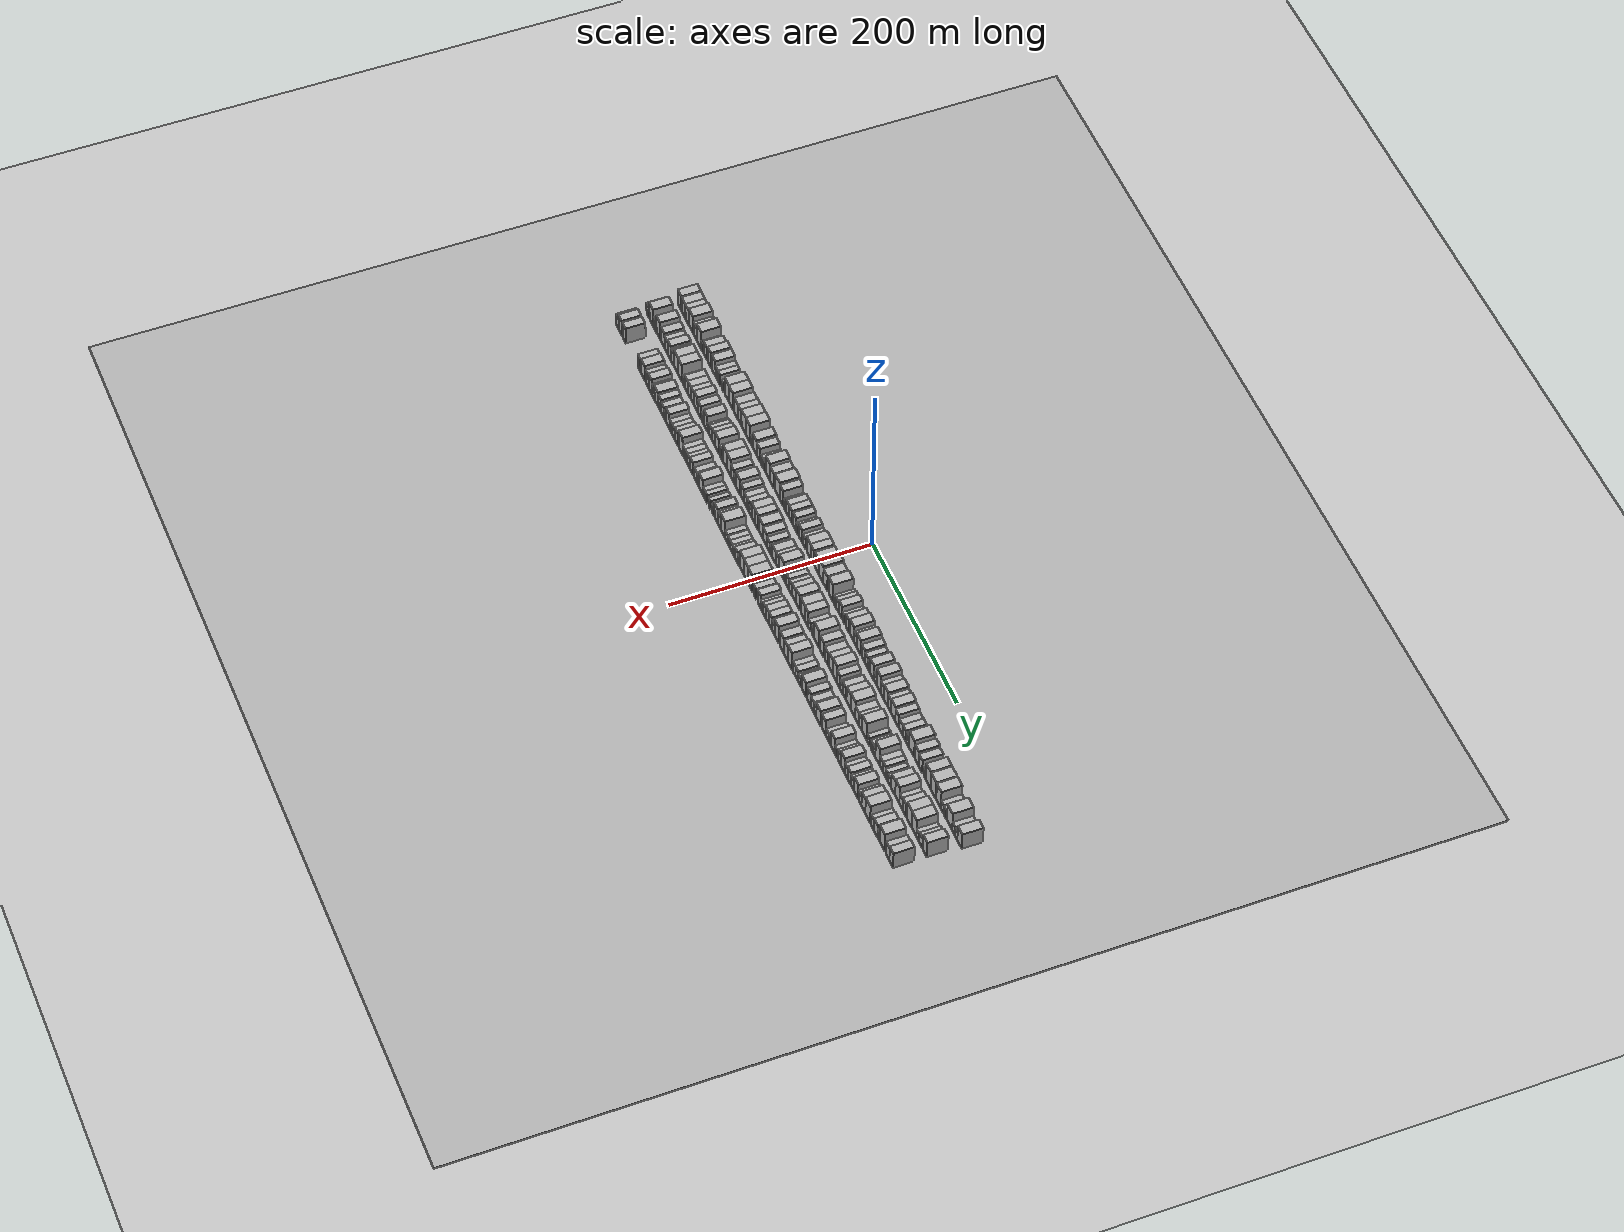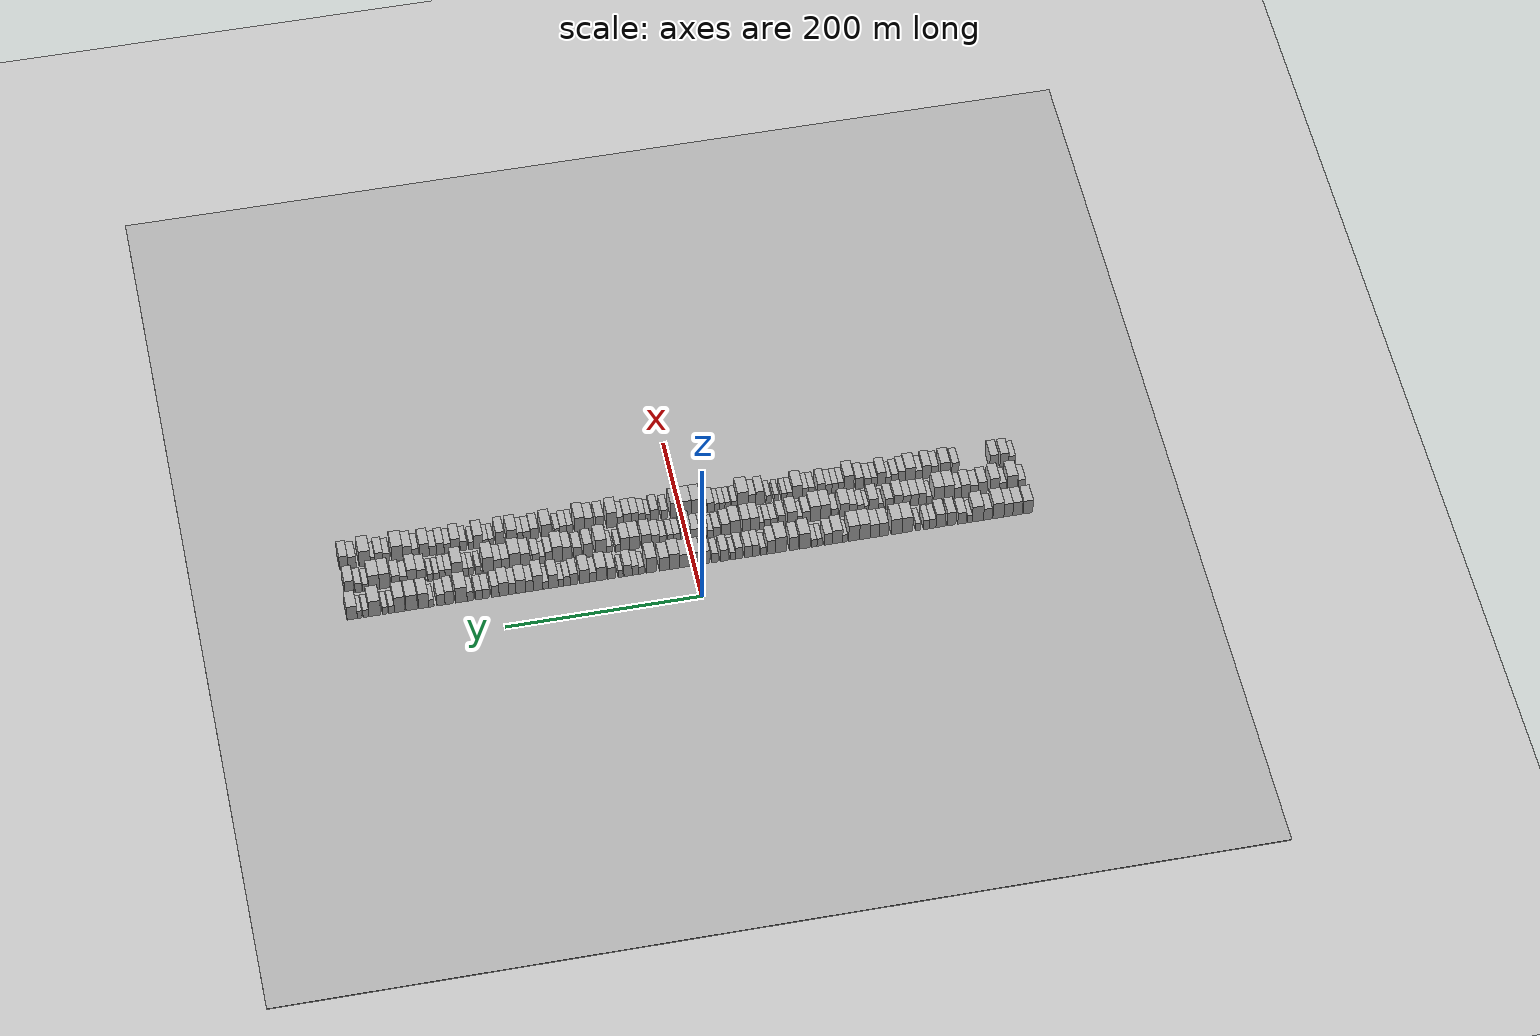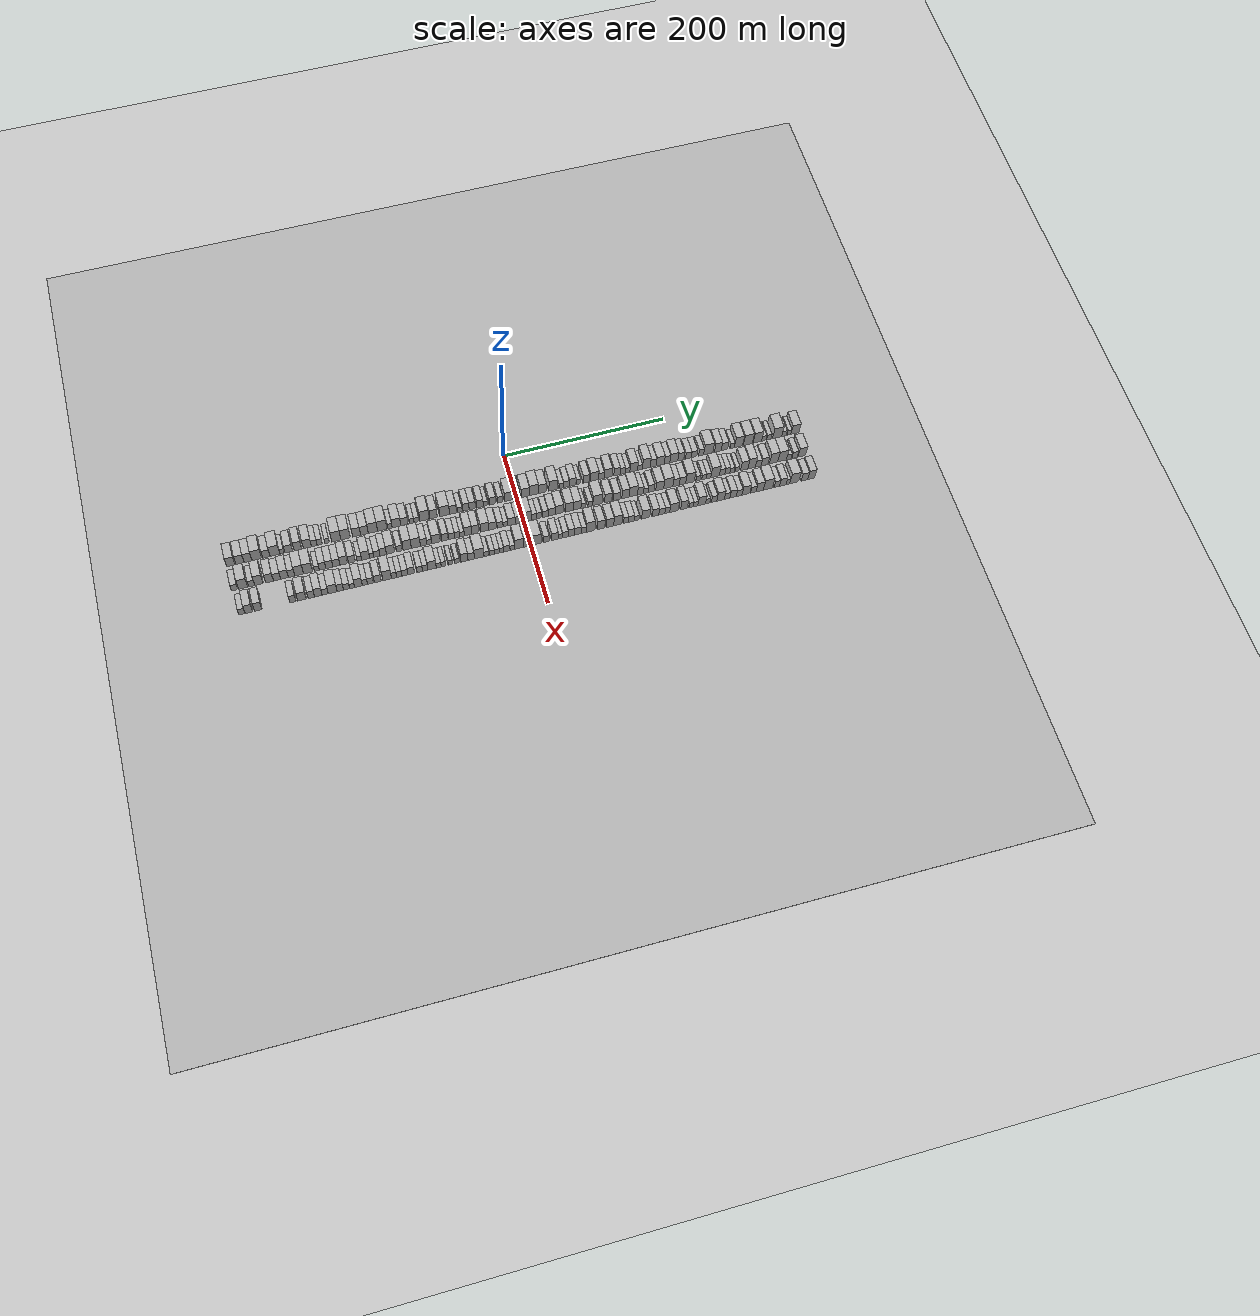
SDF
<?xml version="1.0" encoding="utf-8"?>

<sdf version="1.6">

   <world name="default">

      <gui fullscreen="0">

         <camera name="user_camera">

            <pose>-15 0 4.57585 0 0 0</pose>

            <view_controller>orbit</view_controller>

         </camera>

      </gui>

      <scene>

         <sky>

           <clouds>

             <speed>12</speed>

           </clouds>

         </sky>

         <ambient>0.4 0.4 0.4 1</ambient>

         <background>0.7 0.7 0.7 1</background>

         <shadows>1</shadows>

      </scene>

      <gravity>0 0 -9.8066</gravity>

      <magnetic_field>6e-06 2.3e-05 -4.2e-05</magnetic_field>

      <physics default="0" name="default_physics" type="ode">

         <ode>

            <solver>

               <type>quick</type>

               <iters>10</iters>

               <sor>1.0</sor>

               <use_dynamic_moi_rescaling>0</use_dynamic_moi_rescaling>

            </solver>

            <constraints>

               <cfm>0</cfm>

               <erp>0.2</erp>

               <contact_max_correcting_vel>100</contact_max_correcting_vel>

               <contact_surface_layer>0.001</contact_surface_layer>

            </constraints>

         </ode>

         <max_step_size>0.004</max_step_size>

         <real_time_factor>1</real_time_factor>

         <real_time_update_rate>250</real_time_update_rate>

      </physics>

      <light name="sun" type="directional">

         <cast_shadows>1</cast_shadows>

         <pose>0 0 10 0 0 0</pose>

         <diffuse>0.8 0.8 0.8 1</diffuse>

         <specular>0.2 0.2 0.2 1</specular>

         <attenuation>

            <range>1000</range>

            <constant>0.9</constant>

            <linear>0.01</linear>

            <quadratic>0.001</quadratic>

         </attenuation>

         <direction>-0.5 0.1 -0.9</direction>

      </light>

      <include>

         <name>ground_plane_1</name>

         <uri>model://HANNAS_ground_plane</uri>

         <pose>0 0 0  0 0 0</pose>

      </include>

      <include>

         <name>ground_plane_2</name>

         <uri>model://HANNAS_ground_plane</uri>

         <pose>100 0 0  0 0 0</pose>

      </include>

      <model name="building_1">

         <static>1</static>

         <pose frame="">50.0000 -343.0703 0 0.000000 0.000000 0.000000</pose>

         <link name="link">

            <pose frame="">0 0 10.50 0 0 0</pose>

            <collision name="collision">

               <geometry>

                  <box>

                     <size>20.0000 9.8595 21.0000</size>

                  </box>

               </geometry>

               <max_contacts>10</max_contacts>

               <surface>

                  <contact>

                     <ode/>

                  </contact>

                  <bounce/>

                  <friction>

                     <torsional>

                        <ode/>

                     </torsional>

                     <ode/>

                  </friction>

               </surface>

            </collision>

            <visual name="visual">

               <cast_shadows>0</cast_shadows>

               <geometry>

                  <box>

                     <size>20.0000 9.8595 21.0000</size>

                  </box>

               </geometry>

               <material>

                  <script>

                     <uri>model://HANNAS_wall/materials/scripts</uri>

                     <uri>model://HANNAS_wall/materials/textures</uri>

                     <name>vrc/HANNAS_wall</name>

                  </script>

               </material>

            </visual>

            <self_collide>0</self_collide>

            <enable_wind>0</enable_wind>

            <kinematic>0</kinematic>

         </link>

      </model>

      <model name="building_2">

         <static>1</static>

         <pose frame="">50.0000 -332.2785 0 0.000000 0.000000 0.000000</pose>

         <link name="link">

            <pose frame="">0 0 10.50 0 0 0</pose>

            <collision name="collision">

               <geometry>

                  <box>

                     <size>20.0000 9.7241 21.0000</size>

                  </box>

               </geometry>

               <max_contacts>10</max_contacts>

               <surface>

                  <contact>

                     <ode/>

                  </contact>

                  <bounce/>

                  <friction>

                     <torsional>

                        <ode/>

                     </torsional>

                     <ode/>

                  </friction>

               </surface>

            </collision>

            <visual name="visual">

               <cast_shadows>0</cast_shadows>

               <geometry>

                  <box>

                     <size>20.0000 9.7241 21.0000</size>

                  </box>

               </geometry>

               <material>

                  <script>

                     <uri>model://HANNAS_wall/materials/scripts</uri>

                     <uri>model://HANNAS_wall/materials/textures</uri>

                     <name>vrc/HANNAS_wall</name>

                  </script>

               </material>

            </visual>

            <self_collide>0</self_collide>

            <enable_wind>0</enable_wind>

            <kinematic>0</kinematic>

         </link>

      </model>

      <model name="building_3">

         <static>1</static>

         <pose frame="">50.0000 -322.7978 0 0.000000 0.000000 0.000000</pose>

         <link name="link">

            <pose frame="">0 0 10.50 0 0 0</pose>

            <collision name="collision">

               <geometry>

                  <box>

                     <size>20.0000 9.2373 21.0000</size>

                  </box>

               </geometry>

               <max_contacts>10</max_contacts>

               <surface>

                  <contact>

                     <ode/>

                  </contact>

                  <bounce/>

                  <friction>

                     <torsional>

                        <ode/>

                     </torsional>

                     <ode/>

                  </friction>

               </surface>

            </collision>

            <visual name="visual">

               <cast_shadows>0</cast_shadows>

               <geometry>

                  <box>

                     <size>20.0000 9.2373 21.0000</size>

                  </box>

               </geometry>

               <material>

                  <script>

                     <uri>model://HANNAS_wall/materials/scripts</uri>

                     <uri>model://HANNAS_wall/materials/textures</uri>

                     <name>vrc/HANNAS_wall</name>

                  </script>

               </material>

            </visual>

            <self_collide>0</self_collide>

            <enable_wind>0</enable_wind>

            <kinematic>0</kinematic>

         </link>

      </model>

      <model name="building_4">

         <static>1</static>

         <pose frame="">50.0000 -312.4608 0 0.000000 0.000000 0.000000</pose>

         <link name="link">

            <pose frame="">0 0 12.00 0 0 0</pose>

            <collision name="collision">

               <geometry>

                  <box>

                     <size>20.0000 11.4368 24.0000</size>

                  </box>

               </geometry>

               <max_contacts>10</max_contacts>

               <surface>

                  <contact>

                     <ode/>

                  </contact>

                  <bounce/>

                  <friction>

                     <torsional>

                        <ode/>

                     </torsional>

                     <ode/>

                  </friction>

               </surface>

            </collision>

            <visual name="visual">

               <cast_shadows>0</cast_shadows>

               <geometry>

                  <box>

                     <size>20.0000 11.4368 24.0000</size>

                  </box>

               </geometry>

               <material>

                  <script>

                     <uri>model://HANNAS_wall/materials/scripts</uri>

                     <uri>model://HANNAS_wall/materials/textures</uri>

                     <name>vrc/HANNAS_wall</name>

                  </script>

               </material>

            </visual>

            <self_collide>0</self_collide>

            <enable_wind>0</enable_wind>

            <kinematic>0</kinematic>

         </link>

      </model>

      <model name="building_5">

         <static>1</static>

         <pose frame="">50.0000 -301.3819 0 0.000000 0.000000 0.000000</pose>

         <link name="link">

            <pose frame="">0 0 9.00 0 0 0</pose>

            <collision name="collision">

               <geometry>

                  <box>

                     <size>20.0000 8.7210 18.0000</size>

                  </box>

               </geometry>

               <max_contacts>10</max_contacts>

               <surface>

                  <contact>

                     <ode/>

                  </contact>

                  <bounce/>

                  <friction>

                     <torsional>

                        <ode/>

                     </torsional>

                     <ode/>

                  </friction>

               </surface>

            </collision>

            <visual name="visual">

               <cast_shadows>0</cast_shadows>

               <geometry>

                  <box>

                     <size>20.0000 8.7210 18.0000</size>

                  </box>

               </geometry>

               <material>

                  <script>

                     <uri>model://HANNAS_wall/materials/scripts</uri>

                     <uri>model://HANNAS_wall/materials/textures</uri>

                     <name>vrc/HANNAS_wall</name>

                  </script>

               </material>

            </visual>

            <self_collide>0</self_collide>

            <enable_wind>0</enable_wind>

            <kinematic>0</kinematic>

         </link>

      </model>

      <model name="building_6">

         <static>1</static>

         <pose frame="">50.0000 -291.1596 0 0.000000 0.000000 0.000000</pose>

         <link name="link">

            <pose frame="">0 0 12.00 0 0 0</pose>

            <collision name="collision">

               <geometry>

                  <box>

                     <size>20.0000 11.7235 24.0000</size>

                  </box>

               </geometry>

               <max_contacts>10</max_contacts>

               <surface>

                  <contact>

                     <ode/>

                  </contact>

                  <bounce/>

                  <friction>

                     <torsional>

                        <ode/>

                     </torsional>

                     <ode/>

                  </friction>

               </surface>

            </collision>

            <visual name="visual">

               <cast_shadows>0</cast_shadows>

               <geometry>

                  <box>

                     <size>20.0000 11.7235 24.0000</size>

                  </box>

               </geometry>

               <material>

                  <script>

                     <uri>model://HANNAS_wall/materials/scripts</uri>

                     <uri>model://HANNAS_wall/materials/textures</uri>

                     <name>vrc/HANNAS_wall</name>

                  </script>

               </material>

            </visual>

            <self_collide>0</self_collide>

            <enable_wind>0</enable_wind>

            <kinematic>0</kinematic>

         </link>

      </model>

      <model name="building_7">

         <static>1</static>

         <pose frame="">50.0000 -282.7952 0 0.000000 0.000000 0.000000</pose>

         <link name="link">

            <pose frame="">0 0 6.00 0 0 0</pose>

            <collision name="collision">

               <geometry>

                  <box>

                     <size>20.0000 5.0053 12.0000</size>

                  </box>

               </geometry>

               <max_contacts>10</max_contacts>

               <surface>

                  <contact>

                     <ode/>

                  </contact>

                  <bounce/>

                  <friction>

                     <torsional>

                        <ode/>

                     </torsional>

                     <ode/>

                  </friction>

               </surface>

            </collision>

            <visual name="visual">

               <cast_shadows>0</cast_shadows>

               <geometry>

                  <box>

                     <size>20.0000 5.0053 12.0000</size>

                  </box>

               </geometry>

               <material>

                  <script>

                     <uri>model://HANNAS_wall/materials/scripts</uri>

                     <uri>model://HANNAS_wall/materials/textures</uri>

                     <name>vrc/HANNAS_wall</name>

                  </script>

               </material>

            </visual>

            <self_collide>0</self_collide>

            <enable_wind>0</enable_wind>

            <kinematic>0</kinematic>

         </link>

      </model>

      <model name="building_8">

         <static>1</static>

         <pose frame="">50.0000 -274.8608 0 0.000000 0.000000 0.000000</pose>

         <link name="link">

            <pose frame="">0 0 9.00 0 0 0</pose>

            <collision name="collision">

               <geometry>

                  <box>

                     <size>20.0000 8.8636 18.0000</size>

                  </box>

               </geometry>

               <max_contacts>10</max_contacts>

               <surface>

                  <contact>

                     <ode/>

                  </contact>

                  <bounce/>

                  <friction>

                     <torsional>

                        <ode/>

                     </torsional>

                     <ode/>

                  </friction>

               </surface>

            </collision>

            <visual name="visual">

               <cast_shadows>0</cast_shadows>

               <geometry>

                  <box>

                     <size>20.0000 8.8636 18.0000</size>

                  </box>

               </geometry>

               <material>

                  <script>

                     <uri>model://HANNAS_wall/materials/scripts</uri>

                     <uri>model://HANNAS_wall/materials/textures</uri>

                     <name>vrc/HANNAS_wall</name>

                  </script>

               </material>

            </visual>

            <self_collide>0</self_collide>

            <enable_wind>0</enable_wind>

            <kinematic>0</kinematic>

         </link>

      </model>

      <model name="building_9">

         <static>1</static>

         <pose frame="">50.0000 -263.9722 0 0.000000 0.000000 0.000000</pose>

         <link name="link">

            <pose frame="">0 0 10.50 0 0 0</pose>

            <collision name="collision">

               <geometry>

                  <box>

                     <size>20.0000 8.9136 21.0000</size>

                  </box>

               </geometry>

               <max_contacts>10</max_contacts>

               <surface>

                  <contact>

                     <ode/>

                  </contact>

                  <bounce/>

                  <friction>

                     <torsional>

                        <ode/>

                     </torsional>

                     <ode/>

                  </friction>

               </surface>

            </collision>

            <visual name="visual">

               <cast_shadows>0</cast_shadows>

               <geometry>

                  <box>

                     <size>20.0000 8.9136 21.0000</size>

                  </box>

               </geometry>

               <material>

                  <script>

                     <uri>model://HANNAS_wall/materials/scripts</uri>

                     <uri>model://HANNAS_wall/materials/textures</uri>

                     <name>vrc/HANNAS_wall</name>

                  </script>

               </material>

            </visual>

            <self_collide>0</self_collide>

            <enable_wind>0</enable_wind>

            <kinematic>0</kinematic>

         </link>

      </model>

      <model name="building_10">

         <static>1</static>

         <pose frame="">50.0000 -252.6601 0 0.000000 0.000000 0.000000</pose>

         <link name="link">

            <pose frame="">0 0 10.50 0 0 0</pose>

            <collision name="collision">

               <geometry>

                  <box>

                     <size>20.0000 9.7105 21.0000</size>

                  </box>

               </geometry>

               <max_contacts>10</max_contacts>

               <surface>

                  <contact>

                     <ode/>

                  </contact>

                  <bounce/>

                  <friction>

                     <torsional>

                        <ode/>

                     </torsional>

                     <ode/>

                  </friction>

               </surface>

            </collision>

            <visual name="visual">

               <cast_shadows>0</cast_shadows>

               <geometry>

                  <box>

                     <size>20.0000 9.7105 21.0000</size>

                  </box>

               </geometry>

               <material>

                  <script>

                     <uri>model://HANNAS_wall/materials/scripts</uri>

                     <uri>model://HANNAS_wall/materials/textures</uri>

                     <name>vrc/HANNAS_wall</name>

                  </script>

               </material>

            </visual>

            <self_collide>0</self_collide>

            <enable_wind>0</enable_wind>

            <kinematic>0</kinematic>

         </link>

      </model>

      <model name="building_11">

         <static>1</static>

         <pose frame="">50.0000 -244.5141 0 0.000000 0.000000 0.000000</pose>

         <link name="link">

            <pose frame="">0 0 7.50 0 0 0</pose>

            <collision name="collision">

               <geometry>

                  <box>

                     <size>20.0000 6.5817 15.0000</size>

                  </box>

               </geometry>

               <max_contacts>10</max_contacts>

               <surface>

                  <contact>

                     <ode/>

                  </contact>

                  <bounce/>

                  <friction>

                     <torsional>

                        <ode/>

                     </torsional>

                     <ode/>

                  </friction>

               </surface>

            </collision>

            <visual name="visual">

               <cast_shadows>0</cast_shadows>

               <geometry>

                  <box>

                     <size>20.0000 6.5817 15.0000</size>

                  </box>

               </geometry>

               <material>

                  <script>

                     <uri>model://HANNAS_wall/materials/scripts</uri>

                     <uri>model://HANNAS_wall/materials/textures</uri>

                     <name>vrc/HANNAS_wall</name>

                  </script>

               </material>

            </visual>

            <self_collide>0</self_collide>

            <enable_wind>0</enable_wind>

            <kinematic>0</kinematic>

         </link>

      </model>

      <model name="building_12">

         <static>1</static>

         <pose frame="">50.0000 -238.1243 0 0.000000 0.000000 0.000000</pose>

         <link name="link">

            <pose frame="">0 0 7.50 0 0 0</pose>

            <collision name="collision">

               <geometry>

                  <box>

                     <size>20.0000 6.1979 15.0000</size>

                  </box>

               </geometry>

               <max_contacts>10</max_contacts>

               <surface>

                  <contact>

                     <ode/>

                  </contact>

                  <bounce/>

                  <friction>

                     <torsional>

                        <ode/>

                     </torsional>

                     <ode/>

                  </friction>

               </surface>

            </collision>

            <visual name="visual">

               <cast_shadows>0</cast_shadows>

               <geometry>

                  <box>

                     <size>20.0000 6.1979 15.0000</size>

                  </box>

               </geometry>

               <material>

                  <script>

                     <uri>model://HANNAS_wall/materials/scripts</uri>

                     <uri>model://HANNAS_wall/materials/textures</uri>

                     <name>vrc/HANNAS_wall</name>

                  </script>

               </material>

            </visual>

            <self_collide>0</self_collide>

            <enable_wind>0</enable_wind>

            <kinematic>0</kinematic>

         </link>

      </model>

      <model name="building_13">

         <static>1</static>

         <pose frame="">50.0000 -229.4065 0 0.000000 0.000000 0.000000</pose>

         <link name="link">

            <pose frame="">0 0 6.00 0 0 0</pose>

            <collision name="collision">

               <geometry>

                  <box>

                     <size>20.0000 5.2378 12.0000</size>

                  </box>

               </geometry>

               <max_contacts>10</max_contacts>

               <surface>

                  <contact>

                     <ode/>

                  </contact>

                  <bounce/>

                  <friction>

                     <torsional>

                        <ode/>

                     </torsional>

                     <ode/>

                  </friction>

               </surface>

            </collision>

            <visual name="visual">

               <cast_shadows>0</cast_shadows>

               <geometry>

                  <box>

                     <size>20.0000 5.2378 12.0000</size>

                  </box>

               </geometry>

               <material>

                  <script>

                     <uri>model://HANNAS_wall/materials/scripts</uri>

                     <uri>model://HANNAS_wall/materials/textures</uri>

                     <name>vrc/HANNAS_wall</name>

                  </script>

               </material>

            </visual>

            <self_collide>0</self_collide>

            <enable_wind>0</enable_wind>

            <kinematic>0</kinematic>

         </link>

      </model>

      <model name="building_14">

         <static>1</static>

         <pose frame="">50.0000 -218.2956 0 0.000000 0.000000 0.000000</pose>

         <link name="link">

            <pose frame="">0 0 12.00 0 0 0</pose>

            <collision name="collision">

               <geometry>

                  <box>

                     <size>20.0000 10.9840 24.0000</size>

                  </box>

               </geometry>

               <max_contacts>10</max_contacts>

               <surface>

                  <contact>

                     <ode/>

                  </contact>

                  <bounce/>

                  <friction>

                     <torsional>

                        <ode/>

                     </torsional>

                     <ode/>

                  </friction>

               </surface>

            </collision>

            <visual name="visual">

               <cast_shadows>0</cast_shadows>

               <geometry>

                  <box>

                     <size>20.0000 10.9840 24.0000</size>

                  </box>

               </geometry>

               <material>

                  <script>

                     <uri>model://HANNAS_wall/materials/scripts</uri>

                     <uri>model://HANNAS_wall/materials/textures</uri>

                     <name>vrc/HANNAS_wall</name>

                  </script>

               </material>

            </visual>

            <self_collide>0</self_collide>

            <enable_wind>0</enable_wind>

            <kinematic>0</kinematic>

         </link>

      </model>

      <model name="building_15">

         <static>1</static>

         <pose frame="">50.0000 -207.2777 0 0.000000 0.000000 0.000000</pose>

         <link name="link">

            <pose frame="">0 0 12.00 0 0 0</pose>

            <collision name="collision">

               <geometry>

                  <box>

                     <size>20.0000 11.0517 24.0000</size>

                  </box>

               </geometry>

               <max_contacts>10</max_contacts>

               <surface>

                  <contact>

                     <ode/>

                  </contact>

                  <bounce/>

                  <friction>

                     <torsional>

                        <ode/>

                     </torsional>

                     <ode/>

                  </friction>

               </surface>

            </collision>

            <visual name="visual">

               <cast_shadows>0</cast_shadows>

               <geometry>

                  <box>

                     <size>20.0000 11.0517 24.0000</size>

                  </box>

               </geometry>

               <material>

                  <script>

                     <uri>model://HANNAS_wall/materials/scripts</uri>

                     <uri>model://HANNAS_wall/materials/textures</uri>

                     <name>vrc/HANNAS_wall</name>

                  </script>

               </material>

            </visual>

            <self_collide>0</self_collide>

            <enable_wind>0</enable_wind>

            <kinematic>0</kinematic>

         </link>

      </model>

      <model name="building_16">

         <static>1</static>

         <pose frame="">50.0000 -194.0915 0 0.000000 0.000000 0.000000</pose>

         <link name="link">

            <pose frame="">0 0 10.50 0 0 0</pose>

            <collision name="collision">

               <geometry>

                  <box>

                     <size>20.0000 9.3208 21.0000</size>

                  </box>

               </geometry>

               <max_contacts>10</max_contacts>

               <surface>

                  <contact>

                     <ode/>

                  </contact>

                  <bounce/>

                  <friction>

                     <torsional>

                        <ode/>

                     </torsional>

                     <ode/>

                  </friction>

               </surface>

            </collision>

            <visual name="visual">

               <cast_shadows>0</cast_shadows>

               <geometry>

                  <box>

                     <size>20.0000 9.3208 21.0000</size>

                  </box>

               </geometry>

               <material>

                  <script>

                     <uri>model://HANNAS_wall/materials/scripts</uri>

                     <uri>model://HANNAS_wall/materials/textures</uri>

                     <name>vrc/HANNAS_wall</name>

                  </script>

               </material>

            </visual>

            <self_collide>0</self_collide>

            <enable_wind>0</enable_wind>

            <kinematic>0</kinematic>

         </link>

      </model>

      <model name="building_17">

         <static>1</static>

         <pose frame="">50.0000 -184.8007 0 0.000000 0.000000 0.000000</pose>

         <link name="link">

            <pose frame="">0 0 10.50 0 0 0</pose>

            <collision name="collision">

               <geometry>

                  <box>

                     <size>20.0000 9.2608 21.0000</size>

                  </box>

               </geometry>

               <max_contacts>10</max_contacts>

               <surface>

                  <contact>

                     <ode/>

                  </contact>

                  <bounce/>

                  <friction>

                     <torsional>

                        <ode/>

                     </torsional>

                     <ode/>

                  </friction>

               </surface>

            </collision>

            <visual name="visual">

               <cast_shadows>0</cast_shadows>

               <geometry>

                  <box>

                     <size>20.0000 9.2608 21.0000</size>

                  </box>

               </geometry>

               <material>

                  <script>

                     <uri>model://HANNAS_wall/materials/scripts</uri>

                     <uri>model://HANNAS_wall/materials/textures</uri>

                     <name>vrc/HANNAS_wall</name>

                  </script>

               </material>

            </visual>

            <self_collide>0</self_collide>

            <enable_wind>0</enable_wind>

            <kinematic>0</kinematic>

         </link>

      </model>

      <model name="building_18">

         <static>1</static>

         <pose frame="">50.0000 -174.6020 0 0.000000 0.000000 0.000000</pose>

         <link name="link">

            <pose frame="">0 0 12.00 0 0 0</pose>

            <collision name="collision">

               <geometry>

                  <box>

                     <size>20.0000 11.1366 24.0000</size>

                  </box>

               </geometry>

               <max_contacts>10</max_contacts>

               <surface>

                  <contact>

                     <ode/>

                  </contact>

                  <bounce/>

                  <friction>

                     <torsional>

                        <ode/>

                     </torsional>

                     <ode/>

                  </friction>

               </surface>

            </collision>

            <visual name="visual">

               <cast_shadows>0</cast_shadows>

               <geometry>

                  <box>

                     <size>20.0000 11.1366 24.0000</size>

                  </box>

               </geometry>

               <material>

                  <script>

                     <uri>model://HANNAS_wall/materials/scripts</uri>

                     <uri>model://HANNAS_wall/materials/textures</uri>

                     <name>vrc/HANNAS_wall</name>

                  </script>

               </material>

            </visual>

            <self_collide>0</self_collide>

            <enable_wind>0</enable_wind>

            <kinematic>0</kinematic>

         </link>

      </model>

      <model name="building_19">

         <static>1</static>

         <pose frame="">50.0000 -163.4128 0 0.000000 0.000000 0.000000</pose>

         <link name="link">

            <pose frame="">0 0 12.00 0 0 0</pose>

            <collision name="collision">

               <geometry>

                  <box>

                     <size>20.0000 11.2418 24.0000</size>

                  </box>

               </geometry>

               <max_contacts>10</max_contacts>

               <surface>

                  <contact>

                     <ode/>

                  </contact>

                  <bounce/>

                  <friction>

                     <torsional>

                        <ode/>

                     </torsional>

                     <ode/>

                  </friction>

               </surface>

            </collision>

            <visual name="visual">

               <cast_shadows>0</cast_shadows>

               <geometry>

                  <box>

                     <size>20.0000 11.2418 24.0000</size>

                  </box>

               </geometry>

               <material>

                  <script>

                     <uri>model://HANNAS_wall/materials/scripts</uri>

                     <uri>model://HANNAS_wall/materials/textures</uri>

                     <name>vrc/HANNAS_wall</name>

                  </script>

               </material>

            </visual>

            <self_collide>0</self_collide>

            <enable_wind>0</enable_wind>

            <kinematic>0</kinematic>

         </link>

      </model>

      <model name="building_20">

         <static>1</static>

         <pose frame="">50.0000 -154.2095 0 0.000000 0.000000 0.000000</pose>

         <link name="link">

            <pose frame="">0 0 6.00 0 0 0</pose>

            <collision name="collision">

               <geometry>

                  <box>

                     <size>20.0000 5.1648 12.0000</size>

                  </box>

               </geometry>

               <max_contacts>10</max_contacts>

               <surface>

                  <contact>

                     <ode/>

                  </contact>

                  <bounce/>

                  <friction>

                     <torsional>

                        <ode/>

                     </torsional>

                     <ode/>

                  </friction>

               </surface>

            </collision>

            <visual name="visual">

               <cast_shadows>0</cast_shadows>

               <geometry>

                  <box>

                     <size>20.0000 5.1648 12.0000</size>

                  </box>

               </geometry>

               <material>

                  <script>

                     <uri>model://HANNAS_wall/materials/scripts</uri>

                     <uri>model://HANNAS_wall/materials/textures</uri>

                     <name>vrc/HANNAS_wall</name>

                  </script>

               </material>

            </visual>

            <self_collide>0</self_collide>

            <enable_wind>0</enable_wind>

            <kinematic>0</kinematic>

         </link>

      </model>

      <model name="building_21">

         <static>1</static>

         <pose frame="">50.0000 -146.4476 0 0.000000 0.000000 0.000000</pose>

         <link name="link">

            <pose frame="">0 0 10.50 0 0 0</pose>

            <collision name="collision">

               <geometry>

                  <box>

                     <size>20.0000 10.3590 21.0000</size>

                  </box>

               </geometry>

               <max_contacts>10</max_contacts>

               <surface>

                  <contact>

                     <ode/>

                  </contact>

                  <bounce/>

                  <friction>

                     <torsional>

                        <ode/>

                     </torsional>

                     <ode/>

                  </friction>

               </surface>

            </collision>

            <visual name="visual">

               <cast_shadows>0</cast_shadows>

               <geometry>

                  <box>

                     <size>20.0000 10.3590 21.0000</size>

                  </box>

               </geometry>

               <material>

                  <script>

                     <uri>model://HANNAS_wall/materials/scripts</uri>

                     <uri>model://HANNAS_wall/materials/textures</uri>

                     <name>vrc/HANNAS_wall</name>

                  </script>

               </material>

            </visual>

            <self_collide>0</self_collide>

            <enable_wind>0</enable_wind>

            <kinematic>0</kinematic>

         </link>

      </model>

      <model name="building_22">

         <static>1</static>

         <pose frame="">50.0000 -136.9154 0 0.000000 0.000000 0.000000</pose>

         <link name="link">

            <pose frame="">0 0 9.00 0 0 0</pose>

            <collision name="collision">

               <geometry>

                  <box>

                     <size>20.0000 8.7054 18.0000</size>

                  </box>

               </geometry>

               <max_contacts>10</max_contacts>

               <surface>

                  <contact>

                     <ode/>

                  </contact>

                  <bounce/>

                  <friction>

                     <torsional>

                        <ode/>

                     </torsional>

                     <ode/>

                  </friction>

               </surface>

            </collision>

            <visual name="visual">

               <cast_shadows>0</cast_shadows>

               <geometry>

                  <box>

                     <size>20.0000 8.7054 18.0000</size>

                  </box>

               </geometry>

               <material>

                  <script>

                     <uri>model://HANNAS_wall/materials/scripts</uri>

                     <uri>model://HANNAS_wall/materials/textures</uri>

                     <name>vrc/HANNAS_wall</name>

                  </script>

               </material>

            </visual>

            <self_collide>0</self_collide>

            <enable_wind>0</enable_wind>

            <kinematic>0</kinematic>

         </link>

      </model>

      <model name="building_23">

         <static>1</static>

         <pose frame="">50.0000 -127.8699 0 0.000000 0.000000 0.000000</pose>

         <link name="link">

            <pose frame="">0 0 6.00 0 0 0</pose>

            <collision name="collision">

               <geometry>

                  <box>

                     <size>20.0000 5.3856 12.0000</size>

                  </box>

               </geometry>

               <max_contacts>10</max_contacts>

               <surface>

                  <contact>

                     <ode/>

                  </contact>

                  <bounce/>

                  <friction>

                     <torsional>

                        <ode/>

                     </torsional>

                     <ode/>

                  </friction>

               </surface>

            </collision>

            <visual name="visual">

               <cast_shadows>0</cast_shadows>

               <geometry>

                  <box>

                     <size>20.0000 5.3856 12.0000</size>

                  </box>

               </geometry>

               <material>

                  <script>

                     <uri>model://HANNAS_wall/materials/scripts</uri>

                     <uri>model://HANNAS_wall/materials/textures</uri>

                     <name>vrc/HANNAS_wall</name>

                  </script>

               </material>

            </visual>

            <self_collide>0</self_collide>

            <enable_wind>0</enable_wind>

            <kinematic>0</kinematic>

         </link>

      </model>

      <model name="building_24">

         <static>1</static>

         <pose frame="">50.0000 -122.2185 0 0.000000 0.000000 0.000000</pose>

         <link name="link">

            <pose frame="">0 0 6.00 0 0 0</pose>

            <collision name="collision">

               <geometry>

                  <box>

                     <size>20.0000 5.9172 12.0000</size>

                  </box>

               </geometry>

               <max_contacts>10</max_contacts>

               <surface>

                  <contact>

                     <ode/>

                  </contact>

                  <bounce/>

                  <friction>

                     <torsional>

                        <ode/>

                     </torsional>

                     <ode/>

                  </friction>

               </surface>

            </collision>

            <visual name="visual">

               <cast_shadows>0</cast_shadows>

               <geometry>

                  <box>

                     <size>20.0000 5.9172 12.0000</size>

                  </box>

               </geometry>

               <material>

                  <script>

                     <uri>model://HANNAS_wall/materials/scripts</uri>

                     <uri>model://HANNAS_wall/materials/textures</uri>

                     <name>vrc/HANNAS_wall</name>

                  </script>

               </material>

            </visual>

            <self_collide>0</self_collide>

            <enable_wind>0</enable_wind>

            <kinematic>0</kinematic>

         </link>

      </model>

      <model name="building_25">

         <static>1</static>

         <pose frame="">50.0000 -112.6740 0 0.000000 0.000000 0.000000</pose>

         <link name="link">

            <pose frame="">0 0 12.00 0 0 0</pose>

            <collision name="collision">

               <geometry>

                  <box>

                     <size>20.0000 11.1717 24.0000</size>

                  </box>

               </geometry>

               <max_contacts>10</max_contacts>

               <surface>

                  <contact>

                     <ode/>

                  </contact>

                  <bounce/>

                  <friction>

                     <torsional>

                        <ode/>

                     </torsional>

                     <ode/>

                  </friction>

               </surface>

            </collision>

            <visual name="visual">

               <cast_shadows>0</cast_shadows>

               <geometry>

                  <box>

                     <size>20.0000 11.1717 24.0000</size>

                  </box>

               </geometry>

               <material>

                  <script>

                     <uri>model://HANNAS_wall/materials/scripts</uri>

                     <uri>model://HANNAS_wall/materials/textures</uri>

                     <name>vrc/HANNAS_wall</name>

                  </script>

               </material>

            </visual>

            <self_collide>0</self_collide>

            <enable_wind>0</enable_wind>

            <kinematic>0</kinematic>

         </link>

      </model>

      <model name="building_26">

         <static>1</static>

         <pose frame="">50.0000 -101.6090 0 0.000000 0.000000 0.000000</pose>

         <link name="link">

            <pose frame="">0 0 10.50 0 0 0</pose>

            <collision name="collision">

               <geometry>

                  <box>

                     <size>20.0000 8.9583 21.0000</size>

                  </box>

               </geometry>

               <max_contacts>10</max_contacts>

               <surface>

                  <contact>

                     <ode/>

                  </contact>

                  <bounce/>

                  <friction>

                     <torsional>

                        <ode/>

                     </torsional>

                     <ode/>

                  </friction>

               </surface>

            </collision>

            <visual name="visual">

               <cast_shadows>0</cast_shadows>

               <geometry>

                  <box>

                     <size>20.0000 8.9583 21.0000</size>

                  </box>

               </geometry>

               <material>

                  <script>

                     <uri>model://HANNAS_wall/materials/scripts</uri>

                     <uri>model://HANNAS_wall/materials/textures</uri>

                     <name>vrc/HANNAS_wall</name>

                  </script>

               </material>

            </visual>

            <self_collide>0</self_collide>

            <enable_wind>0</enable_wind>

            <kinematic>0</kinematic>

         </link>

      </model>

      <model name="building_27">

         <static>1</static>

         <pose frame="">50.0000 -88.2075 0 0.000000 0.000000 0.000000</pose>

         <link name="link">

            <pose frame="">0 0 12.00 0 0 0</pose>

            <collision name="collision">

               <geometry>

                  <box>

                     <size>20.0000 11.8447 24.0000</size>

                  </box>

               </geometry>

               <max_contacts>10</max_contacts>

               <surface>

                  <contact>

                     <ode/>

                  </contact>

                  <bounce/>

                  <friction>

                     <torsional>

                        <ode/>

                     </torsional>

                     <ode/>

                  </friction>

               </surface>

            </collision>

            <visual name="visual">

               <cast_shadows>0</cast_shadows>

               <geometry>

                  <box>

                     <size>20.0000 11.8447 24.0000</size>

                  </box>

               </geometry>

               <material>

                  <script>

                     <uri>model://HANNAS_wall/materials/scripts</uri>

                     <uri>model://HANNAS_wall/materials/textures</uri>

                     <name>vrc/HANNAS_wall</name>

                  </script>

               </material>

            </visual>

            <self_collide>0</self_collide>

            <enable_wind>0</enable_wind>

            <kinematic>0</kinematic>

         </link>

      </model>

      <model name="building_28">

         <static>1</static>

         <pose frame="">50.0000 -78.0572 0 0.000000 0.000000 0.000000</pose>

         <link name="link">

            <pose frame="">0 0 10.50 0 0 0</pose>

            <collision name="collision">

               <geometry>

                  <box>

                     <size>20.0000 8.4559 21.0000</size>

                  </box>

               </geometry>

               <max_contacts>10</max_contacts>

               <surface>

                  <contact>

                     <ode/>

                  </contact>

                  <bounce/>

                  <friction>

                     <torsional>

                        <ode/>

                     </torsional>

                     <ode/>

                  </friction>

               </surface>

            </collision>

            <visual name="visual">

               <cast_shadows>0</cast_shadows>

               <geometry>

                  <box>

                     <size>20.0000 8.4559 21.0000</size>

                  </box>

               </geometry>

               <material>

                  <script>

                     <uri>model://HANNAS_wall/materials/scripts</uri>

                     <uri>model://HANNAS_wall/materials/textures</uri>

                     <name>vrc/HANNAS_wall</name>

                  </script>

               </material>

            </visual>

            <self_collide>0</self_collide>

            <enable_wind>0</enable_wind>

            <kinematic>0</kinematic>

         </link>

      </model>

      <model name="building_29">

         <static>1</static>

         <pose frame="">50.0000 -69.8755 0 0.000000 0.000000 0.000000</pose>

         <link name="link">

            <pose frame="">0 0 6.00 0 0 0</pose>

            <collision name="collision">

               <geometry>

                  <box>

                     <size>20.0000 5.9075 12.0000</size>

                  </box>

               </geometry>

               <max_contacts>10</max_contacts>

               <surface>

                  <contact>

                     <ode/>

                  </contact>

                  <bounce/>

                  <friction>

                     <torsional>

                        <ode/>

                     </torsional>

                     <ode/>

                  </friction>

               </surface>

            </collision>

            <visual name="visual">

               <cast_shadows>0</cast_shadows>

               <geometry>

                  <box>

                     <size>20.0000 5.9075 12.0000</size>

                  </box>

               </geometry>

               <material>

                  <script>

                     <uri>model://HANNAS_wall/materials/scripts</uri>

                     <uri>model://HANNAS_wall/materials/textures</uri>

                     <name>vrc/HANNAS_wall</name>

                  </script>

               </material>

            </visual>

            <self_collide>0</self_collide>

            <enable_wind>0</enable_wind>

            <kinematic>0</kinematic>

         </link>

      </model>

      <model name="building_30">

         <static>1</static>

         <pose frame="">50.0000 -62.2348 0 0.000000 0.000000 0.000000</pose>

         <link name="link">

            <pose frame="">0 0 9.00 0 0 0</pose>

            <collision name="collision">

               <geometry>

                  <box>

                     <size>20.0000 7.3739 18.0000</size>

                  </box>

               </geometry>

               <max_contacts>10</max_contacts>

               <surface>

                  <contact>

                     <ode/>

                  </contact>

                  <bounce/>

                  <friction>

                     <torsional>

                        <ode/>

                     </torsional>

                     <ode/>

                  </friction>

               </surface>

            </collision>

            <visual name="visual">

               <cast_shadows>0</cast_shadows>

               <geometry>

                  <box>

                     <size>20.0000 7.3739 18.0000</size>

                  </box>

               </geometry>

               <material>

                  <script>

                     <uri>model://HANNAS_wall/materials/scripts</uri>

                     <uri>model://HANNAS_wall/materials/textures</uri>

                     <name>vrc/HANNAS_wall</name>

                  </script>

               </material>

            </visual>

            <self_collide>0</self_collide>

            <enable_wind>0</enable_wind>

            <kinematic>0</kinematic>

         </link>

      </model>

      <model name="building_31">

         <static>1</static>

         <pose frame="">50.0000 -54.7621 0 0.000000 0.000000 0.000000</pose>

         <link name="link">

            <pose frame="">0 0 9.00 0 0 0</pose>

            <collision name="collision">

               <geometry>

                  <box>

                     <size>20.0000 7.5714 18.0000</size>

                  </box>

               </geometry>

               <max_contacts>10</max_contacts>

               <surface>

                  <contact>

                     <ode/>

                  </contact>

                  <bounce/>

                  <friction>

                     <torsional>

                        <ode/>

                     </torsional>

                     <ode/>

                  </friction>

               </surface>

            </collision>

            <visual name="visual">

               <cast_shadows>0</cast_shadows>

               <geometry>

                  <box>

                     <size>20.0000 7.5714 18.0000</size>

                  </box>

               </geometry>

               <material>

                  <script>

                     <uri>model://HANNAS_wall/materials/scripts</uri>

                     <uri>model://HANNAS_wall/materials/textures</uri>

                     <name>vrc/HANNAS_wall</name>

                  </script>

               </material>

            </visual>

            <self_collide>0</self_collide>

            <enable_wind>0</enable_wind>

            <kinematic>0</kinematic>

         </link>

      </model>

      <model name="building_32">

         <static>1</static>

         <pose frame="">50.0000 -45.1714 0 0.000000 0.000000 0.000000</pose>

         <link name="link">

            <pose frame="">0 0 9.00 0 0 0</pose>

            <collision name="collision">

               <geometry>

                  <box>

                     <size>20.0000 7.6100 18.0000</size>

                  </box>

               </geometry>

               <max_contacts>10</max_contacts>

               <surface>

                  <contact>

                     <ode/>

                  </contact>

                  <bounce/>

                  <friction>

                     <torsional>

                        <ode/>

                     </torsional>

                     <ode/>

                  </friction>

               </surface>

            </collision>

            <visual name="visual">

               <cast_shadows>0</cast_shadows>

               <geometry>

                  <box>

                     <size>20.0000 7.6100 18.0000</size>

                  </box>

               </geometry>

               <material>

                  <script>

                     <uri>model://HANNAS_wall/materials/scripts</uri>

                     <uri>model://HANNAS_wall/materials/textures</uri>

                     <name>vrc/HANNAS_wall</name>

                  </script>

               </material>

            </visual>

            <self_collide>0</self_collide>

            <enable_wind>0</enable_wind>

            <kinematic>0</kinematic>

         </link>

      </model>

      <model name="building_33">

         <static>1</static>

         <pose frame="">50.0000 -38.6933 0 0.000000 0.000000 0.000000</pose>

         <link name="link">

            <pose frame="">0 0 6.00 0 0 0</pose>

            <collision name="collision">

               <geometry>

                  <box>

                     <size>20.0000 5.3463 12.0000</size>

                  </box>

               </geometry>

               <max_contacts>10</max_contacts>

               <surface>

                  <contact>

                     <ode/>

                  </contact>

                  <bounce/>

                  <friction>

                     <torsional>

                        <ode/>

                     </torsional>

                     <ode/>

                  </friction>

               </surface>

            </collision>

            <visual name="visual">

               <cast_shadows>0</cast_shadows>

               <geometry>

                  <box>

                     <size>20.0000 5.3463 12.0000</size>

                  </box>

               </geometry>

               <material>

                  <script>

                     <uri>model://HANNAS_wall/materials/scripts</uri>

                     <uri>model://HANNAS_wall/materials/textures</uri>

                     <name>vrc/HANNAS_wall</name>

                  </script>

               </material>

            </visual>

            <self_collide>0</self_collide>

            <enable_wind>0</enable_wind>

            <kinematic>0</kinematic>

         </link>

      </model>

      <model name="building_34">

         <static>1</static>

         <pose frame="">50.0000 -30.0043 0 0.000000 0.000000 0.000000</pose>

         <link name="link">

            <pose frame="">0 0 9.00 0 0 0</pose>

            <collision name="collision">

               <geometry>

                  <box>

                     <size>20.0000 8.0316 18.0000</size>

                  </box>

               </geometry>

               <max_contacts>10</max_contacts>

               <surface>

                  <contact>

                     <ode/>

                  </contact>

                  <bounce/>

                  <friction>

                     <torsional>

                        <ode/>

                     </torsional>

                     <ode/>

                  </friction>

               </surface>

            </collision>

            <visual name="visual">

               <cast_shadows>0</cast_shadows>

               <geometry>

                  <box>

                     <size>20.0000 8.0316 18.0000</size>

                  </box>

               </geometry>

               <material>

                  <script>

                     <uri>model://HANNAS_wall/materials/scripts</uri>

                     <uri>model://HANNAS_wall/materials/textures</uri>

                     <name>vrc/HANNAS_wall</name>

                  </script>

               </material>

            </visual>

            <self_collide>0</self_collide>

            <enable_wind>0</enable_wind>

            <kinematic>0</kinematic>

         </link>

      </model>

      <model name="building_35">

         <static>1</static>

         <pose frame="">50.0000 -20.7029 0 0.000000 0.000000 0.000000</pose>

         <link name="link">

            <pose frame="">0 0 7.50 0 0 0</pose>

            <collision name="collision">

               <geometry>

                  <box>

                     <size>20.0000 6.5713 15.0000</size>

                  </box>

               </geometry>

               <max_contacts>10</max_contacts>

               <surface>

                  <contact>

                     <ode/>

                  </contact>

                  <bounce/>

                  <friction>

                     <torsional>

                        <ode/>

                     </torsional>

                     <ode/>

                  </friction>

               </surface>

            </collision>

            <visual name="visual">

               <cast_shadows>0</cast_shadows>

               <geometry>

                  <box>

                     <size>20.0000 6.5713 15.0000</size>

                  </box>

               </geometry>

               <material>

                  <script>

                     <uri>model://HANNAS_wall/materials/scripts</uri>

                     <uri>model://HANNAS_wall/materials/textures</uri>

                     <name>vrc/HANNAS_wall</name>

                  </script>

               </material>

            </visual>

            <self_collide>0</self_collide>

            <enable_wind>0</enable_wind>

            <kinematic>0</kinematic>

         </link>

      </model>

      <model name="building_36">

         <static>1</static>

         <pose frame="">50.0000 -10.4698 0 0.000000 0.000000 0.000000</pose>

         <link name="link">

            <pose frame="">0 0 10.50 0 0 0</pose>

            <collision name="collision">

               <geometry>

                  <box>

                     <size>20.0000 9.8949 21.0000</size>

                  </box>

               </geometry>

               <max_contacts>10</max_contacts>

               <surface>

                  <contact>

                     <ode/>

                  </contact>

                  <bounce/>

                  <friction>

                     <torsional>

                        <ode/>

                     </torsional>

                     <ode/>

                  </friction>

               </surface>

            </collision>

            <visual name="visual">

               <cast_shadows>0</cast_shadows>

               <geometry>

                  <box>

                     <size>20.0000 9.8949 21.0000</size>

                  </box>

               </geometry>

               <material>

                  <script>

                     <uri>model://HANNAS_wall/materials/scripts</uri>

                     <uri>model://HANNAS_wall/materials/textures</uri>

                     <name>vrc/HANNAS_wall</name>

                  </script>

               </material>

            </visual>

            <self_collide>0</self_collide>

            <enable_wind>0</enable_wind>

            <kinematic>0</kinematic>

         </link>

      </model>

      <model name="building_37">

         <static>1</static>

         <pose frame="">50.0000 -1.2832 0 0.000000 0.000000 0.000000</pose>

         <link name="link">

            <pose frame="">0 0 10.50 0 0 0</pose>

            <collision name="collision">

               <geometry>

                  <box>

                     <size>20.0000 8.4783 21.0000</size>

                  </box>

               </geometry>

               <max_contacts>10</max_contacts>

               <surface>

                  <contact>

                     <ode/>

                  </contact>

                  <bounce/>

                  <friction>

                     <torsional>

                        <ode/>

                     </torsional>

                     <ode/>

                  </friction>

               </surface>

            </collision>

            <visual name="visual">

               <cast_shadows>0</cast_shadows>

               <geometry>

                  <box>

                     <size>20.0000 8.4783 21.0000</size>

                  </box>

               </geometry>

               <material>

                  <script>

                     <uri>model://HANNAS_wall/materials/scripts</uri>

                     <uri>model://HANNAS_wall/materials/textures</uri>

                     <name>vrc/HANNAS_wall</name>

                  </script>

               </material>

            </visual>

            <self_collide>0</self_collide>

            <enable_wind>0</enable_wind>

            <kinematic>0</kinematic>

         </link>

      </model>

      <model name="building_38">

         <static>1</static>

         <pose frame="">50.0000 10.1808 0 0.000000 0.000000 0.000000</pose>

         <link name="link">

            <pose frame="">0 0 10.50 0 0 0</pose>

            <collision name="collision">

               <geometry>

                  <box>

                     <size>20.0000 10.4495 21.0000</size>

                  </box>

               </geometry>

               <max_contacts>10</max_contacts>

               <surface>

                  <contact>

                     <ode/>

                  </contact>

                  <bounce/>

                  <friction>

                     <torsional>

                        <ode/>

                     </torsional>

                     <ode/>

                  </friction>

               </surface>

            </collision>

            <visual name="visual">

               <cast_shadows>0</cast_shadows>

               <geometry>

                  <box>

                     <size>20.0000 10.4495 21.0000</size>

                  </box>

               </geometry>

               <material>

                  <script>

                     <uri>model://HANNAS_wall/materials/scripts</uri>

                     <uri>model://HANNAS_wall/materials/textures</uri>

                     <name>vrc/HANNAS_wall</name>

                  </script>

               </material>

            </visual>

            <self_collide>0</self_collide>

            <enable_wind>0</enable_wind>

            <kinematic>0</kinematic>

         </link>

      </model>

      <model name="building_39">

         <static>1</static>

         <pose frame="">50.0000 20.8284 0 0.000000 0.000000 0.000000</pose>

         <link name="link">

            <pose frame="">0 0 12.00 0 0 0</pose>

            <collision name="collision">

               <geometry>

                  <box>

                     <size>20.0000 10.8458 24.0000</size>

                  </box>

               </geometry>

               <max_contacts>10</max_contacts>

               <surface>

                  <contact>

                     <ode/>

                  </contact>

                  <bounce/>

                  <friction>

                     <torsional>

                        <ode/>

                     </torsional>

                     <ode/>

                  </friction>

               </surface>

            </collision>

            <visual name="visual">

               <cast_shadows>0</cast_shadows>

               <geometry>

                  <box>

                     <size>20.0000 10.8458 24.0000</size>

                  </box>

               </geometry>

               <material>

                  <script>

                     <uri>model://HANNAS_wall/materials/scripts</uri>

                     <uri>model://HANNAS_wall/materials/textures</uri>

                     <name>vrc/HANNAS_wall</name>

                  </script>

               </material>

            </visual>

            <self_collide>0</self_collide>

            <enable_wind>0</enable_wind>

            <kinematic>0</kinematic>

         </link>

      </model>

      <model name="building_40">

         <static>1</static>

         <pose frame="">50.0000 31.1546 0 0.000000 0.000000 0.000000</pose>

         <link name="link">

            <pose frame="">0 0 10.50 0 0 0</pose>

            <collision name="collision">

               <geometry>

                  <box>

                     <size>20.0000 9.8067 21.0000</size>

                  </box>

               </geometry>

               <max_contacts>10</max_contacts>

               <surface>

                  <contact>

                     <ode/>

                  </contact>

                  <bounce/>

                  <friction>

                     <torsional>

                        <ode/>

                     </torsional>

                     <ode/>

                  </friction>

               </surface>

            </collision>

            <visual name="visual">

               <cast_shadows>0</cast_shadows>

               <geometry>

                  <box>

                     <size>20.0000 9.8067 21.0000</size>

                  </box>

               </geometry>

               <material>

                  <script>

                     <uri>model://HANNAS_wall/materials/scripts</uri>

                     <uri>model://HANNAS_wall/materials/textures</uri>

                     <name>vrc/HANNAS_wall</name>

                  </script>

               </material>

            </visual>

            <self_collide>0</self_collide>

            <enable_wind>0</enable_wind>

            <kinematic>0</kinematic>

         </link>

      </model>

      <model name="building_41">

         <static>1</static>

         <pose frame="">50.0000 44.3831 0 0.000000 0.000000 0.000000</pose>

         <link name="link">

            <pose frame="">0 0 12.00 0 0 0</pose>

            <collision name="collision">

               <geometry>

                  <box>

                     <size>20.0000 10.6502 24.0000</size>

                  </box>

               </geometry>

               <max_contacts>10</max_contacts>

               <surface>

                  <contact>

                     <ode/>

                  </contact>

                  <bounce/>

                  <friction>

                     <torsional>

                        <ode/>

                     </torsional>

                     <ode/>

                  </friction>

               </surface>

            </collision>

            <visual name="visual">

               <cast_shadows>0</cast_shadows>

               <geometry>

                  <box>

                     <size>20.0000 10.6502 24.0000</size>

                  </box>

               </geometry>

               <material>

                  <script>

                     <uri>model://HANNAS_wall/materials/scripts</uri>

                     <uri>model://HANNAS_wall/materials/textures</uri>

                     <name>vrc/HANNAS_wall</name>

                  </script>

               </material>

            </visual>

            <self_collide>0</self_collide>

            <enable_wind>0</enable_wind>

            <kinematic>0</kinematic>

         </link>

      </model>

      <model name="building_42">

         <static>1</static>

         <pose frame="">50.0000 54.4648 0 0.000000 0.000000 0.000000</pose>

         <link name="link">

            <pose frame="">0 0 6.00 0 0 0</pose>

            <collision name="collision">

               <geometry>

                  <box>

                     <size>20.0000 5.5132 12.0000</size>

                  </box>

               </geometry>

               <max_contacts>10</max_contacts>

               <surface>

                  <contact>

                     <ode/>

                  </contact>

                  <bounce/>

                  <friction>

                     <torsional>

                        <ode/>

                     </torsional>

                     <ode/>

                  </friction>

               </surface>

            </collision>

            <visual name="visual">

               <cast_shadows>0</cast_shadows>

               <geometry>

                  <box>

                     <size>20.0000 5.5132 12.0000</size>

                  </box>

               </geometry>

               <material>

                  <script>

                     <uri>model://HANNAS_wall/materials/scripts</uri>

                     <uri>model://HANNAS_wall/materials/textures</uri>

                     <name>vrc/HANNAS_wall</name>

                  </script>

               </material>

            </visual>

            <self_collide>0</self_collide>

            <enable_wind>0</enable_wind>

            <kinematic>0</kinematic>

         </link>

      </model>

      <model name="building_43">

         <static>1</static>

         <pose frame="">50.0000 60.6895 0 0.000000 0.000000 0.000000</pose>

         <link name="link">

            <pose frame="">0 0 7.50 0 0 0</pose>

            <collision name="collision">

               <geometry>

                  <box>

                     <size>20.0000 6.9362 15.0000</size>

                  </box>

               </geometry>

               <max_contacts>10</max_contacts>

               <surface>

                  <contact>

                     <ode/>

                  </contact>

                  <bounce/>

                  <friction>

                     <torsional>

                        <ode/>

                     </torsional>

                     <ode/>

                  </friction>

               </surface>

            </collision>

            <visual name="visual">

               <cast_shadows>0</cast_shadows>

               <geometry>

                  <box>

                     <size>20.0000 6.9362 15.0000</size>

                  </box>

               </geometry>

               <material>

                  <script>

                     <uri>model://HANNAS_wall/materials/scripts</uri>

                     <uri>model://HANNAS_wall/materials/textures</uri>

                     <name>vrc/HANNAS_wall</name>

                  </script>

               </material>

            </visual>

            <self_collide>0</self_collide>

            <enable_wind>0</enable_wind>

            <kinematic>0</kinematic>

         </link>

      </model>

      <model name="building_44">

         <static>1</static>

         <pose frame="">50.0000 68.2651 0 0.000000 0.000000 0.000000</pose>

         <link name="link">

            <pose frame="">0 0 9.00 0 0 0</pose>

            <collision name="collision">

               <geometry>

                  <box>

                     <size>20.0000 8.2149 18.0000</size>

                  </box>

               </geometry>

               <max_contacts>10</max_contacts>

               <surface>

                  <contact>

                     <ode/>

                  </contact>

                  <bounce/>

                  <friction>

                     <torsional>

                        <ode/>

                     </torsional>

                     <ode/>

                  </friction>

               </surface>

            </collision>

            <visual name="visual">

               <cast_shadows>0</cast_shadows>

               <geometry>

                  <box>

                     <size>20.0000 8.2149 18.0000</size>

                  </box>

               </geometry>

               <material>

                  <script>

                     <uri>model://HANNAS_wall/materials/scripts</uri>

                     <uri>model://HANNAS_wall/materials/textures</uri>

                     <name>vrc/HANNAS_wall</name>

                  </script>

               </material>

            </visual>

            <self_collide>0</self_collide>

            <enable_wind>0</enable_wind>

            <kinematic>0</kinematic>

         </link>

      </model>

      <model name="building_45">

         <static>1</static>

         <pose frame="">50.0000 75.8237 0 0.000000 0.000000 0.000000</pose>

         <link name="link">

            <pose frame="">0 0 6.00 0 0 0</pose>

            <collision name="collision">

               <geometry>

                  <box>

                     <size>20.0000 4.9023 12.0000</size>

                  </box>

               </geometry>

               <max_contacts>10</max_contacts>

               <surface>

                  <contact>

                     <ode/>

                  </contact>

                  <bounce/>

                  <friction>

                     <torsional>

                        <ode/>

                     </torsional>

                     <ode/>

                  </friction>

               </surface>

            </collision>

            <visual name="visual">

               <cast_shadows>0</cast_shadows>

               <geometry>

                  <box>

                     <size>20.0000 4.9023 12.0000</size>

                  </box>

               </geometry>

               <material>

                  <script>

                     <uri>model://HANNAS_wall/materials/scripts</uri>

                     <uri>model://HANNAS_wall/materials/textures</uri>

                     <name>vrc/HANNAS_wall</name>

                  </script>

               </material>

            </visual>

            <self_collide>0</self_collide>

            <enable_wind>0</enable_wind>

            <kinematic>0</kinematic>

         </link>

      </model>

      <model name="building_46">

         <static>1</static>

         <pose frame="">50.0000 85.1791 0 0.000000 0.000000 0.000000</pose>

         <link name="link">

            <pose frame="">0 0 9.00 0 0 0</pose>

            <collision name="collision">

               <geometry>

                  <box>

                     <size>20.0000 7.8086 18.0000</size>

                  </box>

               </geometry>

               <max_contacts>10</max_contacts>

               <surface>

                  <contact>

                     <ode/>

                  </contact>

                  <bounce/>

                  <friction>

                     <torsional>

                        <ode/>

                     </torsional>

                     <ode/>

                  </friction>

               </surface>

            </collision>

            <visual name="visual">

               <cast_shadows>0</cast_shadows>

               <geometry>

                  <box>

                     <size>20.0000 7.8086 18.0000</size>

                  </box>

               </geometry>

               <material>

                  <script>

                     <uri>model://HANNAS_wall/materials/scripts</uri>

                     <uri>model://HANNAS_wall/materials/textures</uri>

                     <name>vrc/HANNAS_wall</name>

                  </script>

               </material>

            </visual>

            <self_collide>0</self_collide>

            <enable_wind>0</enable_wind>

            <kinematic>0</kinematic>

         </link>

      </model>

      <model name="building_47">

         <static>1</static>

         <pose frame="">50.0000 95.2518 0 0.000000 0.000000 0.000000</pose>

         <link name="link">

            <pose frame="">0 0 10.50 0 0 0</pose>

            <collision name="collision">

               <geometry>

                  <box>

                     <size>20.0000 10.3369 21.0000</size>

                  </box>

               </geometry>

               <max_contacts>10</max_contacts>

               <surface>

                  <contact>

                     <ode/>

                  </contact>

                  <bounce/>

                  <friction>

                     <torsional>

                        <ode/>

                     </torsional>

                     <ode/>

                  </friction>

               </surface>

            </collision>

            <visual name="visual">

               <cast_shadows>0</cast_shadows>

               <geometry>

                  <box>

                     <size>20.0000 10.3369 21.0000</size>

                  </box>

               </geometry>

               <material>

                  <script>

                     <uri>model://HANNAS_wall/materials/scripts</uri>

                     <uri>model://HANNAS_wall/materials/textures</uri>

                     <name>vrc/HANNAS_wall</name>

                  </script>

               </material>

            </visual>

            <self_collide>0</self_collide>

            <enable_wind>0</enable_wind>

            <kinematic>0</kinematic>

         </link>

      </model>

      <model name="building_48">

         <static>1</static>

         <pose frame="">50.0000 103.9661 0 0.000000 0.000000 0.000000</pose>

         <link name="link">

            <pose frame="">0 0 7.50 0 0 0</pose>

            <collision name="collision">

               <geometry>

                  <box>

                     <size>20.0000 7.0916 15.0000</size>

                  </box>

               </geometry>

               <max_contacts>10</max_contacts>

               <surface>

                  <contact>

                     <ode/>

                  </contact>

                  <bounce/>

                  <friction>

                     <torsional>

                        <ode/>

                     </torsional>

                     <ode/>

                  </friction>

               </surface>

            </collision>

            <visual name="visual">

               <cast_shadows>0</cast_shadows>

               <geometry>

                  <box>

                     <size>20.0000 7.0916 15.0000</size>

                  </box>

               </geometry>

               <material>

                  <script>

                     <uri>model://HANNAS_wall/materials/scripts</uri>

                     <uri>model://HANNAS_wall/materials/textures</uri>

                     <name>vrc/HANNAS_wall</name>

                  </script>

               </material>

            </visual>

            <self_collide>0</self_collide>

            <enable_wind>0</enable_wind>

            <kinematic>0</kinematic>

         </link>

      </model>

      <model name="building_49">

         <static>1</static>

         <pose frame="">50.0000 112.4369 0 0.000000 0.000000 0.000000</pose>

         <link name="link">

            <pose frame="">0 0 10.50 0 0 0</pose>

            <collision name="collision">

               <geometry>

                  <box>

                     <size>20.0000 9.8500 21.0000</size>

                  </box>

               </geometry>

               <max_contacts>10</max_contacts>

               <surface>

                  <contact>

                     <ode/>

                  </contact>

                  <bounce/>

                  <friction>

                     <torsional>

                        <ode/>

                     </torsional>

                     <ode/>

                  </friction>

               </surface>

            </collision>

            <visual name="visual">

               <cast_shadows>0</cast_shadows>

               <geometry>

                  <box>

                     <size>20.0000 9.8500 21.0000</size>

                  </box>

               </geometry>

               <material>

                  <script>

                     <uri>model://HANNAS_wall/materials/scripts</uri>

                     <uri>model://HANNAS_wall/materials/textures</uri>

                     <name>vrc/HANNAS_wall</name>

                  </script>

               </material>

            </visual>

            <self_collide>0</self_collide>

            <enable_wind>0</enable_wind>

            <kinematic>0</kinematic>

         </link>

      </model>

      <model name="building_50">

         <static>1</static>

         <pose frame="">50.0000 123.2731 0 0.000000 0.000000 0.000000</pose>

         <link name="link">

            <pose frame="">0 0 9.00 0 0 0</pose>

            <collision name="collision">

               <geometry>

                  <box>

                     <size>20.0000 7.8224 18.0000</size>

                  </box>

               </geometry>

               <max_contacts>10</max_contacts>

               <surface>

                  <contact>

                     <ode/>

                  </contact>

                  <bounce/>

                  <friction>

                     <torsional>

                        <ode/>

                     </torsional>

                     <ode/>

                  </friction>

               </surface>

            </collision>

            <visual name="visual">

               <cast_shadows>0</cast_shadows>

               <geometry>

                  <box>

                     <size>20.0000 7.8224 18.0000</size>

                  </box>

               </geometry>

               <material>

                  <script>

                     <uri>model://HANNAS_wall/materials/scripts</uri>

                     <uri>model://HANNAS_wall/materials/textures</uri>

                     <name>vrc/HANNAS_wall</name>

                  </script>

               </material>

            </visual>

            <self_collide>0</self_collide>

            <enable_wind>0</enable_wind>

            <kinematic>0</kinematic>

         </link>

      </model>

      <model name="building_51">

         <static>1</static>

         <pose frame="">50.0000 130.3478 0 0.000000 0.000000 0.000000</pose>

         <link name="link">

            <pose frame="">0 0 7.50 0 0 0</pose>

            <collision name="collision">

               <geometry>

                  <box>

                     <size>20.0000 6.3270 15.0000</size>

                  </box>

               </geometry>

               <max_contacts>10</max_contacts>

               <surface>

                  <contact>

                     <ode/>

                  </contact>

                  <bounce/>

                  <friction>

                     <torsional>

                        <ode/>

                     </torsional>

                     <ode/>

                  </friction>

               </surface>

            </collision>

            <visual name="visual">

               <cast_shadows>0</cast_shadows>

               <geometry>

                  <box>

                     <size>20.0000 6.3270 15.0000</size>

                  </box>

               </geometry>

               <material>

                  <script>

                     <uri>model://HANNAS_wall/materials/scripts</uri>

                     <uri>model://HANNAS_wall/materials/textures</uri>

                     <name>vrc/HANNAS_wall</name>

                  </script>

               </material>

            </visual>

            <self_collide>0</self_collide>

            <enable_wind>0</enable_wind>

            <kinematic>0</kinematic>

         </link>

      </model>

      <model name="building_52">

         <static>1</static>

         <pose frame="">50.0000 136.4501 0 0.000000 0.000000 0.000000</pose>

         <link name="link">

            <pose frame="">0 0 6.00 0 0 0</pose>

            <collision name="collision">

               <geometry>

                  <box>

                     <size>20.0000 5.8776 12.0000</size>

                  </box>

               </geometry>

               <max_contacts>10</max_contacts>

               <surface>

                  <contact>

                     <ode/>

                  </contact>

                  <bounce/>

                  <friction>

                     <torsional>

                        <ode/>

                     </torsional>

                     <ode/>

                  </friction>

               </surface>

            </collision>

            <visual name="visual">

               <cast_shadows>0</cast_shadows>

               <geometry>

                  <box>

                     <size>20.0000 5.8776 12.0000</size>

                  </box>

               </geometry>

               <material>

                  <script>

                     <uri>model://HANNAS_wall/materials/scripts</uri>

                     <uri>model://HANNAS_wall/materials/textures</uri>

                     <name>vrc/HANNAS_wall</name>

                  </script>

               </material>

            </visual>

            <self_collide>0</self_collide>

            <enable_wind>0</enable_wind>

            <kinematic>0</kinematic>

         </link>

      </model>

      <model name="building_53">

         <static>1</static>

         <pose frame="">50.0000 144.1635 0 0.000000 0.000000 0.000000</pose>

         <link name="link">

            <pose frame="">0 0 10.50 0 0 0</pose>

            <collision name="collision">

               <geometry>

                  <box>

                     <size>20.0000 9.5491 21.0000</size>

                  </box>

               </geometry>

               <max_contacts>10</max_contacts>

               <surface>

                  <contact>

                     <ode/>

                  </contact>

                  <bounce/>

                  <friction>

                     <torsional>

                        <ode/>

                     </torsional>

                     <ode/>

                  </friction>

               </surface>

            </collision>

            <visual name="visual">

               <cast_shadows>0</cast_shadows>

               <geometry>

                  <box>

                     <size>20.0000 9.5491 21.0000</size>

                  </box>

               </geometry>

               <material>

                  <script>

                     <uri>model://HANNAS_wall/materials/scripts</uri>

                     <uri>model://HANNAS_wall/materials/textures</uri>

                     <name>vrc/HANNAS_wall</name>

                  </script>

               </material>

            </visual>

            <self_collide>0</self_collide>

            <enable_wind>0</enable_wind>

            <kinematic>0</kinematic>

         </link>

      </model>

      <model name="building_54">

         <static>1</static>

         <pose frame="">50.0000 151.8687 0 0.000000 0.000000 0.000000</pose>

         <link name="link">

            <pose frame="">0 0 6.00 0 0 0</pose>

            <collision name="collision">

               <geometry>

                  <box>

                     <size>20.0000 5.8613 12.0000</size>

                  </box>

               </geometry>

               <max_contacts>10</max_contacts>

               <surface>

                  <contact>

                     <ode/>

                  </contact>

                  <bounce/>

                  <friction>

                     <torsional>

                        <ode/>

                     </torsional>

                     <ode/>

                  </friction>

               </surface>

            </collision>

            <visual name="visual">

               <cast_shadows>0</cast_shadows>

               <geometry>

                  <box>

                     <size>20.0000 5.8613 12.0000</size>

                  </box>

               </geometry>

               <material>

                  <script>

                     <uri>model://HANNAS_wall/materials/scripts</uri>

                     <uri>model://HANNAS_wall/materials/textures</uri>

                     <name>vrc/HANNAS_wall</name>

                  </script>

               </material>

            </visual>

            <self_collide>0</self_collide>

            <enable_wind>0</enable_wind>

            <kinematic>0</kinematic>

         </link>

      </model>

      <model name="building_55">

         <static>1</static>

         <pose frame="">50.0000 159.7212 0 0.000000 0.000000 0.000000</pose>

         <link name="link">

            <pose frame="">0 0 12.00 0 0 0</pose>

            <collision name="collision">

               <geometry>

                  <box>

                     <size>20.0000 9.8438 24.0000</size>

                  </box>

               </geometry>

               <max_contacts>10</max_contacts>

               <surface>

                  <contact>

                     <ode/>

                  </contact>

                  <bounce/>

                  <friction>

                     <torsional>

                        <ode/>

                     </torsional>

                     <ode/>

                  </friction>

               </surface>

            </collision>

            <visual name="visual">

               <cast_shadows>0</cast_shadows>

               <geometry>

                  <box>

                     <size>20.0000 9.8438 24.0000</size>

                  </box>

               </geometry>

               <material>

                  <script>

                     <uri>model://HANNAS_wall/materials/scripts</uri>

                     <uri>model://HANNAS_wall/materials/textures</uri>

                     <name>vrc/HANNAS_wall</name>

                  </script>

               </material>

            </visual>

            <self_collide>0</self_collide>

            <enable_wind>0</enable_wind>

            <kinematic>0</kinematic>

         </link>

      </model>

      <model name="building_56">

         <static>1</static>

         <pose frame="">50.0000 168.3796 0 0.000000 0.000000 0.000000</pose>

         <link name="link">

            <pose frame="">0 0 9.00 0 0 0</pose>

            <collision name="collision">

               <geometry>

                  <box>

                     <size>20.0000 7.4730 18.0000</size>

                  </box>

               </geometry>

               <max_contacts>10</max_contacts>

               <surface>

                  <contact>

                     <ode/>

                  </contact>

                  <bounce/>

                  <friction>

                     <torsional>

                        <ode/>

                     </torsional>

                     <ode/>

                  </friction>

               </surface>

            </collision>

            <visual name="visual">

               <cast_shadows>0</cast_shadows>

               <geometry>

                  <box>

                     <size>20.0000 7.4730 18.0000</size>

                  </box>

               </geometry>

               <material>

                  <script>

                     <uri>model://HANNAS_wall/materials/scripts</uri>

                     <uri>model://HANNAS_wall/materials/textures</uri>

                     <name>vrc/HANNAS_wall</name>

                  </script>

               </material>

            </visual>

            <self_collide>0</self_collide>

            <enable_wind>0</enable_wind>

            <kinematic>0</kinematic>

         </link>

      </model>

      <model name="building_57">

         <static>1</static>

         <pose frame="">50.0000 177.1576 0 0.000000 0.000000 0.000000</pose>

         <link name="link">

            <pose frame="">0 0 10.50 0 0 0</pose>

            <collision name="collision">

               <geometry>

                  <box>

                     <size>20.0000 10.0828 21.0000</size>

                  </box>

               </geometry>

               <max_contacts>10</max_contacts>

               <surface>

                  <contact>

                     <ode/>

                  </contact>

                  <bounce/>

                  <friction>

                     <torsional>

                        <ode/>

                     </torsional>

                     <ode/>

                  </friction>

               </surface>

            </collision>

            <visual name="visual">

               <cast_shadows>0</cast_shadows>

               <geometry>

                  <box>

                     <size>20.0000 10.0828 21.0000</size>

                  </box>

               </geometry>

               <material>

                  <script>

                     <uri>model://HANNAS_wall/materials/scripts</uri>

                     <uri>model://HANNAS_wall/materials/textures</uri>

                     <name>vrc/HANNAS_wall</name>

                  </script>

               </material>

            </visual>

            <self_collide>0</self_collide>

            <enable_wind>0</enable_wind>

            <kinematic>0</kinematic>

         </link>

      </model>

      <model name="building_58">

         <static>1</static>

         <pose frame="">50.0000 185.8272 0 0.000000 0.000000 0.000000</pose>

         <link name="link">

            <pose frame="">0 0 9.00 0 0 0</pose>

            <collision name="collision">

               <geometry>

                  <box>

                     <size>20.0000 7.2564 18.0000</size>

                  </box>

               </geometry>

               <max_contacts>10</max_contacts>

               <surface>

                  <contact>

                     <ode/>

                  </contact>

                  <bounce/>

                  <friction>

                     <torsional>

                        <ode/>

                     </torsional>

                     <ode/>

                  </friction>

               </surface>

            </collision>

            <visual name="visual">

               <cast_shadows>0</cast_shadows>

               <geometry>

                  <box>

                     <size>20.0000 7.2564 18.0000</size>

                  </box>

               </geometry>

               <material>

                  <script>

                     <uri>model://HANNAS_wall/materials/scripts</uri>

                     <uri>model://HANNAS_wall/materials/textures</uri>

                     <name>vrc/HANNAS_wall</name>

                  </script>

               </material>

            </visual>

            <self_collide>0</self_collide>

            <enable_wind>0</enable_wind>

            <kinematic>0</kinematic>

         </link>

      </model>

      <model name="building_59">

         <static>1</static>

         <pose frame="">50.0000 194.3956 0 0.000000 0.000000 0.000000</pose>

         <link name="link">

            <pose frame="">0 0 10.50 0 0 0</pose>

            <collision name="collision">

               <geometry>

                  <box>

                     <size>20.0000 9.8803 21.0000</size>

                  </box>

               </geometry>

               <max_contacts>10</max_contacts>

               <surface>

                  <contact>

                     <ode/>

                  </contact>

                  <bounce/>

                  <friction>

                     <torsional>

                        <ode/>

                     </torsional>

                     <ode/>

                  </friction>

               </surface>

            </collision>

            <visual name="visual">

               <cast_shadows>0</cast_shadows>

               <geometry>

                  <box>

                     <size>20.0000 9.8803 21.0000</size>

                  </box>

               </geometry>

               <material>

                  <script>

                     <uri>model://HANNAS_wall/materials/scripts</uri>

                     <uri>model://HANNAS_wall/materials/textures</uri>

                     <name>vrc/HANNAS_wall</name>

                  </script>

               </material>

            </visual>

            <self_collide>0</self_collide>

            <enable_wind>0</enable_wind>

            <kinematic>0</kinematic>

         </link>

      </model>

      <model name="building_60">

         <static>1</static>

         <pose frame="">50.0000 203.0829 0 0.000000 0.000000 0.000000</pose>

         <link name="link">

            <pose frame="">0 0 9.00 0 0 0</pose>

            <collision name="collision">

               <geometry>

                  <box>

                     <size>20.0000 7.4944 18.0000</size>

                  </box>

               </geometry>

               <max_contacts>10</max_contacts>

               <surface>

                  <contact>

                     <ode/>

                  </contact>

                  <bounce/>

                  <friction>

                     <torsional>

                        <ode/>

                     </torsional>

                     <ode/>

                  </friction>

               </surface>

            </collision>

            <visual name="visual">

               <cast_shadows>0</cast_shadows>

               <geometry>

                  <box>

                     <size>20.0000 7.4944 18.0000</size>

                  </box>

               </geometry>

               <material>

                  <script>

                     <uri>model://HANNAS_wall/materials/scripts</uri>

                     <uri>model://HANNAS_wall/materials/textures</uri>

                     <name>vrc/HANNAS_wall</name>

                  </script>

               </material>

            </visual>

            <self_collide>0</self_collide>

            <enable_wind>0</enable_wind>

            <kinematic>0</kinematic>

         </link>

      </model>

      <model name="building_61">

         <static>1</static>

         <pose frame="">50.0000 212.5279 0 0.000000 0.000000 0.000000</pose>

         <link name="link">

            <pose frame="">0 0 7.50 0 0 0</pose>

            <collision name="collision">

               <geometry>

                  <box>

                     <size>20.0000 7.3956 15.0000</size>

                  </box>

               </geometry>

               <max_contacts>10</max_contacts>

               <surface>

                  <contact>

                     <ode/>

                  </contact>

                  <bounce/>

                  <friction>

                     <torsional>

                        <ode/>

                     </torsional>

                     <ode/>

                  </friction>

               </surface>

            </collision>

            <visual name="visual">

               <cast_shadows>0</cast_shadows>

               <geometry>

                  <box>

                     <size>20.0000 7.3956 15.0000</size>

                  </box>

               </geometry>

               <material>

                  <script>

                     <uri>model://HANNAS_wall/materials/scripts</uri>

                     <uri>model://HANNAS_wall/materials/textures</uri>

                     <name>vrc/HANNAS_wall</name>

                  </script>

               </material>

            </visual>

            <self_collide>0</self_collide>

            <enable_wind>0</enable_wind>

            <kinematic>0</kinematic>

         </link>

      </model>

      <model name="building_62">

         <static>1</static>

         <pose frame="">50.0000 219.8428 0 0.000000 0.000000 0.000000</pose>

         <link name="link">

            <pose frame="">0 0 7.50 0 0 0</pose>

            <collision name="collision">

               <geometry>

                  <box>

                     <size>20.0000 7.2342 15.0000</size>

                  </box>

               </geometry>

               <max_contacts>10</max_contacts>

               <surface>

                  <contact>

                     <ode/>

                  </contact>

                  <bounce/>

                  <friction>

                     <torsional>

                        <ode/>

                     </torsional>

                     <ode/>

                  </friction>

               </surface>

            </collision>

            <visual name="visual">

               <cast_shadows>0</cast_shadows>

               <geometry>

                  <box>

                     <size>20.0000 7.2342 15.0000</size>

                  </box>

               </geometry>

               <material>

                  <script>

                     <uri>model://HANNAS_wall/materials/scripts</uri>

                     <uri>model://HANNAS_wall/materials/textures</uri>

                     <name>vrc/HANNAS_wall</name>

                  </script>

               </material>

            </visual>

            <self_collide>0</self_collide>

            <enable_wind>0</enable_wind>

            <kinematic>0</kinematic>

         </link>

      </model>

      <model name="building_63">

         <static>1</static>

         <pose frame="">50.0000 228.5660 0 0.000000 0.000000 0.000000</pose>

         <link name="link">

            <pose frame="">0 0 7.50 0 0 0</pose>

            <collision name="collision">

               <geometry>

                  <box>

                     <size>20.0000 6.2123 15.0000</size>

                  </box>

               </geometry>

               <max_contacts>10</max_contacts>

               <surface>

                  <contact>

                     <ode/>

                  </contact>

                  <bounce/>

                  <friction>

                     <torsional>

                        <ode/>

                     </torsional>

                     <ode/>

                  </friction>

               </surface>

            </collision>

            <visual name="visual">

               <cast_shadows>0</cast_shadows>

               <geometry>

                  <box>

                     <size>20.0000 6.2123 15.0000</size>

                  </box>

               </geometry>

               <material>

                  <script>

                     <uri>model://HANNAS_wall/materials/scripts</uri>

                     <uri>model://HANNAS_wall/materials/textures</uri>

                     <name>vrc/HANNAS_wall</name>

                  </script>

               </material>

            </visual>

            <self_collide>0</self_collide>

            <enable_wind>0</enable_wind>

            <kinematic>0</kinematic>

         </link>

      </model>

      <model name="building_64">

         <static>1</static>

         <pose frame="">50.0000 237.5419 0 0.000000 0.000000 0.000000</pose>

         <link name="link">

            <pose frame="">0 0 12.00 0 0 0</pose>

            <collision name="collision">

               <geometry>

                  <box>

                     <size>20.0000 11.7394 24.0000</size>

                  </box>

               </geometry>

               <max_contacts>10</max_contacts>

               <surface>

                  <contact>

                     <ode/>

                  </contact>

                  <bounce/>

                  <friction>

                     <torsional>

                        <ode/>

                     </torsional>

                     <ode/>

                  </friction>

               </surface>

            </collision>

            <visual name="visual">

               <cast_shadows>0</cast_shadows>

               <geometry>

                  <box>

                     <size>20.0000 11.7394 24.0000</size>

                  </box>

               </geometry>

               <material>

                  <script>

                     <uri>model://HANNAS_wall/materials/scripts</uri>

                     <uri>model://HANNAS_wall/materials/textures</uri>

                     <name>vrc/HANNAS_wall</name>

                  </script>

               </material>

            </visual>

            <self_collide>0</self_collide>

            <enable_wind>0</enable_wind>

            <kinematic>0</kinematic>

         </link>

      </model>

      <model name="building_65">

         <static>1</static>

         <pose frame="">50.0000 249.7187 0 0.000000 0.000000 0.000000</pose>

         <link name="link">

            <pose frame="">0 0 10.50 0 0 0</pose>

            <collision name="collision">

               <geometry>

                  <box>

                     <size>20.0000 8.6143 21.0000</size>

                  </box>

               </geometry>

               <max_contacts>10</max_contacts>

               <surface>

                  <contact>

                     <ode/>

                  </contact>

                  <bounce/>

                  <friction>

                     <torsional>

                        <ode/>

                     </torsional>

                     <ode/>

                  </friction>

               </surface>

            </collision>

            <visual name="visual">

               <cast_shadows>0</cast_shadows>

               <geometry>

                  <box>

                     <size>20.0000 8.6143 21.0000</size>

                  </box>

               </geometry>

               <material>

                  <script>

                     <uri>model://HANNAS_wall/materials/scripts</uri>

                     <uri>model://HANNAS_wall/materials/textures</uri>

                     <name>vrc/HANNAS_wall</name>

                  </script>

               </material>

            </visual>

            <self_collide>0</self_collide>

            <enable_wind>0</enable_wind>

            <kinematic>0</kinematic>

         </link>

      </model>

      <model name="building_66">

         <static>1</static>

         <pose frame="">50.0000 258.0908 0 0.000000 0.000000 0.000000</pose>

         <link name="link">

            <pose frame="">0 0 9.00 0 0 0</pose>

            <collision name="collision">

               <geometry>

                  <box>

                     <size>20.0000 8.1298 18.0000</size>

                  </box>

               </geometry>

               <max_contacts>10</max_contacts>

               <surface>

                  <contact>

                     <ode/>

                  </contact>

                  <bounce/>

                  <friction>

                     <torsional>

                        <ode/>

                     </torsional>

                     <ode/>

                  </friction>

               </surface>

            </collision>

            <visual name="visual">

               <cast_shadows>0</cast_shadows>

               <geometry>

                  <box>

                     <size>20.0000 8.1298 18.0000</size>

                  </box>

               </geometry>

               <material>

                  <script>

                     <uri>model://HANNAS_wall/materials/scripts</uri>

                     <uri>model://HANNAS_wall/materials/textures</uri>

                     <name>vrc/HANNAS_wall</name>

                  </script>

               </material>

            </visual>

            <self_collide>0</self_collide>

            <enable_wind>0</enable_wind>

            <kinematic>0</kinematic>

         </link>

      </model>

      <model name="building_67">

         <static>1</static>

         <pose frame="">50.0000 267.8796 0 0.000000 0.000000 0.000000</pose>

         <link name="link">

            <pose frame="">0 0 6.00 0 0 0</pose>

            <collision name="collision">

               <geometry>

                  <box>

                     <size>20.0000 5.4477 12.0000</size>

                  </box>

               </geometry>

               <max_contacts>10</max_contacts>

               <surface>

                  <contact>

                     <ode/>

                  </contact>

                  <bounce/>

                  <friction>

                     <torsional>

                        <ode/>

                     </torsional>

                     <ode/>

                  </friction>

               </surface>

            </collision>

            <visual name="visual">

               <cast_shadows>0</cast_shadows>

               <geometry>

                  <box>

                     <size>20.0000 5.4477 12.0000</size>

                  </box>

               </geometry>

               <material>

                  <script>

                     <uri>model://HANNAS_wall/materials/scripts</uri>

                     <uri>model://HANNAS_wall/materials/textures</uri>

                     <name>vrc/HANNAS_wall</name>

                  </script>

               </material>

            </visual>

            <self_collide>0</self_collide>

            <enable_wind>0</enable_wind>

            <kinematic>0</kinematic>

         </link>

      </model>

      <model name="building_68">

         <static>1</static>

         <pose frame="">50.0000 275.7543 0 0.000000 0.000000 0.000000</pose>

         <link name="link">

            <pose frame="">0 0 12.00 0 0 0</pose>

            <collision name="collision">

               <geometry>

                  <box>

                     <size>20.0000 10.3018 24.0000</size>

                  </box>

               </geometry>

               <max_contacts>10</max_contacts>

               <surface>

                  <contact>

                     <ode/>

                  </contact>

                  <bounce/>

                  <friction>

                     <torsional>

                        <ode/>

                     </torsional>

                     <ode/>

                  </friction>

               </surface>

            </collision>

            <visual name="visual">

               <cast_shadows>0</cast_shadows>

               <geometry>

                  <box>

                     <size>20.0000 10.3018 24.0000</size>

                  </box>

               </geometry>

               <material>

                  <script>

                     <uri>model://HANNAS_wall/materials/scripts</uri>

                     <uri>model://HANNAS_wall/materials/textures</uri>

                     <name>vrc/HANNAS_wall</name>

                  </script>

               </material>

            </visual>

            <self_collide>0</self_collide>

            <enable_wind>0</enable_wind>

            <kinematic>0</kinematic>

         </link>

      </model>

      <model name="building_69">

         <static>1</static>

         <pose frame="">50.0000 287.7118 0 0.000000 0.000000 0.000000</pose>

         <link name="link">

            <pose frame="">0 0 12.00 0 0 0</pose>

            <collision name="collision">

               <geometry>

                  <box>

                     <size>20.0000 11.6133 24.0000</size>

                  </box>

               </geometry>

               <max_contacts>10</max_contacts>

               <surface>

                  <contact>

                     <ode/>

                  </contact>

                  <bounce/>

                  <friction>

                     <torsional>

                        <ode/>

                     </torsional>

                     <ode/>

                  </friction>

               </surface>

            </collision>

            <visual name="visual">

               <cast_shadows>0</cast_shadows>

               <geometry>

                  <box>

                     <size>20.0000 11.6133 24.0000</size>

                  </box>

               </geometry>

               <material>

                  <script>

                     <uri>model://HANNAS_wall/materials/scripts</uri>

                     <uri>model://HANNAS_wall/materials/textures</uri>

                     <name>vrc/HANNAS_wall</name>

                  </script>

               </material>

            </visual>

            <self_collide>0</self_collide>

            <enable_wind>0</enable_wind>

            <kinematic>0</kinematic>

         </link>

      </model>

      <model name="building_70">

         <static>1</static>

         <pose frame="">50.0000 299.8496 0 0.000000 0.000000 0.000000</pose>

         <link name="link">

            <pose frame="">0 0 12.00 0 0 0</pose>

            <collision name="collision">

               <geometry>

                  <box>

                     <size>20.0000 10.6623 24.0000</size>

                  </box>

               </geometry>

               <max_contacts>10</max_contacts>

               <surface>

                  <contact>

                     <ode/>

                  </contact>

                  <bounce/>

                  <friction>

                     <torsional>

                        <ode/>

                     </torsional>

                     <ode/>

                  </friction>

               </surface>

            </collision>

            <visual name="visual">

               <cast_shadows>0</cast_shadows>

               <geometry>

                  <box>

                     <size>20.0000 10.6623 24.0000</size>

                  </box>

               </geometry>

               <material>

                  <script>

                     <uri>model://HANNAS_wall/materials/scripts</uri>

                     <uri>model://HANNAS_wall/materials/textures</uri>

                     <name>vrc/HANNAS_wall</name>

                  </script>

               </material>

            </visual>

            <self_collide>0</self_collide>

            <enable_wind>0</enable_wind>

            <kinematic>0</kinematic>

         </link>

      </model>

      <model name="building_71">

         <static>1</static>

         <pose frame="">50.0000 307.9464 0 0.000000 0.000000 0.000000</pose>

         <link name="link">

            <pose frame="">0 0 6.00 0 0 0</pose>

            <collision name="collision">

               <geometry>

                  <box>

                     <size>20.0000 5.5313 12.0000</size>

                  </box>

               </geometry>

               <max_contacts>10</max_contacts>

               <surface>

                  <contact>

                     <ode/>

                  </contact>

                  <bounce/>

                  <friction>

                     <torsional>

                        <ode/>

                     </torsional>

                     <ode/>

                  </friction>

               </surface>

            </collision>

            <visual name="visual">

               <cast_shadows>0</cast_shadows>

               <geometry>

                  <box>

                     <size>20.0000 5.5313 12.0000</size>

                  </box>

               </geometry>

               <material>

                  <script>

                     <uri>model://HANNAS_wall/materials/scripts</uri>

                     <uri>model://HANNAS_wall/materials/textures</uri>

                     <name>vrc/HANNAS_wall</name>

                  </script>

               </material>

            </visual>

            <self_collide>0</self_collide>

            <enable_wind>0</enable_wind>

            <kinematic>0</kinematic>

         </link>

      </model>

      <model name="building_72">

         <static>1</static>

         <pose frame="">50.0000 314.4449 0 0.000000 0.000000 0.000000</pose>

         <link name="link">

            <pose frame="">0 0 6.00 0 0 0</pose>

            <collision name="collision">

               <geometry>

                  <box>

                     <size>20.0000 5.4656 12.0000</size>

                  </box>

               </geometry>

               <max_contacts>10</max_contacts>

               <surface>

                  <contact>

                     <ode/>

                  </contact>

                  <bounce/>

                  <friction>

                     <torsional>

                        <ode/>

                     </torsional>

                     <ode/>

                  </friction>

               </surface>

            </collision>

            <visual name="visual">

               <cast_shadows>0</cast_shadows>

               <geometry>

                  <box>

                     <size>20.0000 5.4656 12.0000</size>

                  </box>

               </geometry>

               <material>

                  <script>

                     <uri>model://HANNAS_wall/materials/scripts</uri>

                     <uri>model://HANNAS_wall/materials/textures</uri>

                     <name>vrc/HANNAS_wall</name>

                  </script>

               </material>

            </visual>

            <self_collide>0</self_collide>

            <enable_wind>0</enable_wind>

            <kinematic>0</kinematic>

         </link>

      </model>

      <model name="building_73">

         <static>1</static>

         <pose frame="">50.0000 325.0570 0 0.000000 0.000000 0.000000</pose>

         <link name="link">

            <pose frame="">0 0 12.00 0 0 0</pose>

            <collision name="collision">

               <geometry>

                  <box>

                     <size>20.0000 11.7587 24.0000</size>

                  </box>

               </geometry>

               <max_contacts>10</max_contacts>

               <surface>

                  <contact>

                     <ode/>

                  </contact>

                  <bounce/>

                  <friction>

                     <torsional>

                        <ode/>

                     </torsional>

                     <ode/>

                  </friction>

               </surface>

            </collision>

            <visual name="visual">

               <cast_shadows>0</cast_shadows>

               <geometry>

                  <box>

                     <size>20.0000 11.7587 24.0000</size>

                  </box>

               </geometry>

               <material>

                  <script>

                     <uri>model://HANNAS_wall/materials/scripts</uri>

                     <uri>model://HANNAS_wall/materials/textures</uri>

                     <name>vrc/HANNAS_wall</name>

                  </script>

               </material>

            </visual>

            <self_collide>0</self_collide>

            <enable_wind>0</enable_wind>

            <kinematic>0</kinematic>

         </link>

      </model>

      <model name="building_74">

         <static>1</static>

         <pose frame="">50.0000 333.8588 0 0.000000 0.000000 0.000000</pose>

         <link name="link">

            <pose frame="">0 0 6.00 0 0 0</pose>

            <collision name="collision">

               <geometry>

                  <box>

                     <size>20.0000 5.8449 12.0000</size>

                  </box>

               </geometry>

               <max_contacts>10</max_contacts>

               <surface>

                  <contact>

                     <ode/>

                  </contact>

                  <bounce/>

                  <friction>

                     <torsional>

                        <ode/>

                     </torsional>

                     <ode/>

                  </friction>

               </surface>

            </collision>

            <visual name="visual">

               <cast_shadows>0</cast_shadows>

               <geometry>

                  <box>

                     <size>20.0000 5.8449 12.0000</size>

                  </box>

               </geometry>

               <material>

                  <script>

                     <uri>model://HANNAS_wall/materials/scripts</uri>

                     <uri>model://HANNAS_wall/materials/textures</uri>

                     <name>vrc/HANNAS_wall</name>

                  </script>

               </material>

            </visual>

            <self_collide>0</self_collide>

            <enable_wind>0</enable_wind>

            <kinematic>0</kinematic>

         </link>

      </model>

      <model name="building_75">

         <static>1</static>

         <pose frame="">50.0000 340.1945 0 0.000000 0.000000 0.000000</pose>

         <link name="link">

            <pose frame="">0 0 6.00 0 0 0</pose>

            <collision name="collision">

               <geometry>

                  <box>

                     <size>20.0000 4.8264 12.0000</size>

                  </box>

               </geometry>

               <max_contacts>10</max_contacts>

               <surface>

                  <contact>

                     <ode/>

                  </contact>

                  <bounce/>

                  <friction>

                     <torsional>

                        <ode/>

                     </torsional>

                     <ode/>

                  </friction>

               </surface>

            </collision>

            <visual name="visual">

               <cast_shadows>0</cast_shadows>

               <geometry>

                  <box>

                     <size>20.0000 4.8264 12.0000</size>

                  </box>

               </geometry>

               <material>

                  <script>

                     <uri>model://HANNAS_wall/materials/scripts</uri>

                     <uri>model://HANNAS_wall/materials/textures</uri>

                     <name>vrc/HANNAS_wall</name>

                  </script>

               </material>

            </visual>

            <self_collide>0</self_collide>

            <enable_wind>0</enable_wind>

            <kinematic>0</kinematic>

         </link>

      </model>

      <model name="building_76">

         <static>1</static>

         <pose frame="">50.0000 347.7923 0 0.000000 0.000000 0.000000</pose>

         <link name="link">

            <pose frame="">0 0 10.50 0 0 0</pose>

            <collision name="collision">

               <geometry>

                  <box>

                     <size>20.0000 10.3693 21.0000</size>

                  </box>

               </geometry>

               <max_contacts>10</max_contacts>

               <surface>

                  <contact>

                     <ode/>

                  </contact>

                  <bounce/>

                  <friction>

                     <torsional>

                        <ode/>

                     </torsional>

                     <ode/>

                  </friction>

               </surface>

            </collision>

            <visual name="visual">

               <cast_shadows>0</cast_shadows>

               <geometry>

                  <box>

                     <size>20.0000 10.3693 21.0000</size>

                  </box>

               </geometry>

               <material>

                  <script>

                     <uri>model://HANNAS_wall/materials/scripts</uri>

                     <uri>model://HANNAS_wall/materials/textures</uri>

                     <name>vrc/HANNAS_wall</name>

                  </script>

               </material>

            </visual>

            <self_collide>0</self_collide>

            <enable_wind>0</enable_wind>

            <kinematic>0</kinematic>

         </link>

      </model>

      <model name="building_77">

         <static>1</static>

         <pose frame="">82.0000 -344.3232 0 0.000000 0.000000 0.000000</pose>

         <link name="link">

            <pose frame="">0 0 7.50 0 0 0</pose>

            <collision name="collision">

               <geometry>

                  <box>

                     <size>20.0000 7.3536 15.0000</size>

                  </box>

               </geometry>

               <max_contacts>10</max_contacts>

               <surface>

                  <contact>

                     <ode/>

                  </contact>

                  <bounce/>

                  <friction>

                     <torsional>

                        <ode/>

                     </torsional>

                     <ode/>

                  </friction>

               </surface>

            </collision>

            <visual name="visual">

               <cast_shadows>0</cast_shadows>

               <geometry>

                  <box>

                     <size>20.0000 7.3536 15.0000</size>

                  </box>

               </geometry>

               <material>

                  <script>

                     <uri>model://HANNAS_wall/materials/scripts</uri>

                     <uri>model://HANNAS_wall/materials/textures</uri>

                     <name>vrc/HANNAS_wall</name>

                  </script>

               </material>

            </visual>

            <self_collide>0</self_collide>

            <enable_wind>0</enable_wind>

            <kinematic>0</kinematic>

         </link>

      </model>

      <model name="building_78">

         <static>1</static>

         <pose frame="">82.0000 -334.3234 0 0.000000 0.000000 0.000000</pose>

         <link name="link">

            <pose frame="">0 0 12.00 0 0 0</pose>

            <collision name="collision">

               <geometry>

                  <box>

                     <size>20.0000 10.6460 24.0000</size>

                  </box>

               </geometry>

               <max_contacts>10</max_contacts>

               <surface>

                  <contact>

                     <ode/>

                  </contact>

                  <bounce/>

                  <friction>

                     <torsional>

                        <ode/>

                     </torsional>

                     <ode/>

                  </friction>

               </surface>

            </collision>

            <visual name="visual">

               <cast_shadows>0</cast_shadows>

               <geometry>

                  <box>

                     <size>20.0000 10.6460 24.0000</size>

                  </box>

               </geometry>

               <material>

                  <script>

                     <uri>model://HANNAS_wall/materials/scripts</uri>

                     <uri>model://HANNAS_wall/materials/textures</uri>

                     <name>vrc/HANNAS_wall</name>

                  </script>

               </material>

            </visual>

            <self_collide>0</self_collide>

            <enable_wind>0</enable_wind>

            <kinematic>0</kinematic>

         </link>

      </model>

      <model name="building_79">

         <static>1</static>

         <pose frame="">82.0000 -324.4425 0 0.000000 0.000000 0.000000</pose>

         <link name="link">

            <pose frame="">0 0 7.50 0 0 0</pose>

            <collision name="collision">

               <geometry>

                  <box>

                     <size>20.0000 7.1158 15.0000</size>

                  </box>

               </geometry>

               <max_contacts>10</max_contacts>

               <surface>

                  <contact>

                     <ode/>

                  </contact>

                  <bounce/>

                  <friction>

                     <torsional>

                        <ode/>

                     </torsional>

                     <ode/>

                  </friction>

               </surface>

            </collision>

            <visual name="visual">

               <cast_shadows>0</cast_shadows>

               <geometry>

                  <box>

                     <size>20.0000 7.1158 15.0000</size>

                  </box>

               </geometry>

               <material>

                  <script>

                     <uri>model://HANNAS_wall/materials/scripts</uri>

                     <uri>model://HANNAS_wall/materials/textures</uri>

                     <name>vrc/HANNAS_wall</name>

                  </script>

               </material>

            </visual>

            <self_collide>0</self_collide>

            <enable_wind>0</enable_wind>

            <kinematic>0</kinematic>

         </link>

      </model>

      <model name="building_80">

         <static>1</static>

         <pose frame="">82.0000 -315.9269 0 0.000000 0.000000 0.000000</pose>

         <link name="link">

            <pose frame="">0 0 12.00 0 0 0</pose>

            <collision name="collision">

               <geometry>

                  <box>

                     <size>20.0000 9.9154 24.0000</size>

                  </box>

               </geometry>

               <max_contacts>10</max_contacts>

               <surface>

                  <contact>

                     <ode/>

                  </contact>

                  <bounce/>

                  <friction>

                     <torsional>

                        <ode/>

                     </torsional>

                     <ode/>

                  </friction>

               </surface>

            </collision>

            <visual name="visual">

               <cast_shadows>0</cast_shadows>

               <geometry>

                  <box>

                     <size>20.0000 9.9154 24.0000</size>

                  </box>

               </geometry>

               <material>

                  <script>

                     <uri>model://HANNAS_wall/materials/scripts</uri>

                     <uri>model://HANNAS_wall/materials/textures</uri>

                     <name>vrc/HANNAS_wall</name>

                  </script>

               </material>

            </visual>

            <self_collide>0</self_collide>

            <enable_wind>0</enable_wind>

            <kinematic>0</kinematic>

         </link>

      </model>

      <model name="building_81">

         <static>1</static>

         <pose frame="">82.0000 -303.4407 0 0.000000 0.000000 0.000000</pose>

         <link name="link">

            <pose frame="">0 0 10.50 0 0 0</pose>

            <collision name="collision">

               <geometry>

                  <box>

                     <size>20.0000 9.0570 21.0000</size>

                  </box>

               </geometry>

               <max_contacts>10</max_contacts>

               <surface>

                  <contact>

                     <ode/>

                  </contact>

                  <bounce/>

                  <friction>

                     <torsional>

                        <ode/>

                     </torsional>

                     <ode/>

                  </friction>

               </surface>

            </collision>

            <visual name="visual">

               <cast_shadows>0</cast_shadows>

               <geometry>

                  <box>

                     <size>20.0000 9.0570 21.0000</size>

                  </box>

               </geometry>

               <material>

                  <script>

                     <uri>model://HANNAS_wall/materials/scripts</uri>

                     <uri>model://HANNAS_wall/materials/textures</uri>

                     <name>vrc/HANNAS_wall</name>

                  </script>

               </material>

            </visual>

            <self_collide>0</self_collide>

            <enable_wind>0</enable_wind>

            <kinematic>0</kinematic>

         </link>

      </model>

      <model name="building_82">

         <static>1</static>

         <pose frame="">82.0000 -294.6639 0 0.000000 0.000000 0.000000</pose>

         <link name="link">

            <pose frame="">0 0 9.00 0 0 0</pose>

            <collision name="collision">

               <geometry>

                  <box>

                     <size>20.0000 8.4966 18.0000</size>

                  </box>

               </geometry>

               <max_contacts>10</max_contacts>

               <surface>

                  <contact>

                     <ode/>

                  </contact>

                  <bounce/>

                  <friction>

                     <torsional>

                        <ode/>

                     </torsional>

                     <ode/>

                  </friction>

               </surface>

            </collision>

            <visual name="visual">

               <cast_shadows>0</cast_shadows>

               <geometry>

                  <box>

                     <size>20.0000 8.4966 18.0000</size>

                  </box>

               </geometry>

               <material>

                  <script>

                     <uri>model://HANNAS_wall/materials/scripts</uri>

                     <uri>model://HANNAS_wall/materials/textures</uri>

                     <name>vrc/HANNAS_wall</name>

                  </script>

               </material>

            </visual>

            <self_collide>0</self_collide>

            <enable_wind>0</enable_wind>

            <kinematic>0</kinematic>

         </link>

      </model>

      <model name="building_83">

         <static>1</static>

         <pose frame="">82.0000 -285.8758 0 0.000000 0.000000 0.000000</pose>

         <link name="link">

            <pose frame="">0 0 10.50 0 0 0</pose>

            <collision name="collision">

               <geometry>

                  <box>

                     <size>20.0000 9.0797 21.0000</size>

                  </box>

               </geometry>

               <max_contacts>10</max_contacts>

               <surface>

                  <contact>

                     <ode/>

                  </contact>

                  <bounce/>

                  <friction>

                     <torsional>

                        <ode/>

                     </torsional>

                     <ode/>

                  </friction>

               </surface>

            </collision>

            <visual name="visual">

               <cast_shadows>0</cast_shadows>

               <geometry>

                  <box>

                     <size>20.0000 9.0797 21.0000</size>

                  </box>

               </geometry>

               <material>

                  <script>

                     <uri>model://HANNAS_wall/materials/scripts</uri>

                     <uri>model://HANNAS_wall/materials/textures</uri>

                     <name>vrc/HANNAS_wall</name>

                  </script>

               </material>

            </visual>

            <self_collide>0</self_collide>

            <enable_wind>0</enable_wind>

            <kinematic>0</kinematic>

         </link>

      </model>

      <model name="building_84">

         <static>1</static>

         <pose frame="">82.0000 -277.6684 0 0.000000 0.000000 0.000000</pose>

         <link name="link">

            <pose frame="">0 0 9.00 0 0 0</pose>

            <collision name="collision">

               <geometry>

                  <box>

                     <size>20.0000 7.3350 18.0000</size>

                  </box>

               </geometry>

               <max_contacts>10</max_contacts>

               <surface>

                  <contact>

                     <ode/>

                  </contact>

                  <bounce/>

                  <friction>

                     <torsional>

                        <ode/>

                     </torsional>

                     <ode/>

                  </friction>

               </surface>

            </collision>

            <visual name="visual">

               <cast_shadows>0</cast_shadows>

               <geometry>

                  <box>

                     <size>20.0000 7.3350 18.0000</size>

                  </box>

               </geometry>

               <material>

                  <script>

                     <uri>model://HANNAS_wall/materials/scripts</uri>

                     <uri>model://HANNAS_wall/materials/textures</uri>

                     <name>vrc/HANNAS_wall</name>

                  </script>

               </material>

            </visual>

            <self_collide>0</self_collide>

            <enable_wind>0</enable_wind>

            <kinematic>0</kinematic>

         </link>

      </model>

      <model name="building_85">

         <static>1</static>

         <pose frame="">82.0000 -268.7674 0 0.000000 0.000000 0.000000</pose>

         <link name="link">

            <pose frame="">0 0 12.00 0 0 0</pose>

            <collision name="collision">

               <geometry>

                  <box>

                     <size>20.0000 10.4669 24.0000</size>

                  </box>

               </geometry>

               <max_contacts>10</max_contacts>

               <surface>

                  <contact>

                     <ode/>

                  </contact>

                  <bounce/>

                  <friction>

                     <torsional>

                        <ode/>

                     </torsional>

                     <ode/>

                  </friction>

               </surface>

            </collision>

            <visual name="visual">

               <cast_shadows>0</cast_shadows>

               <geometry>

                  <box>

                     <size>20.0000 10.4669 24.0000</size>

                  </box>

               </geometry>

               <material>

                  <script>

                     <uri>model://HANNAS_wall/materials/scripts</uri>

                     <uri>model://HANNAS_wall/materials/textures</uri>

                     <name>vrc/HANNAS_wall</name>

                  </script>

               </material>

            </visual>

            <self_collide>0</self_collide>

            <enable_wind>0</enable_wind>

            <kinematic>0</kinematic>

         </link>

      </model>

      <model name="building_86">

         <static>1</static>

         <pose frame="">82.0000 -258.1873 0 0.000000 0.000000 0.000000</pose>

         <link name="link">

            <pose frame="">0 0 12.00 0 0 0</pose>

            <collision name="collision">

               <geometry>

                  <box>

                     <size>20.0000 10.6932 24.0000</size>

                  </box>

               </geometry>

               <max_contacts>10</max_contacts>

               <surface>

                  <contact>

                     <ode/>

                  </contact>

                  <bounce/>

                  <friction>

                     <torsional>

                        <ode/>

                     </torsional>

                     <ode/>

                  </friction>

               </surface>

            </collision>

            <visual name="visual">

               <cast_shadows>0</cast_shadows>

               <geometry>

                  <box>

                     <size>20.0000 10.6932 24.0000</size>

                  </box>

               </geometry>

               <material>

                  <script>

                     <uri>model://HANNAS_wall/materials/scripts</uri>

                     <uri>model://HANNAS_wall/materials/textures</uri>

                     <name>vrc/HANNAS_wall</name>

                  </script>

               </material>

            </visual>

            <self_collide>0</self_collide>

            <enable_wind>0</enable_wind>

            <kinematic>0</kinematic>

         </link>

      </model>

      <model name="building_87">

         <static>1</static>

         <pose frame="">82.0000 -247.9619 0 0.000000 0.000000 0.000000</pose>

         <link name="link">

            <pose frame="">0 0 6.00 0 0 0</pose>

            <collision name="collision">

               <geometry>

                  <box>

                     <size>20.0000 5.7576 12.0000</size>

                  </box>

               </geometry>

               <max_contacts>10</max_contacts>

               <surface>

                  <contact>

                     <ode/>

                  </contact>

                  <bounce/>

                  <friction>

                     <torsional>

                        <ode/>

                     </torsional>

                     <ode/>

                  </friction>

               </surface>

            </collision>

            <visual name="visual">

               <cast_shadows>0</cast_shadows>

               <geometry>

                  <box>

                     <size>20.0000 5.7576 12.0000</size>

                  </box>

               </geometry>

               <material>

                  <script>

                     <uri>model://HANNAS_wall/materials/scripts</uri>

                     <uri>model://HANNAS_wall/materials/textures</uri>

                     <name>vrc/HANNAS_wall</name>

                  </script>

               </material>

            </visual>

            <self_collide>0</self_collide>

            <enable_wind>0</enable_wind>

            <kinematic>0</kinematic>

         </link>

      </model>

      <model name="building_88">

         <static>1</static>

         <pose frame="">82.0000 -241.1539 0 0.000000 0.000000 0.000000</pose>

         <link name="link">

            <pose frame="">0 0 9.00 0 0 0</pose>

            <collision name="collision">

               <geometry>

                  <box>

                     <size>20.0000 7.8585 18.0000</size>

                  </box>

               </geometry>

               <max_contacts>10</max_contacts>

               <surface>

                  <contact>

                     <ode/>

                  </contact>

                  <bounce/>

                  <friction>

                     <torsional>

                        <ode/>

                     </torsional>

                     <ode/>

                  </friction>

               </surface>

            </collision>

            <visual name="visual">

               <cast_shadows>0</cast_shadows>

               <geometry>

                  <box>

                     <size>20.0000 7.8585 18.0000</size>

                  </box>

               </geometry>

               <material>

                  <script>

                     <uri>model://HANNAS_wall/materials/scripts</uri>

                     <uri>model://HANNAS_wall/materials/textures</uri>

                     <name>vrc/HANNAS_wall</name>

                  </script>

               </material>

            </visual>

            <self_collide>0</self_collide>

            <enable_wind>0</enable_wind>

            <kinematic>0</kinematic>

         </link>

      </model>

      <model name="building_89">

         <static>1</static>

         <pose frame="">82.0000 -233.0622 0 0.000000 0.000000 0.000000</pose>

         <link name="link">

            <pose frame="">0 0 9.00 0 0 0</pose>

            <collision name="collision">

               <geometry>

                  <box>

                     <size>20.0000 8.3249 18.0000</size>

                  </box>

               </geometry>

               <max_contacts>10</max_contacts>

               <surface>

                  <contact>

                     <ode/>

                  </contact>

                  <bounce/>

                  <friction>

                     <torsional>

                        <ode/>

                     </torsional>

                     <ode/>

                  </friction>

               </surface>

            </collision>

            <visual name="visual">

               <cast_shadows>0</cast_shadows>

               <geometry>

                  <box>

                     <size>20.0000 8.3249 18.0000</size>

                  </box>

               </geometry>

               <material>

                  <script>

                     <uri>model://HANNAS_wall/materials/scripts</uri>

                     <uri>model://HANNAS_wall/materials/textures</uri>

                     <name>vrc/HANNAS_wall</name>

                  </script>

               </material>

            </visual>

            <self_collide>0</self_collide>

            <enable_wind>0</enable_wind>

            <kinematic>0</kinematic>

         </link>

      </model>

      <model name="building_90">

         <static>1</static>

         <pose frame="">82.0000 -224.7668 0 0.000000 0.000000 0.000000</pose>

         <link name="link">

            <pose frame="">0 0 9.00 0 0 0</pose>

            <collision name="collision">

               <geometry>

                  <box>

                     <size>20.0000 8.2658 18.0000</size>

                  </box>

               </geometry>

               <max_contacts>10</max_contacts>

               <surface>

                  <contact>

                     <ode/>

                  </contact>

                  <bounce/>

                  <friction>

                     <torsional>

                        <ode/>

                     </torsional>

                     <ode/>

                  </friction>

               </surface>

            </collision>

            <visual name="visual">

               <cast_shadows>0</cast_shadows>

               <geometry>

                  <box>

                     <size>20.0000 8.2658 18.0000</size>

                  </box>

               </geometry>

               <material>

                  <script>

                     <uri>model://HANNAS_wall/materials/scripts</uri>

                     <uri>model://HANNAS_wall/materials/textures</uri>

                     <name>vrc/HANNAS_wall</name>

                  </script>

               </material>

            </visual>

            <self_collide>0</self_collide>

            <enable_wind>0</enable_wind>

            <kinematic>0</kinematic>

         </link>

      </model>

      <model name="building_91">

         <static>1</static>

         <pose frame="">82.0000 -216.1169 0 0.000000 0.000000 0.000000</pose>

         <link name="link">

            <pose frame="">0 0 10.50 0 0 0</pose>

            <collision name="collision">

               <geometry>

                  <box>

                     <size>20.0000 9.0340 21.0000</size>

                  </box>

               </geometry>

               <max_contacts>10</max_contacts>

               <surface>

                  <contact>

                     <ode/>

                  </contact>

                  <bounce/>

                  <friction>

                     <torsional>

                        <ode/>

                     </torsional>

                     <ode/>

                  </friction>

               </surface>

            </collision>

            <visual name="visual">

               <cast_shadows>0</cast_shadows>

               <geometry>

                  <box>

                     <size>20.0000 9.0340 21.0000</size>

                  </box>

               </geometry>

               <material>

                  <script>

                     <uri>model://HANNAS_wall/materials/scripts</uri>

                     <uri>model://HANNAS_wall/materials/textures</uri>

                     <name>vrc/HANNAS_wall</name>

                  </script>

               </material>

            </visual>

            <self_collide>0</self_collide>

            <enable_wind>0</enable_wind>

            <kinematic>0</kinematic>

         </link>

      </model>

      <model name="building_92">

         <static>1</static>

         <pose frame="">82.0000 -206.4828 0 0.000000 0.000000 0.000000</pose>

         <link name="link">

            <pose frame="">0 0 9.00 0 0 0</pose>

            <collision name="collision">

               <geometry>

                  <box>

                     <size>20.0000 8.2342 18.0000</size>

                  </box>

               </geometry>

               <max_contacts>10</max_contacts>

               <surface>

                  <contact>

                     <ode/>

                  </contact>

                  <bounce/>

                  <friction>

                     <torsional>

                        <ode/>

                     </torsional>

                     <ode/>

                  </friction>

               </surface>

            </collision>

            <visual name="visual">

               <cast_shadows>0</cast_shadows>

               <geometry>

                  <box>

                     <size>20.0000 8.2342 18.0000</size>

                  </box>

               </geometry>

               <material>

                  <script>

                     <uri>model://HANNAS_wall/materials/scripts</uri>

                     <uri>model://HANNAS_wall/materials/textures</uri>

                     <name>vrc/HANNAS_wall</name>

                  </script>

               </material>

            </visual>

            <self_collide>0</self_collide>

            <enable_wind>0</enable_wind>

            <kinematic>0</kinematic>

         </link>

      </model>

      <model name="building_93">

         <static>1</static>

         <pose frame="">82.0000 -197.7329 0 0.000000 0.000000 0.000000</pose>

         <link name="link">

            <pose frame="">0 0 6.00 0 0 0</pose>

            <collision name="collision">

               <geometry>

                  <box>

                     <size>20.0000 5.2657 12.0000</size>

                  </box>

               </geometry>

               <max_contacts>10</max_contacts>

               <surface>

                  <contact>

                     <ode/>

                  </contact>

                  <bounce/>

                  <friction>

                     <torsional>

                        <ode/>

                     </torsional>

                     <ode/>

                  </friction>

               </surface>

            </collision>

            <visual name="visual">

               <cast_shadows>0</cast_shadows>

               <geometry>

                  <box>

                     <size>20.0000 5.2657 12.0000</size>

                  </box>

               </geometry>

               <material>

                  <script>

                     <uri>model://HANNAS_wall/materials/scripts</uri>

                     <uri>model://HANNAS_wall/materials/textures</uri>

                     <name>vrc/HANNAS_wall</name>

                  </script>

               </material>

            </visual>

            <self_collide>0</self_collide>

            <enable_wind>0</enable_wind>

            <kinematic>0</kinematic>

         </link>

      </model>

      <model name="building_94">

         <static>1</static>

         <pose frame="">82.0000 -190.3103 0 0.000000 0.000000 0.000000</pose>

         <link name="link">

            <pose frame="">0 0 10.50 0 0 0</pose>

            <collision name="collision">

               <geometry>

                  <box>

                     <size>20.0000 9.5794 21.0000</size>

                  </box>

               </geometry>

               <max_contacts>10</max_contacts>

               <surface>

                  <contact>

                     <ode/>

                  </contact>

                  <bounce/>

                  <friction>

                     <torsional>

                        <ode/>

                     </torsional>

                     <ode/>

                  </friction>

               </surface>

            </collision>

            <visual name="visual">

               <cast_shadows>0</cast_shadows>

               <geometry>

                  <box>

                     <size>20.0000 9.5794 21.0000</size>

                  </box>

               </geometry>

               <material>

                  <script>

                     <uri>model://HANNAS_wall/materials/scripts</uri>

                     <uri>model://HANNAS_wall/materials/textures</uri>

                     <name>vrc/HANNAS_wall</name>

                  </script>

               </material>

            </visual>

            <self_collide>0</self_collide>

            <enable_wind>0</enable_wind>

            <kinematic>0</kinematic>

         </link>

      </model>

      <model name="building_95">

         <static>1</static>

         <pose frame="">82.0000 -183.0500 0 0.000000 0.000000 0.000000</pose>

         <link name="link">

            <pose frame="">0 0 6.00 0 0 0</pose>

            <collision name="collision">

               <geometry>

                  <box>

                     <size>20.0000 4.9412 12.0000</size>

                  </box>

               </geometry>

               <max_contacts>10</max_contacts>

               <surface>

                  <contact>

                     <ode/>

                  </contact>

                  <bounce/>

                  <friction>

                     <torsional>

                        <ode/>

                     </torsional>

                     <ode/>

                  </friction>

               </surface>

            </collision>

            <visual name="visual">

               <cast_shadows>0</cast_shadows>

               <geometry>

                  <box>

                     <size>20.0000 4.9412 12.0000</size>

                  </box>

               </geometry>

               <material>

                  <script>

                     <uri>model://HANNAS_wall/materials/scripts</uri>

                     <uri>model://HANNAS_wall/materials/textures</uri>

                     <name>vrc/HANNAS_wall</name>

                  </script>

               </material>

            </visual>

            <self_collide>0</self_collide>

            <enable_wind>0</enable_wind>

            <kinematic>0</kinematic>

         </link>

      </model>

      <model name="building_96">

         <static>1</static>

         <pose frame="">82.0000 -176.9291 0 0.000000 0.000000 0.000000</pose>

         <link name="link">

            <pose frame="">0 0 7.50 0 0 0</pose>

            <collision name="collision">

               <geometry>

                  <box>

                     <size>20.0000 7.3008 15.0000</size>

                  </box>

               </geometry>

               <max_contacts>10</max_contacts>

               <surface>

                  <contact>

                     <ode/>

                  </contact>

                  <bounce/>

                  <friction>

                     <torsional>

                        <ode/>

                     </torsional>

                     <ode/>

                  </friction>

               </surface>

            </collision>

            <visual name="visual">

               <cast_shadows>0</cast_shadows>

               <geometry>

                  <box>

                     <size>20.0000 7.3008 15.0000</size>

                  </box>

               </geometry>

               <material>

                  <script>

                     <uri>model://HANNAS_wall/materials/scripts</uri>

                     <uri>model://HANNAS_wall/materials/textures</uri>

                     <name>vrc/HANNAS_wall</name>

                  </script>

               </material>

            </visual>

            <self_collide>0</self_collide>

            <enable_wind>0</enable_wind>

            <kinematic>0</kinematic>

         </link>

      </model>

      <model name="building_97">

         <static>1</static>

         <pose frame="">82.0000 -169.4720 0 0.000000 0.000000 0.000000</pose>

         <link name="link">

            <pose frame="">0 0 9.00 0 0 0</pose>

            <collision name="collision">

               <geometry>

                  <box>

                     <size>20.0000 7.6135 18.0000</size>

                  </box>

               </geometry>

               <max_contacts>10</max_contacts>

               <surface>

                  <contact>

                     <ode/>

                  </contact>

                  <bounce/>

                  <friction>

                     <torsional>

                        <ode/>

                     </torsional>

                     <ode/>

                  </friction>

               </surface>

            </collision>

            <visual name="visual">

               <cast_shadows>0</cast_shadows>

               <geometry>

                  <box>

                     <size>20.0000 7.6135 18.0000</size>

                  </box>

               </geometry>

               <material>

                  <script>

                     <uri>model://HANNAS_wall/materials/scripts</uri>

                     <uri>model://HANNAS_wall/materials/textures</uri>

                     <name>vrc/HANNAS_wall</name>

                  </script>

               </material>

            </visual>

            <self_collide>0</self_collide>

            <enable_wind>0</enable_wind>

            <kinematic>0</kinematic>

         </link>

      </model>

      <model name="building_98">

         <static>1</static>

         <pose frame="">82.0000 -160.6134 0 0.000000 0.000000 0.000000</pose>

         <link name="link">

            <pose frame="">0 0 10.50 0 0 0</pose>

            <collision name="collision">

               <geometry>

                  <box>

                     <size>20.0000 10.1037 21.0000</size>

                  </box>

               </geometry>

               <max_contacts>10</max_contacts>

               <surface>

                  <contact>

                     <ode/>

                  </contact>

                  <bounce/>

                  <friction>

                     <torsional>

                        <ode/>

                     </torsional>

                     <ode/>

                  </friction>

               </surface>

            </collision>

            <visual name="visual">

               <cast_shadows>0</cast_shadows>

               <geometry>

                  <box>

                     <size>20.0000 10.1037 21.0000</size>

                  </box>

               </geometry>

               <material>

                  <script>

                     <uri>model://HANNAS_wall/materials/scripts</uri>

                     <uri>model://HANNAS_wall/materials/textures</uri>

                     <name>vrc/HANNAS_wall</name>

                  </script>

               </material>

            </visual>

            <self_collide>0</self_collide>

            <enable_wind>0</enable_wind>

            <kinematic>0</kinematic>

         </link>

      </model>

      <model name="building_99">

         <static>1</static>

         <pose frame="">82.0000 -150.1094 0 0.000000 0.000000 0.000000</pose>

         <link name="link">

            <pose frame="">0 0 7.50 0 0 0</pose>

            <collision name="collision">

               <geometry>

                  <box>

                     <size>20.0000 6.9044 15.0000</size>

                  </box>

               </geometry>

               <max_contacts>10</max_contacts>

               <surface>

                  <contact>

                     <ode/>

                  </contact>

                  <bounce/>

                  <friction>

                     <torsional>

                        <ode/>

                     </torsional>

                     <ode/>

                  </friction>

               </surface>

            </collision>

            <visual name="visual">

               <cast_shadows>0</cast_shadows>

               <geometry>

                  <box>

                     <size>20.0000 6.9044 15.0000</size>

                  </box>

               </geometry>

               <material>

                  <script>

                     <uri>model://HANNAS_wall/materials/scripts</uri>

                     <uri>model://HANNAS_wall/materials/textures</uri>

                     <name>vrc/HANNAS_wall</name>

                  </script>

               </material>

            </visual>

            <self_collide>0</self_collide>

            <enable_wind>0</enable_wind>

            <kinematic>0</kinematic>

         </link>

      </model>

      <model name="building_100">

         <static>1</static>

         <pose frame="">82.0000 -140.7523 0 0.000000 0.000000 0.000000</pose>

         <link name="link">

            <pose frame="">0 0 12.00 0 0 0</pose>

            <collision name="collision">

               <geometry>

                  <box>

                     <size>20.0000 9.8098 24.0000</size>

                  </box>

               </geometry>

               <max_contacts>10</max_contacts>

               <surface>

                  <contact>

                     <ode/>

                  </contact>

                  <bounce/>

                  <friction>

                     <torsional>

                        <ode/>

                     </torsional>

                     <ode/>

                  </friction>

               </surface>

            </collision>

            <visual name="visual">

               <cast_shadows>0</cast_shadows>

               <geometry>

                  <box>

                     <size>20.0000 9.8098 24.0000</size>

                  </box>

               </geometry>

               <material>

                  <script>

                     <uri>model://HANNAS_wall/materials/scripts</uri>

                     <uri>model://HANNAS_wall/materials/textures</uri>

                     <name>vrc/HANNAS_wall</name>

                  </script>

               </material>

            </visual>

            <self_collide>0</self_collide>

            <enable_wind>0</enable_wind>

            <kinematic>0</kinematic>

         </link>

      </model>

      <model name="building_101">

         <static>1</static>

         <pose frame="">82.0000 -130.4008 0 0.000000 0.000000 0.000000</pose>

         <link name="link">

            <pose frame="">0 0 12.00 0 0 0</pose>

            <collision name="collision">

               <geometry>

                  <box>

                     <size>20.0000 10.8930 24.0000</size>

                  </box>

               </geometry>

               <max_contacts>10</max_contacts>

               <surface>

                  <contact>

                     <ode/>

                  </contact>

                  <bounce/>

                  <friction>

                     <torsional>

                        <ode/>

                     </torsional>

                     <ode/>

                  </friction>

               </surface>

            </collision>

            <visual name="visual">

               <cast_shadows>0</cast_shadows>

               <geometry>

                  <box>

                     <size>20.0000 10.8930 24.0000</size>

                  </box>

               </geometry>

               <material>

                  <script>

                     <uri>model://HANNAS_wall/materials/scripts</uri>

                     <uri>model://HANNAS_wall/materials/textures</uri>

                     <name>vrc/HANNAS_wall</name>

                  </script>

               </material>

            </visual>

            <self_collide>0</self_collide>

            <enable_wind>0</enable_wind>

            <kinematic>0</kinematic>

         </link>

      </model>

      <model name="building_102">

         <static>1</static>

         <pose frame="">82.0000 -121.0931 0 0.000000 0.000000 0.000000</pose>

         <link name="link">

            <pose frame="">0 0 9.00 0 0 0</pose>

            <collision name="collision">

               <geometry>

                  <box>

                     <size>20.0000 7.7226 18.0000</size>

                  </box>

               </geometry>

               <max_contacts>10</max_contacts>

               <surface>

                  <contact>

                     <ode/>

                  </contact>

                  <bounce/>

                  <friction>

                     <torsional>

                        <ode/>

                     </torsional>

                     <ode/>

                  </friction>

               </surface>

            </collision>

            <visual name="visual">

               <cast_shadows>0</cast_shadows>

               <geometry>

                  <box>

                     <size>20.0000 7.7226 18.0000</size>

                  </box>

               </geometry>

               <material>

                  <script>

                     <uri>model://HANNAS_wall/materials/scripts</uri>

                     <uri>model://HANNAS_wall/materials/textures</uri>

                     <name>vrc/HANNAS_wall</name>

                  </script>

               </material>

            </visual>

            <self_collide>0</self_collide>

            <enable_wind>0</enable_wind>

            <kinematic>0</kinematic>

         </link>

      </model>

      <model name="building_103">

         <static>1</static>

         <pose frame="">82.0000 -114.3561 0 0.000000 0.000000 0.000000</pose>

         <link name="link">

            <pose frame="">0 0 6.00 0 0 0</pose>

            <collision name="collision">

               <geometry>

                  <box>

                     <size>20.0000 5.7513 12.0000</size>

                  </box>

               </geometry>

               <max_contacts>10</max_contacts>

               <surface>

                  <contact>

                     <ode/>

                  </contact>

                  <bounce/>

                  <friction>

                     <torsional>

                        <ode/>

                     </torsional>

                     <ode/>

                  </friction>

               </surface>

            </collision>

            <visual name="visual">

               <cast_shadows>0</cast_shadows>

               <geometry>

                  <box>

                     <size>20.0000 5.7513 12.0000</size>

                  </box>

               </geometry>

               <material>

                  <script>

                     <uri>model://HANNAS_wall/materials/scripts</uri>

                     <uri>model://HANNAS_wall/materials/textures</uri>

                     <name>vrc/HANNAS_wall</name>

                  </script>

               </material>

            </visual>

            <self_collide>0</self_collide>

            <enable_wind>0</enable_wind>

            <kinematic>0</kinematic>

         </link>

      </model>

      <model name="building_104">

         <static>1</static>

         <pose frame="">82.0000 -106.3276 0 0.000000 0.000000 0.000000</pose>

         <link name="link">

            <pose frame="">0 0 10.50 0 0 0</pose>

            <collision name="collision">

               <geometry>

                  <box>

                     <size>20.0000 10.3056 21.0000</size>

                  </box>

               </geometry>

               <max_contacts>10</max_contacts>

               <surface>

                  <contact>

                     <ode/>

                  </contact>

                  <bounce/>

                  <friction>

                     <torsional>

                        <ode/>

                     </torsional>

                     <ode/>

                  </friction>

               </surface>

            </collision>

            <visual name="visual">

               <cast_shadows>0</cast_shadows>

               <geometry>

                  <box>

                     <size>20.0000 10.3056 21.0000</size>

                  </box>

               </geometry>

               <material>

                  <script>

                     <uri>model://HANNAS_wall/materials/scripts</uri>

                     <uri>model://HANNAS_wall/materials/textures</uri>

                     <name>vrc/HANNAS_wall</name>

                  </script>

               </material>

            </visual>

            <self_collide>0</self_collide>

            <enable_wind>0</enable_wind>

            <kinematic>0</kinematic>

         </link>

      </model>

      <model name="building_105">

         <static>1</static>

         <pose frame="">82.0000 -95.4445 0 0.000000 0.000000 0.000000</pose>

         <link name="link">

            <pose frame="">0 0 9.00 0 0 0</pose>

            <collision name="collision">

               <geometry>

                  <box>

                     <size>20.0000 7.4608 18.0000</size>

                  </box>

               </geometry>

               <max_contacts>10</max_contacts>

               <surface>

                  <contact>

                     <ode/>

                  </contact>

                  <bounce/>

                  <friction>

                     <torsional>

                        <ode/>

                     </torsional>

                     <ode/>

                  </friction>

               </surface>

            </collision>

            <visual name="visual">

               <cast_shadows>0</cast_shadows>

               <geometry>

                  <box>

                     <size>20.0000 7.4608 18.0000</size>

                  </box>

               </geometry>

               <material>

                  <script>

                     <uri>model://HANNAS_wall/materials/scripts</uri>

                     <uri>model://HANNAS_wall/materials/textures</uri>

                     <name>vrc/HANNAS_wall</name>

                  </script>

               </material>

            </visual>

            <self_collide>0</self_collide>

            <enable_wind>0</enable_wind>

            <kinematic>0</kinematic>

         </link>

      </model>

      <model name="building_106">

         <static>1</static>

         <pose frame="">82.0000 -87.2612 0 0.000000 0.000000 0.000000</pose>

         <link name="link">

            <pose frame="">0 0 7.50 0 0 0</pose>

            <collision name="collision">

               <geometry>

                  <box>

                     <size>20.0000 6.9058 15.0000</size>

                  </box>

               </geometry>

               <max_contacts>10</max_contacts>

               <surface>

                  <contact>

                     <ode/>

                  </contact>

                  <bounce/>

                  <friction>

                     <torsional>

                        <ode/>

                     </torsional>

                     <ode/>

                  </friction>

               </surface>

            </collision>

            <visual name="visual">

               <cast_shadows>0</cast_shadows>

               <geometry>

                  <box>

                     <size>20.0000 6.9058 15.0000</size>

                  </box>

               </geometry>

               <material>

                  <script>

                     <uri>model://HANNAS_wall/materials/scripts</uri>

                     <uri>model://HANNAS_wall/materials/textures</uri>

                     <name>vrc/HANNAS_wall</name>

                  </script>

               </material>

            </visual>

            <self_collide>0</self_collide>

            <enable_wind>0</enable_wind>

            <kinematic>0</kinematic>

         </link>

      </model>

      <model name="building_107">

         <static>1</static>

         <pose frame="">82.0000 -80.6620 0 0.000000 0.000000 0.000000</pose>

         <link name="link">

            <pose frame="">0 0 7.50 0 0 0</pose>

            <collision name="collision">

               <geometry>

                  <box>

                     <size>20.0000 6.2925 15.0000</size>

                  </box>

               </geometry>

               <max_contacts>10</max_contacts>

               <surface>

                  <contact>

                     <ode/>

                  </contact>

                  <bounce/>

                  <friction>

                     <torsional>

                        <ode/>

                     </torsional>

                     <ode/>

                  </friction>

               </surface>

            </collision>

            <visual name="visual">

               <cast_shadows>0</cast_shadows>

               <geometry>

                  <box>

                     <size>20.0000 6.2925 15.0000</size>

                  </box>

               </geometry>

               <material>

                  <script>

                     <uri>model://HANNAS_wall/materials/scripts</uri>

                     <uri>model://HANNAS_wall/materials/textures</uri>

                     <name>vrc/HANNAS_wall</name>

                  </script>

               </material>

            </visual>

            <self_collide>0</self_collide>

            <enable_wind>0</enable_wind>

            <kinematic>0</kinematic>

         </link>

      </model>

      <model name="building_108">

         <static>1</static>

         <pose frame="">82.0000 -74.8959 0 0.000000 0.000000 0.000000</pose>

         <link name="link">

            <pose frame="">0 0 6.00 0 0 0</pose>

            <collision name="collision">

               <geometry>

                  <box>

                     <size>20.0000 5.2398 12.0000</size>

                  </box>

               </geometry>

               <max_contacts>10</max_contacts>

               <surface>

                  <contact>

                     <ode/>

                  </contact>

                  <bounce/>

                  <friction>

                     <torsional>

                        <ode/>

                     </torsional>

                     <ode/>

                  </friction>

               </surface>

            </collision>

            <visual name="visual">

               <cast_shadows>0</cast_shadows>

               <geometry>

                  <box>

                     <size>20.0000 5.2398 12.0000</size>

                  </box>

               </geometry>

               <material>

                  <script>

                     <uri>model://HANNAS_wall/materials/scripts</uri>

                     <uri>model://HANNAS_wall/materials/textures</uri>

                     <name>vrc/HANNAS_wall</name>

                  </script>

               </material>

            </visual>

            <self_collide>0</self_collide>

            <enable_wind>0</enable_wind>

            <kinematic>0</kinematic>

         </link>

      </model>

      <model name="building_109">

         <static>1</static>

         <pose frame="">82.0000 -67.7616 0 0.000000 0.000000 0.000000</pose>

         <link name="link">

            <pose frame="">0 0 10.50 0 0 0</pose>

            <collision name="collision">

               <geometry>

                  <box>

                     <size>20.0000 9.0289 21.0000</size>

                  </box>

               </geometry>

               <max_contacts>10</max_contacts>

               <surface>

                  <contact>

                     <ode/>

                  </contact>

                  <bounce/>

                  <friction>

                     <torsional>

                        <ode/>

                     </torsional>

                     <ode/>

                  </friction>

               </surface>

            </collision>

            <visual name="visual">

               <cast_shadows>0</cast_shadows>

               <geometry>

                  <box>

                     <size>20.0000 9.0289 21.0000</size>

                  </box>

               </geometry>

               <material>

                  <script>

                     <uri>model://HANNAS_wall/materials/scripts</uri>

                     <uri>model://HANNAS_wall/materials/textures</uri>

                     <name>vrc/HANNAS_wall</name>

                  </script>

               </material>

            </visual>

            <self_collide>0</self_collide>

            <enable_wind>0</enable_wind>

            <kinematic>0</kinematic>

         </link>

      </model>

      <model name="building_110">

         <static>1</static>

         <pose frame="">82.0000 -59.0219 0 0.000000 0.000000 0.000000</pose>

         <link name="link">

            <pose frame="">0 0 10.50 0 0 0</pose>

            <collision name="collision">

               <geometry>

                  <box>

                     <size>20.0000 8.4504 21.0000</size>

                  </box>

               </geometry>

               <max_contacts>10</max_contacts>

               <surface>

                  <contact>

                     <ode/>

                  </contact>

                  <bounce/>

                  <friction>

                     <torsional>

                        <ode/>

                     </torsional>

                     <ode/>

                  </friction>

               </surface>

            </collision>

            <visual name="visual">

               <cast_shadows>0</cast_shadows>

               <geometry>

                  <box>

                     <size>20.0000 8.4504 21.0000</size>

                  </box>

               </geometry>

               <material>

                  <script>

                     <uri>model://HANNAS_wall/materials/scripts</uri>

                     <uri>model://HANNAS_wall/materials/textures</uri>

                     <name>vrc/HANNAS_wall</name>

                  </script>

               </material>

            </visual>

            <self_collide>0</self_collide>

            <enable_wind>0</enable_wind>

            <kinematic>0</kinematic>

         </link>

      </model>

      <model name="building_111">

         <static>1</static>

         <pose frame="">82.0000 -47.6660 0 0.000000 0.000000 0.000000</pose>

         <link name="link">

            <pose frame="">0 0 10.50 0 0 0</pose>

            <collision name="collision">

               <geometry>

                  <box>

                     <size>20.0000 10.2613 21.0000</size>

                  </box>

               </geometry>

               <max_contacts>10</max_contacts>

               <surface>

                  <contact>

                     <ode/>

                  </contact>

                  <bounce/>

                  <friction>

                     <torsional>

                        <ode/>

                     </torsional>

                     <ode/>

                  </friction>

               </surface>

            </collision>

            <visual name="visual">

               <cast_shadows>0</cast_shadows>

               <geometry>

                  <box>

                     <size>20.0000 10.2613 21.0000</size>

                  </box>

               </geometry>

               <material>

                  <script>

                     <uri>model://HANNAS_wall/materials/scripts</uri>

                     <uri>model://HANNAS_wall/materials/textures</uri>

                     <name>vrc/HANNAS_wall</name>

                  </script>

               </material>

            </visual>

            <self_collide>0</self_collide>

            <enable_wind>0</enable_wind>

            <kinematic>0</kinematic>

         </link>

      </model>

      <model name="building_112">

         <static>1</static>

         <pose frame="">82.0000 -38.0944 0 0.000000 0.000000 0.000000</pose>

         <link name="link">

            <pose frame="">0 0 9.00 0 0 0</pose>

            <collision name="collision">

               <geometry>

                  <box>

                     <size>20.0000 8.8819 18.0000</size>

                  </box>

               </geometry>

               <max_contacts>10</max_contacts>

               <surface>

                  <contact>

                     <ode/>

                  </contact>

                  <bounce/>

                  <friction>

                     <torsional>

                        <ode/>

                     </torsional>

                     <ode/>

                  </friction>

               </surface>

            </collision>

            <visual name="visual">

               <cast_shadows>0</cast_shadows>

               <geometry>

                  <box>

                     <size>20.0000 8.8819 18.0000</size>

                  </box>

               </geometry>

               <material>

                  <script>

                     <uri>model://HANNAS_wall/materials/scripts</uri>

                     <uri>model://HANNAS_wall/materials/textures</uri>

                     <name>vrc/HANNAS_wall</name>

                  </script>

               </material>

            </visual>

            <self_collide>0</self_collide>

            <enable_wind>0</enable_wind>

            <kinematic>0</kinematic>

         </link>

      </model>

      <model name="building_113">

         <static>1</static>

         <pose frame="">82.0000 -29.0368 0 0.000000 0.000000 0.000000</pose>

         <link name="link">

            <pose frame="">0 0 7.50 0 0 0</pose>

            <collision name="collision">

               <geometry>

                  <box>

                     <size>20.0000 7.2332 15.0000</size>

                  </box>

               </geometry>

               <max_contacts>10</max_contacts>

               <surface>

                  <contact>

                     <ode/>

                  </contact>

                  <bounce/>

                  <friction>

                     <torsional>

                        <ode/>

                     </torsional>

                     <ode/>

                  </friction>

               </surface>

            </collision>

            <visual name="visual">

               <cast_shadows>0</cast_shadows>

               <geometry>

                  <box>

                     <size>20.0000 7.2332 15.0000</size>

                  </box>

               </geometry>

               <material>

                  <script>

                     <uri>model://HANNAS_wall/materials/scripts</uri>

                     <uri>model://HANNAS_wall/materials/textures</uri>

                     <name>vrc/HANNAS_wall</name>

                  </script>

               </material>

            </visual>

            <self_collide>0</self_collide>

            <enable_wind>0</enable_wind>

            <kinematic>0</kinematic>

         </link>

      </model>

      <model name="building_114">

         <static>1</static>

         <pose frame="">82.0000 -22.5172 0 0.000000 0.000000 0.000000</pose>

         <link name="link">

            <pose frame="">0 0 6.00 0 0 0</pose>

            <collision name="collision">

               <geometry>

                  <box>

                     <size>20.0000 5.8062 12.0000</size>

                  </box>

               </geometry>

               <max_contacts>10</max_contacts>

               <surface>

                  <contact>

                     <ode/>

                  </contact>

                  <bounce/>

                  <friction>

                     <torsional>

                        <ode/>

                     </torsional>

                     <ode/>

                  </friction>

               </surface>

            </collision>

            <visual name="visual">

               <cast_shadows>0</cast_shadows>

               <geometry>

                  <box>

                     <size>20.0000 5.8062 12.0000</size>

                  </box>

               </geometry>

               <material>

                  <script>

                     <uri>model://HANNAS_wall/materials/scripts</uri>

                     <uri>model://HANNAS_wall/materials/textures</uri>

                     <name>vrc/HANNAS_wall</name>

                  </script>

               </material>

            </visual>

            <self_collide>0</self_collide>

            <enable_wind>0</enable_wind>

            <kinematic>0</kinematic>

         </link>

      </model>

      <model name="building_115">

         <static>1</static>

         <pose frame="">82.0000 -15.2074 0 0.000000 0.000000 0.000000</pose>

         <link name="link">

            <pose frame="">0 0 9.00 0 0 0</pose>

            <collision name="collision">

               <geometry>

                  <box>

                     <size>20.0000 8.8133 18.0000</size>

                  </box>

               </geometry>

               <max_contacts>10</max_contacts>

               <surface>

                  <contact>

                     <ode/>

                  </contact>

                  <bounce/>

                  <friction>

                     <torsional>

                        <ode/>

                     </torsional>

                     <ode/>

                  </friction>

               </surface>

            </collision>

            <visual name="visual">

               <cast_shadows>0</cast_shadows>

               <geometry>

                  <box>

                     <size>20.0000 8.8133 18.0000</size>

                  </box>

               </geometry>

               <material>

                  <script>

                     <uri>model://HANNAS_wall/materials/scripts</uri>

                     <uri>model://HANNAS_wall/materials/textures</uri>

                     <name>vrc/HANNAS_wall</name>

                  </script>

               </material>

            </visual>

            <self_collide>0</self_collide>

            <enable_wind>0</enable_wind>

            <kinematic>0</kinematic>

         </link>

      </model>

      <model name="building_116">

         <static>1</static>

         <pose frame="">82.0000 -6.4000 0 0.000000 0.000000 0.000000</pose>

         <link name="link">

            <pose frame="">0 0 9.00 0 0 0</pose>

            <collision name="collision">

               <geometry>

                  <box>

                     <size>20.0000 8.8016 18.0000</size>

                  </box>

               </geometry>

               <max_contacts>10</max_contacts>

               <surface>

                  <contact>

                     <ode/>

                  </contact>

                  <bounce/>

                  <friction>

                     <torsional>

                        <ode/>

                     </torsional>

                     <ode/>

                  </friction>

               </surface>

            </collision>

            <visual name="visual">

               <cast_shadows>0</cast_shadows>

               <geometry>

                  <box>

                     <size>20.0000 8.8016 18.0000</size>

                  </box>

               </geometry>

               <material>

                  <script>

                     <uri>model://HANNAS_wall/materials/scripts</uri>

                     <uri>model://HANNAS_wall/materials/textures</uri>

                     <name>vrc/HANNAS_wall</name>

                  </script>

               </material>

            </visual>

            <self_collide>0</self_collide>

            <enable_wind>0</enable_wind>

            <kinematic>0</kinematic>

         </link>

      </model>

      <model name="building_117">

         <static>1</static>

         <pose frame="">82.0000 3.2998 0 0.000000 0.000000 0.000000</pose>

         <link name="link">

            <pose frame="">0 0 12.00 0 0 0</pose>

            <collision name="collision">

               <geometry>

                  <box>

                     <size>20.0000 10.5979 24.0000</size>

                  </box>

               </geometry>

               <max_contacts>10</max_contacts>

               <surface>

                  <contact>

                     <ode/>

                  </contact>

                  <bounce/>

                  <friction>

                     <torsional>

                        <ode/>

                     </torsional>

                     <ode/>

                  </friction>

               </surface>

            </collision>

            <visual name="visual">

               <cast_shadows>0</cast_shadows>

               <geometry>

                  <box>

                     <size>20.0000 10.5979 24.0000</size>

                  </box>

               </geometry>

               <material>

                  <script>

                     <uri>model://HANNAS_wall/materials/scripts</uri>

                     <uri>model://HANNAS_wall/materials/textures</uri>

                     <name>vrc/HANNAS_wall</name>

                  </script>

               </material>

            </visual>

            <self_collide>0</self_collide>

            <enable_wind>0</enable_wind>

            <kinematic>0</kinematic>

         </link>

      </model>

      <model name="building_118">

         <static>1</static>

         <pose frame="">82.0000 12.0249 0 0.000000 0.000000 0.000000</pose>

         <link name="link">

            <pose frame="">0 0 7.50 0 0 0</pose>

            <collision name="collision">

               <geometry>

                  <box>

                     <size>20.0000 6.8524 15.0000</size>

                  </box>

               </geometry>

               <max_contacts>10</max_contacts>

               <surface>

                  <contact>

                     <ode/>

                  </contact>

                  <bounce/>

                  <friction>

                     <torsional>

                        <ode/>

                     </torsional>

                     <ode/>

                  </friction>

               </surface>

            </collision>

            <visual name="visual">

               <cast_shadows>0</cast_shadows>

               <geometry>

                  <box>

                     <size>20.0000 6.8524 15.0000</size>

                  </box>

               </geometry>

               <material>

                  <script>

                     <uri>model://HANNAS_wall/materials/scripts</uri>

                     <uri>model://HANNAS_wall/materials/textures</uri>

                     <name>vrc/HANNAS_wall</name>

                  </script>

               </material>

            </visual>

            <self_collide>0</self_collide>

            <enable_wind>0</enable_wind>

            <kinematic>0</kinematic>

         </link>

      </model>

      <model name="building_119">

         <static>1</static>

         <pose frame="">82.0000 18.5748 0 0.000000 0.000000 0.000000</pose>

         <link name="link">

            <pose frame="">0 0 7.50 0 0 0</pose>

            <collision name="collision">

               <geometry>

                  <box>

                     <size>20.0000 6.2474 15.0000</size>

                  </box>

               </geometry>

               <max_contacts>10</max_contacts>

               <surface>

                  <contact>

                     <ode/>

                  </contact>

                  <bounce/>

                  <friction>

                     <torsional>

                        <ode/>

                     </torsional>

                     <ode/>

                  </friction>

               </surface>

            </collision>

            <visual name="visual">

               <cast_shadows>0</cast_shadows>

               <geometry>

                  <box>

                     <size>20.0000 6.2474 15.0000</size>

                  </box>

               </geometry>

               <material>

                  <script>

                     <uri>model://HANNAS_wall/materials/scripts</uri>

                     <uri>model://HANNAS_wall/materials/textures</uri>

                     <name>vrc/HANNAS_wall</name>

                  </script>

               </material>

            </visual>

            <self_collide>0</self_collide>

            <enable_wind>0</enable_wind>

            <kinematic>0</kinematic>

         </link>

      </model>

      <model name="building_120">

         <static>1</static>

         <pose frame="">82.0000 26.0462 0 0.000000 0.000000 0.000000</pose>

         <link name="link">

            <pose frame="">0 0 7.50 0 0 0</pose>

            <collision name="collision">

               <geometry>

                  <box>

                     <size>20.0000 6.6953 15.0000</size>

                  </box>

               </geometry>

               <max_contacts>10</max_contacts>

               <surface>

                  <contact>

                     <ode/>

                  </contact>

                  <bounce/>

                  <friction>

                     <torsional>

                        <ode/>

                     </torsional>

                     <ode/>

                  </friction>

               </surface>

            </collision>

            <visual name="visual">

               <cast_shadows>0</cast_shadows>

               <geometry>

                  <box>

                     <size>20.0000 6.6953 15.0000</size>

                  </box>

               </geometry>

               <material>

                  <script>

                     <uri>model://HANNAS_wall/materials/scripts</uri>

                     <uri>model://HANNAS_wall/materials/textures</uri>

                     <name>vrc/HANNAS_wall</name>

                  </script>

               </material>

            </visual>

            <self_collide>0</self_collide>

            <enable_wind>0</enable_wind>

            <kinematic>0</kinematic>

         </link>

      </model>

      <model name="building_121">

         <static>1</static>

         <pose frame="">82.0000 33.8639 0 0.000000 0.000000 0.000000</pose>

         <link name="link">

            <pose frame="">0 0 9.00 0 0 0</pose>

            <collision name="collision">

               <geometry>

                  <box>

                     <size>20.0000 8.9402 18.0000</size>

                  </box>

               </geometry>

               <max_contacts>10</max_contacts>

               <surface>

                  <contact>

                     <ode/>

                  </contact>

                  <bounce/>

                  <friction>

                     <torsional>

                        <ode/>

                     </torsional>

                     <ode/>

                  </friction>

               </surface>

            </collision>

            <visual name="visual">

               <cast_shadows>0</cast_shadows>

               <geometry>

                  <box>

                     <size>20.0000 8.9402 18.0000</size>

                  </box>

               </geometry>

               <material>

                  <script>

                     <uri>model://HANNAS_wall/materials/scripts</uri>

                     <uri>model://HANNAS_wall/materials/textures</uri>

                     <name>vrc/HANNAS_wall</name>

                  </script>

               </material>

            </visual>

            <self_collide>0</self_collide>

            <enable_wind>0</enable_wind>

            <kinematic>0</kinematic>

         </link>

      </model>

      <model name="building_122">

         <static>1</static>

         <pose frame="">82.0000 43.2977 0 0.000000 0.000000 0.000000</pose>

         <link name="link">

            <pose frame="">0 0 10.50 0 0 0</pose>

            <collision name="collision">

               <geometry>

                  <box>

                     <size>20.0000 9.9273 21.0000</size>

                  </box>

               </geometry>

               <max_contacts>10</max_contacts>

               <surface>

                  <contact>

                     <ode/>

                  </contact>

                  <bounce/>

                  <friction>

                     <torsional>

                        <ode/>

                     </torsional>

                     <ode/>

                  </friction>

               </surface>

            </collision>

            <visual name="visual">

               <cast_shadows>0</cast_shadows>

               <geometry>

                  <box>

                     <size>20.0000 9.9273 21.0000</size>

                  </box>

               </geometry>

               <material>

                  <script>

                     <uri>model://HANNAS_wall/materials/scripts</uri>

                     <uri>model://HANNAS_wall/materials/textures</uri>

                     <name>vrc/HANNAS_wall</name>

                  </script>

               </material>

            </visual>

            <self_collide>0</self_collide>

            <enable_wind>0</enable_wind>

            <kinematic>0</kinematic>

         </link>

      </model>

      <model name="building_123">

         <static>1</static>

         <pose frame="">82.0000 55.3535 0 0.000000 0.000000 0.000000</pose>

         <link name="link">

            <pose frame="">0 0 10.50 0 0 0</pose>

            <collision name="collision">

               <geometry>

                  <box>

                     <size>20.0000 10.1844 21.0000</size>

                  </box>

               </geometry>

               <max_contacts>10</max_contacts>

               <surface>

                  <contact>

                     <ode/>

                  </contact>

                  <bounce/>

                  <friction>

                     <torsional>

                        <ode/>

                     </torsional>

                     <ode/>

                  </friction>

               </surface>

            </collision>

            <visual name="visual">

               <cast_shadows>0</cast_shadows>

               <geometry>

                  <box>

                     <size>20.0000 10.1844 21.0000</size>

                  </box>

               </geometry>

               <material>

                  <script>

                     <uri>model://HANNAS_wall/materials/scripts</uri>

                     <uri>model://HANNAS_wall/materials/textures</uri>

                     <name>vrc/HANNAS_wall</name>

                  </script>

               </material>

            </visual>

            <self_collide>0</self_collide>

            <enable_wind>0</enable_wind>

            <kinematic>0</kinematic>

         </link>

      </model>

      <model name="building_124">

         <static>1</static>

         <pose frame="">82.0000 65.0485 0 0.000000 0.000000 0.000000</pose>

         <link name="link">

            <pose frame="">0 0 10.50 0 0 0</pose>

            <collision name="collision">

               <geometry>

                  <box>

                     <size>20.0000 9.2056 21.0000</size>

                  </box>

               </geometry>

               <max_contacts>10</max_contacts>

               <surface>

                  <contact>

                     <ode/>

                  </contact>

                  <bounce/>

                  <friction>

                     <torsional>

                        <ode/>

                     </torsional>

                     <ode/>

                  </friction>

               </surface>

            </collision>

            <visual name="visual">

               <cast_shadows>0</cast_shadows>

               <geometry>

                  <box>

                     <size>20.0000 9.2056 21.0000</size>

                  </box>

               </geometry>

               <material>

                  <script>

                     <uri>model://HANNAS_wall/materials/scripts</uri>

                     <uri>model://HANNAS_wall/materials/textures</uri>

                     <name>vrc/HANNAS_wall</name>

                  </script>

               </material>

            </visual>

            <self_collide>0</self_collide>

            <enable_wind>0</enable_wind>

            <kinematic>0</kinematic>

         </link>

      </model>

      <model name="building_125">

         <static>1</static>

         <pose frame="">82.0000 72.4088 0 0.000000 0.000000 0.000000</pose>

         <link name="link">

            <pose frame="">0 0 6.00 0 0 0</pose>

            <collision name="collision">

               <geometry>

                  <box>

                     <size>20.0000 5.5149 12.0000</size>

                  </box>

               </geometry>

               <max_contacts>10</max_contacts>

               <surface>

                  <contact>

                     <ode/>

                  </contact>

                  <bounce/>

                  <friction>

                     <torsional>

                        <ode/>

                     </torsional>

                     <ode/>

                  </friction>

               </surface>

            </collision>

            <visual name="visual">

               <cast_shadows>0</cast_shadows>

               <geometry>

                  <box>

                     <size>20.0000 5.5149 12.0000</size>

                  </box>

               </geometry>

               <material>

                  <script>

                     <uri>model://HANNAS_wall/materials/scripts</uri>

                     <uri>model://HANNAS_wall/materials/textures</uri>

                     <name>vrc/HANNAS_wall</name>

                  </script>

               </material>

            </visual>

            <self_collide>0</self_collide>

            <enable_wind>0</enable_wind>

            <kinematic>0</kinematic>

         </link>

      </model>

      <model name="building_126">

         <static>1</static>

         <pose frame="">82.0000 81.1363 0 0.000000 0.000000 0.000000</pose>

         <link name="link">

            <pose frame="">0 0 6.00 0 0 0</pose>

            <collision name="collision">

               <geometry>

                  <box>

                     <size>20.0000 5.9402 12.0000</size>

                  </box>

               </geometry>

               <max_contacts>10</max_contacts>

               <surface>

                  <contact>

                     <ode/>

                  </contact>

                  <bounce/>

                  <friction>

                     <torsional>

                        <ode/>

                     </torsional>

                     <ode/>

                  </friction>

               </surface>

            </collision>

            <visual name="visual">

               <cast_shadows>0</cast_shadows>

               <geometry>

                  <box>

                     <size>20.0000 5.9402 12.0000</size>

                  </box>

               </geometry>

               <material>

                  <script>

                     <uri>model://HANNAS_wall/materials/scripts</uri>

                     <uri>model://HANNAS_wall/materials/textures</uri>

                     <name>vrc/HANNAS_wall</name>

                  </script>

               </material>

            </visual>

            <self_collide>0</self_collide>

            <enable_wind>0</enable_wind>

            <kinematic>0</kinematic>

         </link>

      </model>

      <model name="building_127">

         <static>1</static>

         <pose frame="">82.0000 89.8223 0 0.000000 0.000000 0.000000</pose>

         <link name="link">

            <pose frame="">0 0 12.00 0 0 0</pose>

            <collision name="collision">

               <geometry>

                  <box>

                     <size>20.0000 11.4318 24.0000</size>

                  </box>

               </geometry>

               <max_contacts>10</max_contacts>

               <surface>

                  <contact>

                     <ode/>

                  </contact>

                  <bounce/>

                  <friction>

                     <torsional>

                        <ode/>

                     </torsional>

                     <ode/>

                  </friction>

               </surface>

            </collision>

            <visual name="visual">

               <cast_shadows>0</cast_shadows>

               <geometry>

                  <box>

                     <size>20.0000 11.4318 24.0000</size>

                  </box>

               </geometry>

               <material>

                  <script>

                     <uri>model://HANNAS_wall/materials/scripts</uri>

                     <uri>model://HANNAS_wall/materials/textures</uri>

                     <name>vrc/HANNAS_wall</name>

                  </script>

               </material>

            </visual>

            <self_collide>0</self_collide>

            <enable_wind>0</enable_wind>

            <kinematic>0</kinematic>

         </link>

      </model>

      <model name="building_128">

         <static>1</static>

         <pose frame="">82.0000 102.9925 0 0.000000 0.000000 0.000000</pose>

         <link name="link">

            <pose frame="">0 0 10.50 0 0 0</pose>

            <collision name="collision">

               <geometry>

                  <box>

                     <size>20.0000 8.9086 21.0000</size>

                  </box>

               </geometry>

               <max_contacts>10</max_contacts>

               <surface>

                  <contact>

                     <ode/>

                  </contact>

                  <bounce/>

                  <friction>

                     <torsional>

                        <ode/>

                     </torsional>

                     <ode/>

                  </friction>

               </surface>

            </collision>

            <visual name="visual">

               <cast_shadows>0</cast_shadows>

               <geometry>

                  <box>

                     <size>20.0000 8.9086 21.0000</size>

                  </box>

               </geometry>

               <material>

                  <script>

                     <uri>model://HANNAS_wall/materials/scripts</uri>

                     <uri>model://HANNAS_wall/materials/textures</uri>

                     <name>vrc/HANNAS_wall</name>

                  </script>

               </material>

            </visual>

            <self_collide>0</self_collide>

            <enable_wind>0</enable_wind>

            <kinematic>0</kinematic>

         </link>

      </model>

      <model name="building_129">

         <static>1</static>

         <pose frame="">82.0000 113.6891 0 0.000000 0.000000 0.000000</pose>

         <link name="link">

            <pose frame="">0 0 9.00 0 0 0</pose>

            <collision name="collision">

               <geometry>

                  <box>

                     <size>20.0000 8.4846 18.0000</size>

                  </box>

               </geometry>

               <max_contacts>10</max_contacts>

               <surface>

                  <contact>

                     <ode/>

                  </contact>

                  <bounce/>

                  <friction>

                     <torsional>

                        <ode/>

                     </torsional>

                     <ode/>

                  </friction>

               </surface>

            </collision>

            <visual name="visual">

               <cast_shadows>0</cast_shadows>

               <geometry>

                  <box>

                     <size>20.0000 8.4846 18.0000</size>

                  </box>

               </geometry>

               <material>

                  <script>

                     <uri>model://HANNAS_wall/materials/scripts</uri>

                     <uri>model://HANNAS_wall/materials/textures</uri>

                     <name>vrc/HANNAS_wall</name>

                  </script>

               </material>

            </visual>

            <self_collide>0</self_collide>

            <enable_wind>0</enable_wind>

            <kinematic>0</kinematic>

         </link>

      </model>

      <model name="building_130">

         <static>1</static>

         <pose frame="">82.0000 124.4045 0 0.000000 0.000000 0.000000</pose>

         <link name="link">

            <pose frame="">0 0 10.50 0 0 0</pose>

            <collision name="collision">

               <geometry>

                  <box>

                     <size>20.0000 8.9461 21.0000</size>

                  </box>

               </geometry>

               <max_contacts>10</max_contacts>

               <surface>

                  <contact>

                     <ode/>

                  </contact>

                  <bounce/>

                  <friction>

                     <torsional>

                        <ode/>

                     </torsional>

                     <ode/>

                  </friction>

               </surface>

            </collision>

            <visual name="visual">

               <cast_shadows>0</cast_shadows>

               <geometry>

                  <box>

                     <size>20.0000 8.9461 21.0000</size>

                  </box>

               </geometry>

               <material>

                  <script>

                     <uri>model://HANNAS_wall/materials/scripts</uri>

                     <uri>model://HANNAS_wall/materials/textures</uri>

                     <name>vrc/HANNAS_wall</name>

                  </script>

               </material>

            </visual>

            <self_collide>0</self_collide>

            <enable_wind>0</enable_wind>

            <kinematic>0</kinematic>

         </link>

      </model>

      <model name="building_131">

         <static>1</static>

         <pose frame="">82.0000 134.0623 0 0.000000 0.000000 0.000000</pose>

         <link name="link">

            <pose frame="">0 0 12.00 0 0 0</pose>

            <collision name="collision">

               <geometry>

                  <box>

                     <size>20.0000 10.3694 24.0000</size>

                  </box>

               </geometry>

               <max_contacts>10</max_contacts>

               <surface>

                  <contact>

                     <ode/>

                  </contact>

                  <bounce/>

                  <friction>

                     <torsional>

                        <ode/>

                     </torsional>

                     <ode/>

                  </friction>

               </surface>

            </collision>

            <visual name="visual">

               <cast_shadows>0</cast_shadows>

               <geometry>

                  <box>

                     <size>20.0000 10.3694 24.0000</size>

                  </box>

               </geometry>

               <material>

                  <script>

                     <uri>model://HANNAS_wall/materials/scripts</uri>

                     <uri>model://HANNAS_wall/materials/textures</uri>

                     <name>vrc/HANNAS_wall</name>

                  </script>

               </material>

            </visual>

            <self_collide>0</self_collide>

            <enable_wind>0</enable_wind>

            <kinematic>0</kinematic>

         </link>

      </model>

      <model name="building_132">

         <static>1</static>

         <pose frame="">82.0000 142.8918 0 0.000000 0.000000 0.000000</pose>

         <link name="link">

            <pose frame="">0 0 9.00 0 0 0</pose>

            <collision name="collision">

               <geometry>

                  <box>

                     <size>20.0000 7.2896 18.0000</size>

                  </box>

               </geometry>

               <max_contacts>10</max_contacts>

               <surface>

                  <contact>

                     <ode/>

                  </contact>

                  <bounce/>

                  <friction>

                     <torsional>

                        <ode/>

                     </torsional>

                     <ode/>

                  </friction>

               </surface>

            </collision>

            <visual name="visual">

               <cast_shadows>0</cast_shadows>

               <geometry>

                  <box>

                     <size>20.0000 7.2896 18.0000</size>

                  </box>

               </geometry>

               <material>

                  <script>

                     <uri>model://HANNAS_wall/materials/scripts</uri>

                     <uri>model://HANNAS_wall/materials/textures</uri>

                     <name>vrc/HANNAS_wall</name>

                  </script>

               </material>

            </visual>

            <self_collide>0</self_collide>

            <enable_wind>0</enable_wind>

            <kinematic>0</kinematic>

         </link>

      </model>

      <model name="building_133">

         <static>1</static>

         <pose frame="">82.0000 149.5289 0 0.000000 0.000000 0.000000</pose>

         <link name="link">

            <pose frame="">0 0 6.00 0 0 0</pose>

            <collision name="collision">

               <geometry>

                  <box>

                     <size>20.0000 5.9846 12.0000</size>

                  </box>

               </geometry>

               <max_contacts>10</max_contacts>

               <surface>

                  <contact>

                     <ode/>

                  </contact>

                  <bounce/>

                  <friction>

                     <torsional>

                        <ode/>

                     </torsional>

                     <ode/>

                  </friction>

               </surface>

            </collision>

            <visual name="visual">

               <cast_shadows>0</cast_shadows>

               <geometry>

                  <box>

                     <size>20.0000 5.9846 12.0000</size>

                  </box>

               </geometry>

               <material>

                  <script>

                     <uri>model://HANNAS_wall/materials/scripts</uri>

                     <uri>model://HANNAS_wall/materials/textures</uri>

                     <name>vrc/HANNAS_wall</name>

                  </script>

               </material>

            </visual>

            <self_collide>0</self_collide>

            <enable_wind>0</enable_wind>

            <kinematic>0</kinematic>

         </link>

      </model>

      <model name="building_134">

         <static>1</static>

         <pose frame="">82.0000 156.2030 0 0.000000 0.000000 0.000000</pose>

         <link name="link">

            <pose frame="">0 0 9.00 0 0 0</pose>

            <collision name="collision">

               <geometry>

                  <box>

                     <size>20.0000 7.3637 18.0000</size>

                  </box>

               </geometry>

               <max_contacts>10</max_contacts>

               <surface>

                  <contact>

                     <ode/>

                  </contact>

                  <bounce/>

                  <friction>

                     <torsional>

                        <ode/>

                     </torsional>

                     <ode/>

                  </friction>

               </surface>

            </collision>

            <visual name="visual">

               <cast_shadows>0</cast_shadows>

               <geometry>

                  <box>

                     <size>20.0000 7.3637 18.0000</size>

                  </box>

               </geometry>

               <material>

                  <script>

                     <uri>model://HANNAS_wall/materials/scripts</uri>

                     <uri>model://HANNAS_wall/materials/textures</uri>

                     <name>vrc/HANNAS_wall</name>

                  </script>

               </material>

            </visual>

            <self_collide>0</self_collide>

            <enable_wind>0</enable_wind>

            <kinematic>0</kinematic>

         </link>

      </model>

      <model name="building_135">

         <static>1</static>

         <pose frame="">82.0000 166.8101 0 0.000000 0.000000 0.000000</pose>

         <link name="link">

            <pose frame="">0 0 10.50 0 0 0</pose>

            <collision name="collision">

               <geometry>

                  <box>

                     <size>20.0000 9.8505 21.0000</size>

                  </box>

               </geometry>

               <max_contacts>10</max_contacts>

               <surface>

                  <contact>

                     <ode/>

                  </contact>

                  <bounce/>

                  <friction>

                     <torsional>

                        <ode/>

                     </torsional>

                     <ode/>

                  </friction>

               </surface>

            </collision>

            <visual name="visual">

               <cast_shadows>0</cast_shadows>

               <geometry>

                  <box>

                     <size>20.0000 9.8505 21.0000</size>

                  </box>

               </geometry>

               <material>

                  <script>

                     <uri>model://HANNAS_wall/materials/scripts</uri>

                     <uri>model://HANNAS_wall/materials/textures</uri>

                     <name>vrc/HANNAS_wall</name>

                  </script>

               </material>

            </visual>

            <self_collide>0</self_collide>

            <enable_wind>0</enable_wind>

            <kinematic>0</kinematic>

         </link>

      </model>

      <model name="building_136">

         <static>1</static>

         <pose frame="">82.0000 177.4127 0 0.000000 0.000000 0.000000</pose>

         <link name="link">

            <pose frame="">0 0 12.00 0 0 0</pose>

            <collision name="collision">

               <geometry>

                  <box>

                     <size>20.0000 11.3546 24.0000</size>

                  </box>

               </geometry>

               <max_contacts>10</max_contacts>

               <surface>

                  <contact>

                     <ode/>

                  </contact>

                  <bounce/>

                  <friction>

                     <torsional>

                        <ode/>

                     </torsional>

                     <ode/>

                  </friction>

               </surface>

            </collision>

            <visual name="visual">

               <cast_shadows>0</cast_shadows>

               <geometry>

                  <box>

                     <size>20.0000 11.3546 24.0000</size>

                  </box>

               </geometry>

               <material>

                  <script>

                     <uri>model://HANNAS_wall/materials/scripts</uri>

                     <uri>model://HANNAS_wall/materials/textures</uri>

                     <name>vrc/HANNAS_wall</name>

                  </script>

               </material>

            </visual>

            <self_collide>0</self_collide>

            <enable_wind>0</enable_wind>

            <kinematic>0</kinematic>

         </link>

      </model>

      <model name="building_137">

         <static>1</static>

         <pose frame="">82.0000 187.1151 0 0.000000 0.000000 0.000000</pose>

         <link name="link">

            <pose frame="">0 0 9.00 0 0 0</pose>

            <collision name="collision">

               <geometry>

                  <box>

                     <size>20.0000 8.0502 18.0000</size>

                  </box>

               </geometry>

               <max_contacts>10</max_contacts>

               <surface>

                  <contact>

                     <ode/>

                  </contact>

                  <bounce/>

                  <friction>

                     <torsional>

                        <ode/>

                     </torsional>

                     <ode/>

                  </friction>

               </surface>

            </collision>

            <visual name="visual">

               <cast_shadows>0</cast_shadows>

               <geometry>

                  <box>

                     <size>20.0000 8.0502 18.0000</size>

                  </box>

               </geometry>

               <material>

                  <script>

                     <uri>model://HANNAS_wall/materials/scripts</uri>

                     <uri>model://HANNAS_wall/materials/textures</uri>

                     <name>vrc/HANNAS_wall</name>

                  </script>

               </material>

            </visual>

            <self_collide>0</self_collide>

            <enable_wind>0</enable_wind>

            <kinematic>0</kinematic>

         </link>

      </model>

      <model name="building_138">

         <static>1</static>

         <pose frame="">82.0000 195.1911 0 0.000000 0.000000 0.000000</pose>

         <link name="link">

            <pose frame="">0 0 9.00 0 0 0</pose>

            <collision name="collision">

               <geometry>

                  <box>

                     <size>20.0000 8.1020 18.0000</size>

                  </box>

               </geometry>

               <max_contacts>10</max_contacts>

               <surface>

                  <contact>

                     <ode/>

                  </contact>

                  <bounce/>

                  <friction>

                     <torsional>

                        <ode/>

                     </torsional>

                     <ode/>

                  </friction>

               </surface>

            </collision>

            <visual name="visual">

               <cast_shadows>0</cast_shadows>

               <geometry>

                  <box>

                     <size>20.0000 8.1020 18.0000</size>

                  </box>

               </geometry>

               <material>

                  <script>

                     <uri>model://HANNAS_wall/materials/scripts</uri>

                     <uri>model://HANNAS_wall/materials/textures</uri>

                     <name>vrc/HANNAS_wall</name>

                  </script>

               </material>

            </visual>

            <self_collide>0</self_collide>

            <enable_wind>0</enable_wind>

            <kinematic>0</kinematic>

         </link>

      </model>

      <model name="building_139">

         <static>1</static>

         <pose frame="">82.0000 204.6104 0 0.000000 0.000000 0.000000</pose>

         <link name="link">

            <pose frame="">0 0 12.00 0 0 0</pose>

            <collision name="collision">

               <geometry>

                  <box>

                     <size>20.0000 10.7366 24.0000</size>

                  </box>

               </geometry>

               <max_contacts>10</max_contacts>

               <surface>

                  <contact>

                     <ode/>

                  </contact>

                  <bounce/>

                  <friction>

                     <torsional>

                        <ode/>

                     </torsional>

                     <ode/>

                  </friction>

               </surface>

            </collision>

            <visual name="visual">

               <cast_shadows>0</cast_shadows>

               <geometry>

                  <box>

                     <size>20.0000 10.7366 24.0000</size>

                  </box>

               </geometry>

               <material>

                  <script>

                     <uri>model://HANNAS_wall/materials/scripts</uri>

                     <uri>model://HANNAS_wall/materials/textures</uri>

                     <name>vrc/HANNAS_wall</name>

                  </script>

               </material>

            </visual>

            <self_collide>0</self_collide>

            <enable_wind>0</enable_wind>

            <kinematic>0</kinematic>

         </link>

      </model>

      <model name="building_140">

         <static>1</static>

         <pose frame="">82.0000 214.6789 0 0.000000 0.000000 0.000000</pose>

         <link name="link">

            <pose frame="">0 0 6.00 0 0 0</pose>

            <collision name="collision">

               <geometry>

                  <box>

                     <size>20.0000 5.4003 12.0000</size>

                  </box>

               </geometry>

               <max_contacts>10</max_contacts>

               <surface>

                  <contact>

                     <ode/>

                  </contact>

                  <bounce/>

                  <friction>

                     <torsional>

                        <ode/>

                     </torsional>

                     <ode/>

                  </friction>

               </surface>

            </collision>

            <visual name="visual">

               <cast_shadows>0</cast_shadows>

               <geometry>

                  <box>

                     <size>20.0000 5.4003 12.0000</size>

                  </box>

               </geometry>

               <material>

                  <script>

                     <uri>model://HANNAS_wall/materials/scripts</uri>

                     <uri>model://HANNAS_wall/materials/textures</uri>

                     <name>vrc/HANNAS_wall</name>

                  </script>

               </material>

            </visual>

            <self_collide>0</self_collide>

            <enable_wind>0</enable_wind>

            <kinematic>0</kinematic>

         </link>

      </model>

      <model name="building_141">

         <static>1</static>

         <pose frame="">82.0000 222.1267 0 0.000000 0.000000 0.000000</pose>

         <link name="link">

            <pose frame="">0 0 6.00 0 0 0</pose>

            <collision name="collision">

               <geometry>

                  <box>

                     <size>20.0000 5.4953 12.0000</size>

                  </box>

               </geometry>

               <max_contacts>10</max_contacts>

               <surface>

                  <contact>

                     <ode/>

                  </contact>

                  <bounce/>

                  <friction>

                     <torsional>

                        <ode/>

                     </torsional>

                     <ode/>

                  </friction>

               </surface>

            </collision>

            <visual name="visual">

               <cast_shadows>0</cast_shadows>

               <geometry>

                  <box>

                     <size>20.0000 5.4953 12.0000</size>

                  </box>

               </geometry>

               <material>

                  <script>

                     <uri>model://HANNAS_wall/materials/scripts</uri>

                     <uri>model://HANNAS_wall/materials/textures</uri>

                     <name>vrc/HANNAS_wall</name>

                  </script>

               </material>

            </visual>

            <self_collide>0</self_collide>

            <enable_wind>0</enable_wind>

            <kinematic>0</kinematic>

         </link>

      </model>

      <model name="building_142">

         <static>1</static>

         <pose frame="">82.0000 227.7180 0 0.000000 0.000000 0.000000</pose>

         <link name="link">

            <pose frame="">0 0 6.00 0 0 0</pose>

            <collision name="collision">

               <geometry>

                  <box>

                     <size>20.0000 5.6875 12.0000</size>

                  </box>

               </geometry>

               <max_contacts>10</max_contacts>

               <surface>

                  <contact>

                     <ode/>

                  </contact>

                  <bounce/>

                  <friction>

                     <torsional>

                        <ode/>

                     </torsional>

                     <ode/>

                  </friction>

               </surface>

            </collision>

            <visual name="visual">

               <cast_shadows>0</cast_shadows>

               <geometry>

                  <box>

                     <size>20.0000 5.6875 12.0000</size>

                  </box>

               </geometry>

               <material>

                  <script>

                     <uri>model://HANNAS_wall/materials/scripts</uri>

                     <uri>model://HANNAS_wall/materials/textures</uri>

                     <name>vrc/HANNAS_wall</name>

                  </script>

               </material>

            </visual>

            <self_collide>0</self_collide>

            <enable_wind>0</enable_wind>

            <kinematic>0</kinematic>

         </link>

      </model>

      <model name="building_143">

         <static>1</static>

         <pose frame="">82.0000 235.9369 0 0.000000 0.000000 0.000000</pose>

         <link name="link">

            <pose frame="">0 0 12.00 0 0 0</pose>

            <collision name="collision">

               <geometry>

                  <box>

                     <size>20.0000 10.7502 24.0000</size>

                  </box>

               </geometry>

               <max_contacts>10</max_contacts>

               <surface>

                  <contact>

                     <ode/>

                  </contact>

                  <bounce/>

                  <friction>

                     <torsional>

                        <ode/>

                     </torsional>

                     <ode/>

                  </friction>

               </surface>

            </collision>

            <visual name="visual">

               <cast_shadows>0</cast_shadows>

               <geometry>

                  <box>

                     <size>20.0000 10.7502 24.0000</size>

                  </box>

               </geometry>

               <material>

                  <script>

                     <uri>model://HANNAS_wall/materials/scripts</uri>

                     <uri>model://HANNAS_wall/materials/textures</uri>

                     <name>vrc/HANNAS_wall</name>

                  </script>

               </material>

            </visual>

            <self_collide>0</self_collide>

            <enable_wind>0</enable_wind>

            <kinematic>0</kinematic>

         </link>

      </model>

      <model name="building_144">

         <static>1</static>

         <pose frame="">82.0000 244.8283 0 0.000000 0.000000 0.000000</pose>

         <link name="link">

            <pose frame="">0 0 7.50 0 0 0</pose>

            <collision name="collision">

               <geometry>

                  <box>

                     <size>20.0000 7.0326 15.0000</size>

                  </box>

               </geometry>

               <max_contacts>10</max_contacts>

               <surface>

                  <contact>

                     <ode/>

                  </contact>

                  <bounce/>

                  <friction>

                     <torsional>

                        <ode/>

                     </torsional>

                     <ode/>

                  </friction>

               </surface>

            </collision>

            <visual name="visual">

               <cast_shadows>0</cast_shadows>

               <geometry>

                  <box>

                     <size>20.0000 7.0326 15.0000</size>

                  </box>

               </geometry>

               <material>

                  <script>

                     <uri>model://HANNAS_wall/materials/scripts</uri>

                     <uri>model://HANNAS_wall/materials/textures</uri>

                     <name>vrc/HANNAS_wall</name>

                  </script>

               </material>

            </visual>

            <self_collide>0</self_collide>

            <enable_wind>0</enable_wind>

            <kinematic>0</kinematic>

         </link>

      </model>

      <model name="building_145">

         <static>1</static>

         <pose frame="">82.0000 251.3699 0 0.000000 0.000000 0.000000</pose>

         <link name="link">

            <pose frame="">0 0 7.50 0 0 0</pose>

            <collision name="collision">

               <geometry>

                  <box>

                     <size>20.0000 6.0506 15.0000</size>

                  </box>

               </geometry>

               <max_contacts>10</max_contacts>

               <surface>

                  <contact>

                     <ode/>

                  </contact>

                  <bounce/>

                  <friction>

                     <torsional>

                        <ode/>

                     </torsional>

                     <ode/>

                  </friction>

               </surface>

            </collision>

            <visual name="visual">

               <cast_shadows>0</cast_shadows>

               <geometry>

                  <box>

                     <size>20.0000 6.0506 15.0000</size>

                  </box>

               </geometry>

               <material>

                  <script>

                     <uri>model://HANNAS_wall/materials/scripts</uri>

                     <uri>model://HANNAS_wall/materials/textures</uri>

                     <name>vrc/HANNAS_wall</name>

                  </script>

               </material>

            </visual>

            <self_collide>0</self_collide>

            <enable_wind>0</enable_wind>

            <kinematic>0</kinematic>

         </link>

      </model>

      <model name="building_146">

         <static>1</static>

         <pose frame="">82.0000 257.1100 0 0.000000 0.000000 0.000000</pose>

         <link name="link">

            <pose frame="">0 0 6.00 0 0 0</pose>

            <collision name="collision">

               <geometry>

                  <box>

                     <size>20.0000 5.4297 12.0000</size>

                  </box>

               </geometry>

               <max_contacts>10</max_contacts>

               <surface>

                  <contact>

                     <ode/>

                  </contact>

                  <bounce/>

                  <friction>

                     <torsional>

                        <ode/>

                     </torsional>

                     <ode/>

                  </friction>

               </surface>

            </collision>

            <visual name="visual">

               <cast_shadows>0</cast_shadows>

               <geometry>

                  <box>

                     <size>20.0000 5.4297 12.0000</size>

                  </box>

               </geometry>

               <material>

                  <script>

                     <uri>model://HANNAS_wall/materials/scripts</uri>

                     <uri>model://HANNAS_wall/materials/textures</uri>

                     <name>vrc/HANNAS_wall</name>

                  </script>

               </material>

            </visual>

            <self_collide>0</self_collide>

            <enable_wind>0</enable_wind>

            <kinematic>0</kinematic>

         </link>

      </model>

      <model name="building_147">

         <static>1</static>

         <pose frame="">82.0000 263.3292 0 0.000000 0.000000 0.000000</pose>

         <link name="link">

            <pose frame="">0 0 6.00 0 0 0</pose>

            <collision name="collision">

               <geometry>

                  <box>

                     <size>20.0000 5.0087 12.0000</size>

                  </box>

               </geometry>

               <max_contacts>10</max_contacts>

               <surface>

                  <contact>

                     <ode/>

                  </contact>

                  <bounce/>

                  <friction>

                     <torsional>

                        <ode/>

                     </torsional>

                     <ode/>

                  </friction>

               </surface>

            </collision>

            <visual name="visual">

               <cast_shadows>0</cast_shadows>

               <geometry>

                  <box>

                     <size>20.0000 5.0087 12.0000</size>

                  </box>

               </geometry>

               <material>

                  <script>

                     <uri>model://HANNAS_wall/materials/scripts</uri>

                     <uri>model://HANNAS_wall/materials/textures</uri>

                     <name>vrc/HANNAS_wall</name>

                  </script>

               </material>

            </visual>

            <self_collide>0</self_collide>

            <enable_wind>0</enable_wind>

            <kinematic>0</kinematic>

         </link>

      </model>

      <model name="building_148">

         <static>1</static>

         <pose frame="">82.0000 272.4831 0 0.000000 0.000000 0.000000</pose>

         <link name="link">

            <pose frame="">0 0 10.50 0 0 0</pose>

            <collision name="collision">

               <geometry>

                  <box>

                     <size>20.0000 9.2991 21.0000</size>

                  </box>

               </geometry>

               <max_contacts>10</max_contacts>

               <surface>

                  <contact>

                     <ode/>

                  </contact>

                  <bounce/>

                  <friction>

                     <torsional>

                        <ode/>

                     </torsional>

                     <ode/>

                  </friction>

               </surface>

            </collision>

            <visual name="visual">

               <cast_shadows>0</cast_shadows>

               <geometry>

                  <box>

                     <size>20.0000 9.2991 21.0000</size>

                  </box>

               </geometry>

               <material>

                  <script>

                     <uri>model://HANNAS_wall/materials/scripts</uri>

                     <uri>model://HANNAS_wall/materials/textures</uri>

                     <name>vrc/HANNAS_wall</name>

                  </script>

               </material>

            </visual>

            <self_collide>0</self_collide>

            <enable_wind>0</enable_wind>

            <kinematic>0</kinematic>

         </link>

      </model>

      <model name="building_149">

         <static>1</static>

         <pose frame="">82.0000 281.9372 0 0.000000 0.000000 0.000000</pose>

         <link name="link">

            <pose frame="">0 0 12.00 0 0 0</pose>

            <collision name="collision">

               <geometry>

                  <box>

                     <size>20.0000 9.6090 24.0000</size>

                  </box>

               </geometry>

               <max_contacts>10</max_contacts>

               <surface>

                  <contact>

                     <ode/>

                  </contact>

                  <bounce/>

                  <friction>

                     <torsional>

                        <ode/>

                     </torsional>

                     <ode/>

                  </friction>

               </surface>

            </collision>

            <visual name="visual">

               <cast_shadows>0</cast_shadows>

               <geometry>

                  <box>

                     <size>20.0000 9.6090 24.0000</size>

                  </box>

               </geometry>

               <material>

                  <script>

                     <uri>model://HANNAS_wall/materials/scripts</uri>

                     <uri>model://HANNAS_wall/materials/textures</uri>

                     <name>vrc/HANNAS_wall</name>

                  </script>

               </material>

            </visual>

            <self_collide>0</self_collide>

            <enable_wind>0</enable_wind>

            <kinematic>0</kinematic>

         </link>

      </model>

      <model name="building_150">

         <static>1</static>

         <pose frame="">82.0000 290.3462 0 0.000000 0.000000 0.000000</pose>

         <link name="link">

            <pose frame="">0 0 7.50 0 0 0</pose>

            <collision name="collision">

               <geometry>

                  <box>

                     <size>20.0000 7.2090 15.0000</size>

                  </box>

               </geometry>

               <max_contacts>10</max_contacts>

               <surface>

                  <contact>

                     <ode/>

                  </contact>

                  <bounce/>

                  <friction>

                     <torsional>

                        <ode/>

                     </torsional>

                     <ode/>

                  </friction>

               </surface>

            </collision>

            <visual name="visual">

               <cast_shadows>0</cast_shadows>

               <geometry>

                  <box>

                     <size>20.0000 7.2090 15.0000</size>

                  </box>

               </geometry>

               <material>

                  <script>

                     <uri>model://HANNAS_wall/materials/scripts</uri>

                     <uri>model://HANNAS_wall/materials/textures</uri>

                     <name>vrc/HANNAS_wall</name>

                  </script>

               </material>

            </visual>

            <self_collide>0</self_collide>

            <enable_wind>0</enable_wind>

            <kinematic>0</kinematic>

         </link>

      </model>

      <model name="building_151">

         <static>1</static>

         <pose frame="">82.0000 298.1655 0 0.000000 0.000000 0.000000</pose>

         <link name="link">

            <pose frame="">0 0 9.00 0 0 0</pose>

            <collision name="collision">

               <geometry>

                  <box>

                     <size>20.0000 8.4296 18.0000</size>

                  </box>

               </geometry>

               <max_contacts>10</max_contacts>

               <surface>

                  <contact>

                     <ode/>

                  </contact>

                  <bounce/>

                  <friction>

                     <torsional>

                        <ode/>

                     </torsional>

                     <ode/>

                  </friction>

               </surface>

            </collision>

            <visual name="visual">

               <cast_shadows>0</cast_shadows>

               <geometry>

                  <box>

                     <size>20.0000 8.4296 18.0000</size>

                  </box>

               </geometry>

               <material>

                  <script>

                     <uri>model://HANNAS_wall/materials/scripts</uri>

                     <uri>model://HANNAS_wall/materials/textures</uri>

                     <name>vrc/HANNAS_wall</name>

                  </script>

               </material>

            </visual>

            <self_collide>0</self_collide>

            <enable_wind>0</enable_wind>

            <kinematic>0</kinematic>

         </link>

      </model>

      <model name="building_152">

         <static>1</static>

         <pose frame="">82.0000 309.6269 0 0.000000 0.000000 0.000000</pose>

         <link name="link">

            <pose frame="">0 0 12.00 0 0 0</pose>

            <collision name="collision">

               <geometry>

                  <box>

                     <size>20.0000 10.4932 24.0000</size>

                  </box>

               </geometry>

               <max_contacts>10</max_contacts>

               <surface>

                  <contact>

                     <ode/>

                  </contact>

                  <bounce/>

                  <friction>

                     <torsional>

                        <ode/>

                     </torsional>

                     <ode/>

                  </friction>

               </surface>

            </collision>

            <visual name="visual">

               <cast_shadows>0</cast_shadows>

               <geometry>

                  <box>

                     <size>20.0000 10.4932 24.0000</size>

                  </box>

               </geometry>

               <material>

                  <script>

                     <uri>model://HANNAS_wall/materials/scripts</uri>

                     <uri>model://HANNAS_wall/materials/textures</uri>

                     <name>vrc/HANNAS_wall</name>

                  </script>

               </material>

            </visual>

            <self_collide>0</self_collide>

            <enable_wind>0</enable_wind>

            <kinematic>0</kinematic>

         </link>

      </model>

      <model name="building_153">

         <static>1</static>

         <pose frame="">82.0000 320.4143 0 0.000000 0.000000 0.000000</pose>

         <link name="link">

            <pose frame="">0 0 12.00 0 0 0</pose>

            <collision name="collision">

               <geometry>

                  <box>

                     <size>20.0000 11.0817 24.0000</size>

                  </box>

               </geometry>

               <max_contacts>10</max_contacts>

               <surface>

                  <contact>

                     <ode/>

                  </contact>

                  <bounce/>

                  <friction>

                     <torsional>

                        <ode/>

                     </torsional>

                     <ode/>

                  </friction>

               </surface>

            </collision>

            <visual name="visual">

               <cast_shadows>0</cast_shadows>

               <geometry>

                  <box>

                     <size>20.0000 11.0817 24.0000</size>

                  </box>

               </geometry>

               <material>

                  <script>

                     <uri>model://HANNAS_wall/materials/scripts</uri>

                     <uri>model://HANNAS_wall/materials/textures</uri>

                     <name>vrc/HANNAS_wall</name>

                  </script>

               </material>

            </visual>

            <self_collide>0</self_collide>

            <enable_wind>0</enable_wind>

            <kinematic>0</kinematic>

         </link>

      </model>

      <model name="building_154">

         <static>1</static>

         <pose frame="">82.0000 328.8820 0 0.000000 0.000000 0.000000</pose>

         <link name="link">

            <pose frame="">0 0 6.00 0 0 0</pose>

            <collision name="collision">

               <geometry>

                  <box>

                     <size>20.0000 5.8536 12.0000</size>

                  </box>

               </geometry>

               <max_contacts>10</max_contacts>

               <surface>

                  <contact>

                     <ode/>

                  </contact>

                  <bounce/>

                  <friction>

                     <torsional>

                        <ode/>

                     </torsional>

                     <ode/>

                  </friction>

               </surface>

            </collision>

            <visual name="visual">

               <cast_shadows>0</cast_shadows>

               <geometry>

                  <box>

                     <size>20.0000 5.8536 12.0000</size>

                  </box>

               </geometry>

               <material>

                  <script>

                     <uri>model://HANNAS_wall/materials/scripts</uri>

                     <uri>model://HANNAS_wall/materials/textures</uri>

                     <name>vrc/HANNAS_wall</name>

                  </script>

               </material>

            </visual>

            <self_collide>0</self_collide>

            <enable_wind>0</enable_wind>

            <kinematic>0</kinematic>

         </link>

      </model>

      <model name="building_155">

         <static>1</static>

         <pose frame="">82.0000 336.2053 0 0.000000 0.000000 0.000000</pose>

         <link name="link">

            <pose frame="">0 0 7.50 0 0 0</pose>

            <collision name="collision">

               <geometry>

                  <box>

                     <size>20.0000 6.7929 15.0000</size>

                  </box>

               </geometry>

               <max_contacts>10</max_contacts>

               <surface>

                  <contact>

                     <ode/>

                  </contact>

                  <bounce/>

                  <friction>

                     <torsional>

                        <ode/>

                     </torsional>

                     <ode/>

                  </friction>

               </surface>

            </collision>

            <visual name="visual">

               <cast_shadows>0</cast_shadows>

               <geometry>

                  <box>

                     <size>20.0000 6.7929 15.0000</size>

                  </box>

               </geometry>

               <material>

                  <script>

                     <uri>model://HANNAS_wall/materials/scripts</uri>

                     <uri>model://HANNAS_wall/materials/textures</uri>

                     <name>vrc/HANNAS_wall</name>

                  </script>

               </material>

            </visual>

            <self_collide>0</self_collide>

            <enable_wind>0</enable_wind>

            <kinematic>0</kinematic>

         </link>

      </model>

      <model name="building_156">

         <static>1</static>

         <pose frame="">82.0000 345.3758 0 0.000000 0.000000 0.000000</pose>

         <link name="link">

            <pose frame="">0 0 10.50 0 0 0</pose>

            <collision name="collision">

               <geometry>

                  <box>

                     <size>20.0000 9.5482 21.0000</size>

                  </box>

               </geometry>

               <max_contacts>10</max_contacts>

               <surface>

                  <contact>

                     <ode/>

                  </contact>

                  <bounce/>

                  <friction>

                     <torsional>

                        <ode/>

                     </torsional>

                     <ode/>

                  </friction>

               </surface>

            </collision>

            <visual name="visual">

               <cast_shadows>0</cast_shadows>

               <geometry>

                  <box>

                     <size>20.0000 9.5482 21.0000</size>

                  </box>

               </geometry>

               <material>

                  <script>

                     <uri>model://HANNAS_wall/materials/scripts</uri>

                     <uri>model://HANNAS_wall/materials/textures</uri>

                     <name>vrc/HANNAS_wall</name>

                  </script>

               </material>

            </visual>

            <self_collide>0</self_collide>

            <enable_wind>0</enable_wind>

            <kinematic>0</kinematic>

         </link>

      </model>

      <model name="building_157">

         <static>1</static>

         <pose frame="">114.0000 -341.4536 0 0.000000 0.000000 0.000000</pose>

         <link name="link">

            <pose frame="">0 0 7.50 0 0 0</pose>

            <collision name="collision">

               <geometry>

                  <box>

                     <size>20.0000 7.0928 15.0000</size>

                  </box>

               </geometry>

               <max_contacts>10</max_contacts>

               <surface>

                  <contact>

                     <ode/>

                  </contact>

                  <bounce/>

                  <friction>

                     <torsional>

                        <ode/>

                     </torsional>

                     <ode/>

                  </friction>

               </surface>

            </collision>

            <visual name="visual">

               <cast_shadows>0</cast_shadows>

               <geometry>

                  <box>

                     <size>20.0000 7.0928 15.0000</size>

                  </box>

               </geometry>

               <material>

                  <script>

                     <uri>model://HANNAS_wall/materials/scripts</uri>

                     <uri>model://HANNAS_wall/materials/textures</uri>

                     <name>vrc/HANNAS_wall</name>

                  </script>

               </material>

            </visual>

            <self_collide>0</self_collide>

            <enable_wind>0</enable_wind>

            <kinematic>0</kinematic>

         </link>

      </model>

      <model name="building_158">

         <static>1</static>

         <pose frame="">114.0000 -333.4847 0 0.000000 0.000000 0.000000</pose>

         <link name="link">

            <pose frame="">0 0 10.50 0 0 0</pose>

            <collision name="collision">

               <geometry>

                  <box>

                     <size>20.0000 8.8449 21.0000</size>

                  </box>

               </geometry>

               <max_contacts>10</max_contacts>

               <surface>

                  <contact>

                     <ode/>

                  </contact>

                  <bounce/>

                  <friction>

                     <torsional>

                        <ode/>

                     </torsional>

                     <ode/>

                  </friction>

               </surface>

            </collision>

            <visual name="visual">

               <cast_shadows>0</cast_shadows>

               <geometry>

                  <box>

                     <size>20.0000 8.8449 21.0000</size>

                  </box>

               </geometry>

               <material>

                  <script>

                     <uri>model://HANNAS_wall/materials/scripts</uri>

                     <uri>model://HANNAS_wall/materials/textures</uri>

                     <name>vrc/HANNAS_wall</name>

                  </script>

               </material>

            </visual>

            <self_collide>0</self_collide>

            <enable_wind>0</enable_wind>

            <kinematic>0</kinematic>

         </link>

      </model>

      <model name="building_159">

         <static>1</static>

         <pose frame="">114.0000 -322.6688 0 0.000000 0.000000 0.000000</pose>

         <link name="link">

            <pose frame="">0 0 10.50 0 0 0</pose>

            <collision name="collision">

               <geometry>

                  <box>

                     <size>20.0000 8.7870 21.0000</size>

                  </box>

               </geometry>

               <max_contacts>10</max_contacts>

               <surface>

                  <contact>

                     <ode/>

                  </contact>

                  <bounce/>

                  <friction>

                     <torsional>

                        <ode/>

                     </torsional>

                     <ode/>

                  </friction>

               </surface>

            </collision>

            <visual name="visual">

               <cast_shadows>0</cast_shadows>

               <geometry>

                  <box>

                     <size>20.0000 8.7870 21.0000</size>

                  </box>

               </geometry>

               <material>

                  <script>

                     <uri>model://HANNAS_wall/materials/scripts</uri>

                     <uri>model://HANNAS_wall/materials/textures</uri>

                     <name>vrc/HANNAS_wall</name>

                  </script>

               </material>

            </visual>

            <self_collide>0</self_collide>

            <enable_wind>0</enable_wind>

            <kinematic>0</kinematic>

         </link>

      </model>

      <model name="building_160">

         <static>1</static>

         <pose frame="">114.0000 -282.3693 0 0.000000 0.000000 0.000000</pose>

         <link name="link">

            <pose frame="">0 0 9.00 0 0 0</pose>

            <collision name="collision">

               <geometry>

                  <box>

                     <size>20.0000 7.2706 18.0000</size>

                  </box>

               </geometry>

               <max_contacts>10</max_contacts>

               <surface>

                  <contact>

                     <ode/>

                  </contact>

                  <bounce/>

                  <friction>

                     <torsional>

                        <ode/>

                     </torsional>

                     <ode/>

                  </friction>

               </surface>

            </collision>

            <visual name="visual">

               <cast_shadows>0</cast_shadows>

               <geometry>

                  <box>

                     <size>20.0000 7.2706 18.0000</size>

                  </box>

               </geometry>

               <material>

                  <script>

                     <uri>model://HANNAS_wall/materials/scripts</uri>

                     <uri>model://HANNAS_wall/materials/textures</uri>

                     <name>vrc/HANNAS_wall</name>

                  </script>

               </material>

            </visual>

            <self_collide>0</self_collide>

            <enable_wind>0</enable_wind>

            <kinematic>0</kinematic>

         </link>

      </model>

      <model name="building_161">

         <static>1</static>

         <pose frame="">114.0000 -271.7378 0 0.000000 0.000000 0.000000</pose>

         <link name="link">

            <pose frame="">0 0 10.50 0 0 0</pose>

            <collision name="collision">

               <geometry>

                  <box>

                     <size>20.0000 9.9924 21.0000</size>

                  </box>

               </geometry>

               <max_contacts>10</max_contacts>

               <surface>

                  <contact>

                     <ode/>

                  </contact>

                  <bounce/>

                  <friction>

                     <torsional>

                        <ode/>

                     </torsional>

                     <ode/>

                  </friction>

               </surface>

            </collision>

            <visual name="visual">

               <cast_shadows>0</cast_shadows>

               <geometry>

                  <box>

                     <size>20.0000 9.9924 21.0000</size>

                  </box>

               </geometry>

               <material>

                  <script>

                     <uri>model://HANNAS_wall/materials/scripts</uri>

                     <uri>model://HANNAS_wall/materials/textures</uri>

                     <name>vrc/HANNAS_wall</name>

                  </script>

               </material>

            </visual>

            <self_collide>0</self_collide>

            <enable_wind>0</enable_wind>

            <kinematic>0</kinematic>

         </link>

      </model>

      <model name="building_162">

         <static>1</static>

         <pose frame="">114.0000 -260.8613 0 0.000000 0.000000 0.000000</pose>

         <link name="link">

            <pose frame="">0 0 9.00 0 0 0</pose>

            <collision name="collision">

               <geometry>

                  <box>

                     <size>20.0000 7.7604 18.0000</size>

                  </box>

               </geometry>

               <max_contacts>10</max_contacts>

               <surface>

                  <contact>

                     <ode/>

                  </contact>

                  <bounce/>

                  <friction>

                     <torsional>

                        <ode/>

                     </torsional>

                     <ode/>

                  </friction>

               </surface>

            </collision>

            <visual name="visual">

               <cast_shadows>0</cast_shadows>

               <geometry>

                  <box>

                     <size>20.0000 7.7604 18.0000</size>

                  </box>

               </geometry>

               <material>

                  <script>

                     <uri>model://HANNAS_wall/materials/scripts</uri>

                     <uri>model://HANNAS_wall/materials/textures</uri>

                     <name>vrc/HANNAS_wall</name>

                  </script>

               </material>

            </visual>

            <self_collide>0</self_collide>

            <enable_wind>0</enable_wind>

            <kinematic>0</kinematic>

         </link>

      </model>

      <model name="building_163">

         <static>1</static>

         <pose frame="">114.0000 -252.6348 0 0.000000 0.000000 0.000000</pose>

         <link name="link">

            <pose frame="">0 0 10.50 0 0 0</pose>

            <collision name="collision">

               <geometry>

                  <box>

                     <size>20.0000 8.6926 21.0000</size>

                  </box>

               </geometry>

               <max_contacts>10</max_contacts>

               <surface>

                  <contact>

                     <ode/>

                  </contact>

                  <bounce/>

                  <friction>

                     <torsional>

                        <ode/>

                     </torsional>

                     <ode/>

                  </friction>

               </surface>

            </collision>

            <visual name="visual">

               <cast_shadows>0</cast_shadows>

               <geometry>

                  <box>

                     <size>20.0000 8.6926 21.0000</size>

                  </box>

               </geometry>

               <material>

                  <script>

                     <uri>model://HANNAS_wall/materials/scripts</uri>

                     <uri>model://HANNAS_wall/materials/textures</uri>

                     <name>vrc/HANNAS_wall</name>

                  </script>

               </material>

            </visual>

            <self_collide>0</self_collide>

            <enable_wind>0</enable_wind>

            <kinematic>0</kinematic>

         </link>

      </model>

      <model name="building_164">

         <static>1</static>

         <pose frame="">114.0000 -244.6727 0 0.000000 0.000000 0.000000</pose>

         <link name="link">

            <pose frame="">0 0 7.50 0 0 0</pose>

            <collision name="collision">

               <geometry>

                  <box>

                     <size>20.0000 7.2317 15.0000</size>

                  </box>

               </geometry>

               <max_contacts>10</max_contacts>

               <surface>

                  <contact>

                     <ode/>

                  </contact>

                  <bounce/>

                  <friction>

                     <torsional>

                        <ode/>

                     </torsional>

                     <ode/>

                  </friction>

               </surface>

            </collision>

            <visual name="visual">

               <cast_shadows>0</cast_shadows>

               <geometry>

                  <box>

                     <size>20.0000 7.2317 15.0000</size>

                  </box>

               </geometry>

               <material>

                  <script>

                     <uri>model://HANNAS_wall/materials/scripts</uri>

                     <uri>model://HANNAS_wall/materials/textures</uri>

                     <name>vrc/HANNAS_wall</name>

                  </script>

               </material>

            </visual>

            <self_collide>0</self_collide>

            <enable_wind>0</enable_wind>

            <kinematic>0</kinematic>

         </link>

      </model>

      <model name="building_165">

         <static>1</static>

         <pose frame="">114.0000 -235.8296 0 0.000000 0.000000 0.000000</pose>

         <link name="link">

            <pose frame="">0 0 10.50 0 0 0</pose>

            <collision name="collision">

               <geometry>

                  <box>

                     <size>20.0000 10.4544 21.0000</size>

                  </box>

               </geometry>

               <max_contacts>10</max_contacts>

               <surface>

                  <contact>

                     <ode/>

                  </contact>

                  <bounce/>

                  <friction>

                     <torsional>

                        <ode/>

                     </torsional>

                     <ode/>

                  </friction>

               </surface>

            </collision>

            <visual name="visual">

               <cast_shadows>0</cast_shadows>

               <geometry>

                  <box>

                     <size>20.0000 10.4544 21.0000</size>

                  </box>

               </geometry>

               <material>

                  <script>

                     <uri>model://HANNAS_wall/materials/scripts</uri>

                     <uri>model://HANNAS_wall/materials/textures</uri>

                     <name>vrc/HANNAS_wall</name>

                  </script>

               </material>

            </visual>

            <self_collide>0</self_collide>

            <enable_wind>0</enable_wind>

            <kinematic>0</kinematic>

         </link>

      </model>

      <model name="building_166">

         <static>1</static>

         <pose frame="">114.0000 -226.8639 0 0.000000 0.000000 0.000000</pose>

         <link name="link">

            <pose frame="">0 0 9.00 0 0 0</pose>

            <collision name="collision">

               <geometry>

                  <box>

                     <size>20.0000 7.4770 18.0000</size>

                  </box>

               </geometry>

               <max_contacts>10</max_contacts>

               <surface>

                  <contact>

                     <ode/>

                  </contact>

                  <bounce/>

                  <friction>

                     <torsional>

                        <ode/>

                     </torsional>

                     <ode/>

                  </friction>

               </surface>

            </collision>

            <visual name="visual">

               <cast_shadows>0</cast_shadows>

               <geometry>

                  <box>

                     <size>20.0000 7.4770 18.0000</size>

                  </box>

               </geometry>

               <material>

                  <script>

                     <uri>model://HANNAS_wall/materials/scripts</uri>

                     <uri>model://HANNAS_wall/materials/textures</uri>

                     <name>vrc/HANNAS_wall</name>

                  </script>

               </material>

            </visual>

            <self_collide>0</self_collide>

            <enable_wind>0</enable_wind>

            <kinematic>0</kinematic>

         </link>

      </model>

      <model name="building_167">

         <static>1</static>

         <pose frame="">114.0000 -219.5220 0 0.000000 0.000000 0.000000</pose>

         <link name="link">

            <pose frame="">0 0 7.50 0 0 0</pose>

            <collision name="collision">

               <geometry>

                  <box>

                     <size>20.0000 7.2069 15.0000</size>

                  </box>

               </geometry>

               <max_contacts>10</max_contacts>

               <surface>

                  <contact>

                     <ode/>

                  </contact>

                  <bounce/>

                  <friction>

                     <torsional>

                        <ode/>

                     </torsional>

                     <ode/>

                  </friction>

               </surface>

            </collision>

            <visual name="visual">

               <cast_shadows>0</cast_shadows>

               <geometry>

                  <box>

                     <size>20.0000 7.2069 15.0000</size>

                  </box>

               </geometry>

               <material>

                  <script>

                     <uri>model://HANNAS_wall/materials/scripts</uri>

                     <uri>model://HANNAS_wall/materials/textures</uri>

                     <name>vrc/HANNAS_wall</name>

                  </script>

               </material>

            </visual>

            <self_collide>0</self_collide>

            <enable_wind>0</enable_wind>

            <kinematic>0</kinematic>

         </link>

      </model>

      <model name="building_168">

         <static>1</static>

         <pose frame="">114.0000 -213.0161 0 0.000000 0.000000 0.000000</pose>

         <link name="link">

            <pose frame="">0 0 6.00 0 0 0</pose>

            <collision name="collision">

               <geometry>

                  <box>

                     <size>20.0000 5.8049 12.0000</size>

                  </box>

               </geometry>

               <max_contacts>10</max_contacts>

               <surface>

                  <contact>

                     <ode/>

                  </contact>

                  <bounce/>

                  <friction>

                     <torsional>

                        <ode/>

                     </torsional>

                     <ode/>

                  </friction>

               </surface>

            </collision>

            <visual name="visual">

               <cast_shadows>0</cast_shadows>

               <geometry>

                  <box>

                     <size>20.0000 5.8049 12.0000</size>

                  </box>

               </geometry>

               <material>

                  <script>

                     <uri>model://HANNAS_wall/materials/scripts</uri>

                     <uri>model://HANNAS_wall/materials/textures</uri>

                     <name>vrc/HANNAS_wall</name>

                  </script>

               </material>

            </visual>

            <self_collide>0</self_collide>

            <enable_wind>0</enable_wind>

            <kinematic>0</kinematic>

         </link>

      </model>

      <model name="building_169">

         <static>1</static>

         <pose frame="">114.0000 -205.5897 0 0.000000 0.000000 0.000000</pose>

         <link name="link">

            <pose frame="">0 0 10.50 0 0 0</pose>

            <collision name="collision">

               <geometry>

                  <box>

                     <size>20.0000 9.0478 21.0000</size>

                  </box>

               </geometry>

               <max_contacts>10</max_contacts>

               <surface>

                  <contact>

                     <ode/>

                  </contact>

                  <bounce/>

                  <friction>

                     <torsional>

                        <ode/>

                     </torsional>

                     <ode/>

                  </friction>

               </surface>

            </collision>

            <visual name="visual">

               <cast_shadows>0</cast_shadows>

               <geometry>

                  <box>

                     <size>20.0000 9.0478 21.0000</size>

                  </box>

               </geometry>

               <material>

                  <script>

                     <uri>model://HANNAS_wall/materials/scripts</uri>

                     <uri>model://HANNAS_wall/materials/textures</uri>

                     <name>vrc/HANNAS_wall</name>

                  </script>

               </material>

            </visual>

            <self_collide>0</self_collide>

            <enable_wind>0</enable_wind>

            <kinematic>0</kinematic>

         </link>

      </model>

      <model name="building_170">

         <static>1</static>

         <pose frame="">114.0000 -198.0207 0 0.000000 0.000000 0.000000</pose>

         <link name="link">

            <pose frame="">0 0 7.50 0 0 0</pose>

            <collision name="collision">

               <geometry>

                  <box>

                     <size>20.0000 6.0903 15.0000</size>

                  </box>

               </geometry>

               <max_contacts>10</max_contacts>

               <surface>

                  <contact>

                     <ode/>

                  </contact>

                  <bounce/>

                  <friction>

                     <torsional>

                        <ode/>

                     </torsional>

                     <ode/>

                  </friction>

               </surface>

            </collision>

            <visual name="visual">

               <cast_shadows>0</cast_shadows>

               <geometry>

                  <box>

                     <size>20.0000 6.0903 15.0000</size>

                  </box>

               </geometry>

               <material>

                  <script>

                     <uri>model://HANNAS_wall/materials/scripts</uri>

                     <uri>model://HANNAS_wall/materials/textures</uri>

                     <name>vrc/HANNAS_wall</name>

                  </script>

               </material>

            </visual>

            <self_collide>0</self_collide>

            <enable_wind>0</enable_wind>

            <kinematic>0</kinematic>

         </link>

      </model>

      <model name="building_171">

         <static>1</static>

         <pose frame="">114.0000 -191.4757 0 0.000000 0.000000 0.000000</pose>

         <link name="link">

            <pose frame="">0 0 7.50 0 0 0</pose>

            <collision name="collision">

               <geometry>

                  <box>

                     <size>20.0000 6.9996 15.0000</size>

                  </box>

               </geometry>

               <max_contacts>10</max_contacts>

               <surface>

                  <contact>

                     <ode/>

                  </contact>

                  <bounce/>

                  <friction>

                     <torsional>

                        <ode/>

                     </torsional>

                     <ode/>

                  </friction>

               </surface>

            </collision>

            <visual name="visual">

               <cast_shadows>0</cast_shadows>

               <geometry>

                  <box>

                     <size>20.0000 6.9996 15.0000</size>

                  </box>

               </geometry>

               <material>

                  <script>

                     <uri>model://HANNAS_wall/materials/scripts</uri>

                     <uri>model://HANNAS_wall/materials/textures</uri>

                     <name>vrc/HANNAS_wall</name>

                  </script>

               </material>

            </visual>

            <self_collide>0</self_collide>

            <enable_wind>0</enable_wind>

            <kinematic>0</kinematic>

         </link>

      </model>

      <model name="building_172">

         <static>1</static>

         <pose frame="">114.0000 -182.9357 0 0.000000 0.000000 0.000000</pose>

         <link name="link">

            <pose frame="">0 0 9.00 0 0 0</pose>

            <collision name="collision">

               <geometry>

                  <box>

                     <size>20.0000 8.0805 18.0000</size>

                  </box>

               </geometry>

               <max_contacts>10</max_contacts>

               <surface>

                  <contact>

                     <ode/>

                  </contact>

                  <bounce/>

                  <friction>

                     <torsional>

                        <ode/>

                     </torsional>

                     <ode/>

                  </friction>

               </surface>

            </collision>

            <visual name="visual">

               <cast_shadows>0</cast_shadows>

               <geometry>

                  <box>

                     <size>20.0000 8.0805 18.0000</size>

                  </box>

               </geometry>

               <material>

                  <script>

                     <uri>model://HANNAS_wall/materials/scripts</uri>

                     <uri>model://HANNAS_wall/materials/textures</uri>

                     <name>vrc/HANNAS_wall</name>

                  </script>

               </material>

            </visual>

            <self_collide>0</self_collide>

            <enable_wind>0</enable_wind>

            <kinematic>0</kinematic>

         </link>

      </model>

      <model name="building_173">

         <static>1</static>

         <pose frame="">114.0000 -171.8140 0 0.000000 0.000000 0.000000</pose>

         <link name="link">

            <pose frame="">0 0 12.00 0 0 0</pose>

            <collision name="collision">

               <geometry>

                  <box>

                     <size>20.0000 10.1627 24.0000</size>

                  </box>

               </geometry>

               <max_contacts>10</max_contacts>

               <surface>

                  <contact>

                     <ode/>

                  </contact>

                  <bounce/>

                  <friction>

                     <torsional>

                        <ode/>

                     </torsional>

                     <ode/>

                  </friction>

               </surface>

            </collision>

            <visual name="visual">

               <cast_shadows>0</cast_shadows>

               <geometry>

                  <box>

                     <size>20.0000 10.1627 24.0000</size>

                  </box>

               </geometry>

               <material>

                  <script>

                     <uri>model://HANNAS_wall/materials/scripts</uri>

                     <uri>model://HANNAS_wall/materials/textures</uri>

                     <name>vrc/HANNAS_wall</name>

                  </script>

               </material>

            </visual>

            <self_collide>0</self_collide>

            <enable_wind>0</enable_wind>

            <kinematic>0</kinematic>

         </link>

      </model>

      <model name="building_174">

         <static>1</static>

         <pose frame="">114.0000 -163.6749 0 0.000000 0.000000 0.000000</pose>

         <link name="link">

            <pose frame="">0 0 7.50 0 0 0</pose>

            <collision name="collision">

               <geometry>

                  <box>

                     <size>20.0000 6.1156 15.0000</size>

                  </box>

               </geometry>

               <max_contacts>10</max_contacts>

               <surface>

                  <contact>

                     <ode/>

                  </contact>

                  <bounce/>

                  <friction>

                     <torsional>

                        <ode/>

                     </torsional>

                     <ode/>

                  </friction>

               </surface>

            </collision>

            <visual name="visual">

               <cast_shadows>0</cast_shadows>

               <geometry>

                  <box>

                     <size>20.0000 6.1156 15.0000</size>

                  </box>

               </geometry>

               <material>

                  <script>

                     <uri>model://HANNAS_wall/materials/scripts</uri>

                     <uri>model://HANNAS_wall/materials/textures</uri>

                     <name>vrc/HANNAS_wall</name>

                  </script>

               </material>

            </visual>

            <self_collide>0</self_collide>

            <enable_wind>0</enable_wind>

            <kinematic>0</kinematic>

         </link>

      </model>

      <model name="building_175">

         <static>1</static>

         <pose frame="">114.0000 -157.4516 0 0.000000 0.000000 0.000000</pose>

         <link name="link">

            <pose frame="">0 0 7.50 0 0 0</pose>

            <collision name="collision">

               <geometry>

                  <box>

                     <size>20.0000 6.3310 15.0000</size>

                  </box>

               </geometry>

               <max_contacts>10</max_contacts>

               <surface>

                  <contact>

                     <ode/>

                  </contact>

                  <bounce/>

                  <friction>

                     <torsional>

                        <ode/>

                     </torsional>

                     <ode/>

                  </friction>

               </surface>

            </collision>

            <visual name="visual">

               <cast_shadows>0</cast_shadows>

               <geometry>

                  <box>

                     <size>20.0000 6.3310 15.0000</size>

                  </box>

               </geometry>

               <material>

                  <script>

                     <uri>model://HANNAS_wall/materials/scripts</uri>

                     <uri>model://HANNAS_wall/materials/textures</uri>

                     <name>vrc/HANNAS_wall</name>

                  </script>

               </material>

            </visual>

            <self_collide>0</self_collide>

            <enable_wind>0</enable_wind>

            <kinematic>0</kinematic>

         </link>

      </model>

      <model name="building_176">

         <static>1</static>

         <pose frame="">114.0000 -150.7712 0 0.000000 0.000000 0.000000</pose>

         <link name="link">

            <pose frame="">0 0 7.50 0 0 0</pose>

            <collision name="collision">

               <geometry>

                  <box>

                     <size>20.0000 7.0297 15.0000</size>

                  </box>

               </geometry>

               <max_contacts>10</max_contacts>

               <surface>

                  <contact>

                     <ode/>

                  </contact>

                  <bounce/>

                  <friction>

                     <torsional>

                        <ode/>

                     </torsional>

                     <ode/>

                  </friction>

               </surface>

            </collision>

            <visual name="visual">

               <cast_shadows>0</cast_shadows>

               <geometry>

                  <box>

                     <size>20.0000 7.0297 15.0000</size>

                  </box>

               </geometry>

               <material>

                  <script>

                     <uri>model://HANNAS_wall/materials/scripts</uri>

                     <uri>model://HANNAS_wall/materials/textures</uri>

                     <name>vrc/HANNAS_wall</name>

                  </script>

               </material>

            </visual>

            <self_collide>0</self_collide>

            <enable_wind>0</enable_wind>

            <kinematic>0</kinematic>

         </link>

      </model>

      <model name="building_177">

         <static>1</static>

         <pose frame="">114.0000 -143.3449 0 0.000000 0.000000 0.000000</pose>

         <link name="link">

            <pose frame="">0 0 9.00 0 0 0</pose>

            <collision name="collision">

               <geometry>

                  <box>

                     <size>20.0000 7.8231 18.0000</size>

                  </box>

               </geometry>

               <max_contacts>10</max_contacts>

               <surface>

                  <contact>

                     <ode/>

                  </contact>

                  <bounce/>

                  <friction>

                     <torsional>

                        <ode/>

                     </torsional>

                     <ode/>

                  </friction>

               </surface>

            </collision>

            <visual name="visual">

               <cast_shadows>0</cast_shadows>

               <geometry>

                  <box>

                     <size>20.0000 7.8231 18.0000</size>

                  </box>

               </geometry>

               <material>

                  <script>

                     <uri>model://HANNAS_wall/materials/scripts</uri>

                     <uri>model://HANNAS_wall/materials/textures</uri>

                     <name>vrc/HANNAS_wall</name>

                  </script>

               </material>

            </visual>

            <self_collide>0</self_collide>

            <enable_wind>0</enable_wind>

            <kinematic>0</kinematic>

         </link>

      </model>

      <model name="building_178">

         <static>1</static>

         <pose frame="">114.0000 -133.1772 0 0.000000 0.000000 0.000000</pose>

         <link name="link">

            <pose frame="">0 0 7.50 0 0 0</pose>

            <collision name="collision">

               <geometry>

                  <box>

                     <size>20.0000 6.5122 15.0000</size>

                  </box>

               </geometry>

               <max_contacts>10</max_contacts>

               <surface>

                  <contact>

                     <ode/>

                  </contact>

                  <bounce/>

                  <friction>

                     <torsional>

                        <ode/>

                     </torsional>

                     <ode/>

                  </friction>

               </surface>

            </collision>

            <visual name="visual">

               <cast_shadows>0</cast_shadows>

               <geometry>

                  <box>

                     <size>20.0000 6.5122 15.0000</size>

                  </box>

               </geometry>

               <material>

                  <script>

                     <uri>model://HANNAS_wall/materials/scripts</uri>

                     <uri>model://HANNAS_wall/materials/textures</uri>

                     <name>vrc/HANNAS_wall</name>

                  </script>

               </material>

            </visual>

            <self_collide>0</self_collide>

            <enable_wind>0</enable_wind>

            <kinematic>0</kinematic>

         </link>

      </model>

      <model name="building_179">

         <static>1</static>

         <pose frame="">114.0000 -126.8048 0 0.000000 0.000000 0.000000</pose>

         <link name="link">

            <pose frame="">0 0 7.50 0 0 0</pose>

            <collision name="collision">

               <geometry>

                  <box>

                     <size>20.0000 6.2327 15.0000</size>

                  </box>

               </geometry>

               <max_contacts>10</max_contacts>

               <surface>

                  <contact>

                     <ode/>

                  </contact>

                  <bounce/>

                  <friction>

                     <torsional>

                        <ode/>

                     </torsional>

                     <ode/>

                  </friction>

               </surface>

            </collision>

            <visual name="visual">

               <cast_shadows>0</cast_shadows>

               <geometry>

                  <box>

                     <size>20.0000 6.2327 15.0000</size>

                  </box>

               </geometry>

               <material>

                  <script>

                     <uri>model://HANNAS_wall/materials/scripts</uri>

                     <uri>model://HANNAS_wall/materials/textures</uri>

                     <name>vrc/HANNAS_wall</name>

                  </script>

               </material>

            </visual>

            <self_collide>0</self_collide>

            <enable_wind>0</enable_wind>

            <kinematic>0</kinematic>

         </link>

      </model>

      <model name="building_180">

         <static>1</static>

         <pose frame="">114.0000 -118.6157 0 0.000000 0.000000 0.000000</pose>

         <link name="link">

            <pose frame="">0 0 10.50 0 0 0</pose>

            <collision name="collision">

               <geometry>

                  <box>

                     <size>20.0000 10.1454 21.0000</size>

                  </box>

               </geometry>

               <max_contacts>10</max_contacts>

               <surface>

                  <contact>

                     <ode/>

                  </contact>

                  <bounce/>

                  <friction>

                     <torsional>

                        <ode/>

                     </torsional>

                     <ode/>

                  </friction>

               </surface>

            </collision>

            <visual name="visual">

               <cast_shadows>0</cast_shadows>

               <geometry>

                  <box>

                     <size>20.0000 10.1454 21.0000</size>

                  </box>

               </geometry>

               <material>

                  <script>

                     <uri>model://HANNAS_wall/materials/scripts</uri>

                     <uri>model://HANNAS_wall/materials/textures</uri>

                     <name>vrc/HANNAS_wall</name>

                  </script>

               </material>

            </visual>

            <self_collide>0</self_collide>

            <enable_wind>0</enable_wind>

            <kinematic>0</kinematic>

         </link>

      </model>

      <model name="building_181">

         <static>1</static>

         <pose frame="">114.0000 -110.6428 0 0.000000 0.000000 0.000000</pose>

         <link name="link">

            <pose frame="">0 0 6.00 0 0 0</pose>

            <collision name="collision">

               <geometry>

                  <box>

                     <size>20.0000 5.8006 12.0000</size>

                  </box>

               </geometry>

               <max_contacts>10</max_contacts>

               <surface>

                  <contact>

                     <ode/>

                  </contact>

                  <bounce/>

                  <friction>

                     <torsional>

                        <ode/>

                     </torsional>

                     <ode/>

                  </friction>

               </surface>

            </collision>

            <visual name="visual">

               <cast_shadows>0</cast_shadows>

               <geometry>

                  <box>

                     <size>20.0000 5.8006 12.0000</size>

                  </box>

               </geometry>

               <material>

                  <script>

                     <uri>model://HANNAS_wall/materials/scripts</uri>

                     <uri>model://HANNAS_wall/materials/textures</uri>

                     <name>vrc/HANNAS_wall</name>

                  </script>

               </material>

            </visual>

            <self_collide>0</self_collide>

            <enable_wind>0</enable_wind>

            <kinematic>0</kinematic>

         </link>

      </model>

      <model name="building_182">

         <static>1</static>

         <pose frame="">114.0000 -105.0446 0 0.000000 0.000000 0.000000</pose>

         <link name="link">

            <pose frame="">0 0 6.00 0 0 0</pose>

            <collision name="collision">

               <geometry>

                  <box>

                     <size>20.0000 5.3958 12.0000</size>

                  </box>

               </geometry>

               <max_contacts>10</max_contacts>

               <surface>

                  <contact>

                     <ode/>

                  </contact>

                  <bounce/>

                  <friction>

                     <torsional>

                        <ode/>

                     </torsional>

                     <ode/>

                  </friction>

               </surface>

            </collision>

            <visual name="visual">

               <cast_shadows>0</cast_shadows>

               <geometry>

                  <box>

                     <size>20.0000 5.3958 12.0000</size>

                  </box>

               </geometry>

               <material>

                  <script>

                     <uri>model://HANNAS_wall/materials/scripts</uri>

                     <uri>model://HANNAS_wall/materials/textures</uri>

                     <name>vrc/HANNAS_wall</name>

                  </script>

               </material>

            </visual>

            <self_collide>0</self_collide>

            <enable_wind>0</enable_wind>

            <kinematic>0</kinematic>

         </link>

      </model>

      <model name="building_183">

         <static>1</static>

         <pose frame="">114.0000 -96.8426 0 0.000000 0.000000 0.000000</pose>

         <link name="link">

            <pose frame="">0 0 6.00 0 0 0</pose>

            <collision name="collision">

               <geometry>

                  <box>

                     <size>20.0000 5.0082 12.0000</size>

                  </box>

               </geometry>

               <max_contacts>10</max_contacts>

               <surface>

                  <contact>

                     <ode/>

                  </contact>

                  <bounce/>

                  <friction>

                     <torsional>

                        <ode/>

                     </torsional>

                     <ode/>

                  </friction>

               </surface>

            </collision>

            <visual name="visual">

               <cast_shadows>0</cast_shadows>

               <geometry>

                  <box>

                     <size>20.0000 5.0082 12.0000</size>

                  </box>

               </geometry>

               <material>

                  <script>

                     <uri>model://HANNAS_wall/materials/scripts</uri>

                     <uri>model://HANNAS_wall/materials/textures</uri>

                     <name>vrc/HANNAS_wall</name>

                  </script>

               </material>

            </visual>

            <self_collide>0</self_collide>

            <enable_wind>0</enable_wind>

            <kinematic>0</kinematic>

         </link>

      </model>

      <model name="building_184">

         <static>1</static>

         <pose frame="">114.0000 -88.7214 0 0.000000 0.000000 0.000000</pose>

         <link name="link">

            <pose frame="">0 0 6.00 0 0 0</pose>

            <collision name="collision">

               <geometry>

                  <box>

                     <size>20.0000 5.2343 12.0000</size>

                  </box>

               </geometry>

               <max_contacts>10</max_contacts>

               <surface>

                  <contact>

                     <ode/>

                  </contact>

                  <bounce/>

                  <friction>

                     <torsional>

                        <ode/>

                     </torsional>

                     <ode/>

                  </friction>

               </surface>

            </collision>

            <visual name="visual">

               <cast_shadows>0</cast_shadows>

               <geometry>

                  <box>

                     <size>20.0000 5.2343 12.0000</size>

                  </box>

               </geometry>

               <material>

                  <script>

                     <uri>model://HANNAS_wall/materials/scripts</uri>

                     <uri>model://HANNAS_wall/materials/textures</uri>

                     <name>vrc/HANNAS_wall</name>

                  </script>

               </material>

            </visual>

            <self_collide>0</self_collide>

            <enable_wind>0</enable_wind>

            <kinematic>0</kinematic>

         </link>

      </model>

      <model name="building_185">

         <static>1</static>

         <pose frame="">114.0000 -79.8725 0 0.000000 0.000000 0.000000</pose>

         <link name="link">

            <pose frame="">0 0 10.50 0 0 0</pose>

            <collision name="collision">

               <geometry>

                  <box>

                     <size>20.0000 8.4635 21.0000</size>

                  </box>

               </geometry>

               <max_contacts>10</max_contacts>

               <surface>

                  <contact>

                     <ode/>

                  </contact>

                  <bounce/>

                  <friction>

                     <torsional>

                        <ode/>

                     </torsional>

                     <ode/>

                  </friction>

               </surface>

            </collision>

            <visual name="visual">

               <cast_shadows>0</cast_shadows>

               <geometry>

                  <box>

                     <size>20.0000 8.4635 21.0000</size>

                  </box>

               </geometry>

               <material>

                  <script>

                     <uri>model://HANNAS_wall/materials/scripts</uri>

                     <uri>model://HANNAS_wall/materials/textures</uri>

                     <name>vrc/HANNAS_wall</name>

                  </script>

               </material>

            </visual>

            <self_collide>0</self_collide>

            <enable_wind>0</enable_wind>

            <kinematic>0</kinematic>

         </link>

      </model>

      <model name="building_186">

         <static>1</static>

         <pose frame="">114.0000 -71.8975 0 0.000000 0.000000 0.000000</pose>

         <link name="link">

            <pose frame="">0 0 9.00 0 0 0</pose>

            <collision name="collision">

               <geometry>

                  <box>

                     <size>20.0000 7.4864 18.0000</size>

                  </box>

               </geometry>

               <max_contacts>10</max_contacts>

               <surface>

                  <contact>

                     <ode/>

                  </contact>

                  <bounce/>

                  <friction>

                     <torsional>

                        <ode/>

                     </torsional>

                     <ode/>

                  </friction>

               </surface>

            </collision>

            <visual name="visual">

               <cast_shadows>0</cast_shadows>

               <geometry>

                  <box>

                     <size>20.0000 7.4864 18.0000</size>

                  </box>

               </geometry>

               <material>

                  <script>

                     <uri>model://HANNAS_wall/materials/scripts</uri>

                     <uri>model://HANNAS_wall/materials/textures</uri>

                     <name>vrc/HANNAS_wall</name>

                  </script>

               </material>

            </visual>

            <self_collide>0</self_collide>

            <enable_wind>0</enable_wind>

            <kinematic>0</kinematic>

         </link>

      </model>

      <model name="building_187">

         <static>1</static>

         <pose frame="">114.0000 -62.3316 0 0.000000 0.000000 0.000000</pose>

         <link name="link">

            <pose frame="">0 0 12.00 0 0 0</pose>

            <collision name="collision">

               <geometry>

                  <box>

                     <size>20.0000 11.6454 24.0000</size>

                  </box>

               </geometry>

               <max_contacts>10</max_contacts>

               <surface>

                  <contact>

                     <ode/>

                  </contact>

                  <bounce/>

                  <friction>

                     <torsional>

                        <ode/>

                     </torsional>

                     <ode/>

                  </friction>

               </surface>

            </collision>

            <visual name="visual">

               <cast_shadows>0</cast_shadows>

               <geometry>

                  <box>

                     <size>20.0000 11.6454 24.0000</size>

                  </box>

               </geometry>

               <material>

                  <script>

                     <uri>model://HANNAS_wall/materials/scripts</uri>

                     <uri>model://HANNAS_wall/materials/textures</uri>

                     <name>vrc/HANNAS_wall</name>

                  </script>

               </material>

            </visual>

            <self_collide>0</self_collide>

            <enable_wind>0</enable_wind>

            <kinematic>0</kinematic>

         </link>

      </model>

      <model name="building_188">

         <static>1</static>

         <pose frame="">114.0000 -53.5116 0 0.000000 0.000000 0.000000</pose>

         <link name="link">

            <pose frame="">0 0 6.00 0 0 0</pose>

            <collision name="collision">

               <geometry>

                  <box>

                     <size>20.0000 5.9947 12.0000</size>

                  </box>

               </geometry>

               <max_contacts>10</max_contacts>

               <surface>

                  <contact>

                     <ode/>

                  </contact>

                  <bounce/>

                  <friction>

                     <torsional>

                        <ode/>

                     </torsional>

                     <ode/>

                  </friction>

               </surface>

            </collision>

            <visual name="visual">

               <cast_shadows>0</cast_shadows>

               <geometry>

                  <box>

                     <size>20.0000 5.9947 12.0000</size>

                  </box>

               </geometry>

               <material>

                  <script>

                     <uri>model://HANNAS_wall/materials/scripts</uri>

                     <uri>model://HANNAS_wall/materials/textures</uri>

                     <name>vrc/HANNAS_wall</name>

                  </script>

               </material>

            </visual>

            <self_collide>0</self_collide>

            <enable_wind>0</enable_wind>

            <kinematic>0</kinematic>

         </link>

      </model>

      <model name="building_189">

         <static>1</static>

         <pose frame="">114.0000 -46.6390 0 0.000000 0.000000 0.000000</pose>

         <link name="link">

            <pose frame="">0 0 6.00 0 0 0</pose>

            <collision name="collision">

               <geometry>

                  <box>

                     <size>20.0000 5.7504 12.0000</size>

                  </box>

               </geometry>

               <max_contacts>10</max_contacts>

               <surface>

                  <contact>

                     <ode/>

                  </contact>

                  <bounce/>

                  <friction>

                     <torsional>

                        <ode/>

                     </torsional>

                     <ode/>

                  </friction>

               </surface>

            </collision>

            <visual name="visual">

               <cast_shadows>0</cast_shadows>

               <geometry>

                  <box>

                     <size>20.0000 5.7504 12.0000</size>

                  </box>

               </geometry>

               <material>

                  <script>

                     <uri>model://HANNAS_wall/materials/scripts</uri>

                     <uri>model://HANNAS_wall/materials/textures</uri>

                     <name>vrc/HANNAS_wall</name>

                  </script>

               </material>

            </visual>

            <self_collide>0</self_collide>

            <enable_wind>0</enable_wind>

            <kinematic>0</kinematic>

         </link>

      </model>

      <model name="building_190">

         <static>1</static>

         <pose frame="">114.0000 -40.8129 0 0.000000 0.000000 0.000000</pose>

         <link name="link">

            <pose frame="">0 0 6.00 0 0 0</pose>

            <collision name="collision">

               <geometry>

                  <box>

                     <size>20.0000 5.9019 12.0000</size>

                  </box>

               </geometry>

               <max_contacts>10</max_contacts>

               <surface>

                  <contact>

                     <ode/>

                  </contact>

                  <bounce/>

                  <friction>

                     <torsional>

                        <ode/>

                     </torsional>

                     <ode/>

                  </friction>

               </surface>

            </collision>

            <visual name="visual">

               <cast_shadows>0</cast_shadows>

               <geometry>

                  <box>

                     <size>20.0000 5.9019 12.0000</size>

                  </box>

               </geometry>

               <material>

                  <script>

                     <uri>model://HANNAS_wall/materials/scripts</uri>

                     <uri>model://HANNAS_wall/materials/textures</uri>

                     <name>vrc/HANNAS_wall</name>

                  </script>

               </material>

            </visual>

            <self_collide>0</self_collide>

            <enable_wind>0</enable_wind>

            <kinematic>0</kinematic>

         </link>

      </model>

      <model name="building_191">

         <static>1</static>

         <pose frame="">114.0000 -35.2775 0 0.000000 0.000000 0.000000</pose>

         <link name="link">

            <pose frame="">0 0 6.00 0 0 0</pose>

            <collision name="collision">

               <geometry>

                  <box>

                     <size>20.0000 5.1689 12.0000</size>

                  </box>

               </geometry>

               <max_contacts>10</max_contacts>

               <surface>

                  <contact>

                     <ode/>

                  </contact>

                  <bounce/>

                  <friction>

                     <torsional>

                        <ode/>

                     </torsional>

                     <ode/>

                  </friction>

               </surface>

            </collision>

            <visual name="visual">

               <cast_shadows>0</cast_shadows>

               <geometry>

                  <box>

                     <size>20.0000 5.1689 12.0000</size>

                  </box>

               </geometry>

               <material>

                  <script>

                     <uri>model://HANNAS_wall/materials/scripts</uri>

                     <uri>model://HANNAS_wall/materials/textures</uri>

                     <name>vrc/HANNAS_wall</name>

                  </script>

               </material>

            </visual>

            <self_collide>0</self_collide>

            <enable_wind>0</enable_wind>

            <kinematic>0</kinematic>

         </link>

      </model>

      <model name="building_192">

         <static>1</static>

         <pose frame="">114.0000 -28.9803 0 0.000000 0.000000 0.000000</pose>

         <link name="link">

            <pose frame="">0 0 7.50 0 0 0</pose>

            <collision name="collision">

               <geometry>

                  <box>

                     <size>20.0000 7.4255 15.0000</size>

                  </box>

               </geometry>

               <max_contacts>10</max_contacts>

               <surface>

                  <contact>

                     <ode/>

                  </contact>

                  <bounce/>

                  <friction>

                     <torsional>

                        <ode/>

                     </torsional>

                     <ode/>

                  </friction>

               </surface>

            </collision>

            <visual name="visual">

               <cast_shadows>0</cast_shadows>

               <geometry>

                  <box>

                     <size>20.0000 7.4255 15.0000</size>

                  </box>

               </geometry>

               <material>

                  <script>

                     <uri>model://HANNAS_wall/materials/scripts</uri>

                     <uri>model://HANNAS_wall/materials/textures</uri>

                     <name>vrc/HANNAS_wall</name>

                  </script>

               </material>

            </visual>

            <self_collide>0</self_collide>

            <enable_wind>0</enable_wind>

            <kinematic>0</kinematic>

         </link>

      </model>

      <model name="building_193">

         <static>1</static>

         <pose frame="">114.0000 -22.3007 0 0.000000 0.000000 0.000000</pose>

         <link name="link">

            <pose frame="">0 0 6.00 0 0 0</pose>

            <collision name="collision">

               <geometry>

                  <box>

                     <size>20.0000 5.9336 12.0000</size>

                  </box>

               </geometry>

               <max_contacts>10</max_contacts>

               <surface>

                  <contact>

                     <ode/>

                  </contact>

                  <bounce/>

                  <friction>

                     <torsional>

                        <ode/>

                     </torsional>

                     <ode/>

                  </friction>

               </surface>

            </collision>

            <visual name="visual">

               <cast_shadows>0</cast_shadows>

               <geometry>

                  <box>

                     <size>20.0000 5.9336 12.0000</size>

                  </box>

               </geometry>

               <material>

                  <script>

                     <uri>model://HANNAS_wall/materials/scripts</uri>

                     <uri>model://HANNAS_wall/materials/textures</uri>

                     <name>vrc/HANNAS_wall</name>

                  </script>

               </material>

            </visual>

            <self_collide>0</self_collide>

            <enable_wind>0</enable_wind>

            <kinematic>0</kinematic>

         </link>

      </model>

      <model name="building_194">

         <static>1</static>

         <pose frame="">114.0000 -14.1937 0 0.000000 0.000000 0.000000</pose>

         <link name="link">

            <pose frame="">0 0 12.00 0 0 0</pose>

            <collision name="collision">

               <geometry>

                  <box>

                     <size>20.0000 10.2804 24.0000</size>

                  </box>

               </geometry>

               <max_contacts>10</max_contacts>

               <surface>

                  <contact>

                     <ode/>

                  </contact>

                  <bounce/>

                  <friction>

                     <torsional>

                        <ode/>

                     </torsional>

                     <ode/>

                  </friction>

               </surface>

            </collision>

            <visual name="visual">

               <cast_shadows>0</cast_shadows>

               <geometry>

                  <box>

                     <size>20.0000 10.2804 24.0000</size>

                  </box>

               </geometry>

               <material>

                  <script>

                     <uri>model://HANNAS_wall/materials/scripts</uri>

                     <uri>model://HANNAS_wall/materials/textures</uri>

                     <name>vrc/HANNAS_wall</name>

                  </script>

               </material>

            </visual>

            <self_collide>0</self_collide>

            <enable_wind>0</enable_wind>

            <kinematic>0</kinematic>

         </link>

      </model>

      <model name="building_195">

         <static>1</static>

         <pose frame="">114.0000 -3.9838 0 0.000000 0.000000 0.000000</pose>

         <link name="link">

            <pose frame="">0 0 12.00 0 0 0</pose>

            <collision name="collision">

               <geometry>

                  <box>

                     <size>20.0000 10.1394 24.0000</size>

                  </box>

               </geometry>

               <max_contacts>10</max_contacts>

               <surface>

                  <contact>

                     <ode/>

                  </contact>

                  <bounce/>

                  <friction>

                     <torsional>

                        <ode/>

                     </torsional>

                     <ode/>

                  </friction>

               </surface>

            </collision>

            <visual name="visual">

               <cast_shadows>0</cast_shadows>

               <geometry>

                  <box>

                     <size>20.0000 10.1394 24.0000</size>

                  </box>

               </geometry>

               <material>

                  <script>

                     <uri>model://HANNAS_wall/materials/scripts</uri>

                     <uri>model://HANNAS_wall/materials/textures</uri>

                     <name>vrc/HANNAS_wall</name>

                  </script>

               </material>

            </visual>

            <self_collide>0</self_collide>

            <enable_wind>0</enable_wind>

            <kinematic>0</kinematic>

         </link>

      </model>

      <model name="building_196">

         <static>1</static>

         <pose frame="">114.0000 6.6037 0 0.000000 0.000000 0.000000</pose>

         <link name="link">

            <pose frame="">0 0 12.00 0 0 0</pose>

            <collision name="collision">

               <geometry>

                  <box>

                     <size>20.0000 11.0356 24.0000</size>

                  </box>

               </geometry>

               <max_contacts>10</max_contacts>

               <surface>

                  <contact>

                     <ode/>

                  </contact>

                  <bounce/>

                  <friction>

                     <torsional>

                        <ode/>

                     </torsional>

                     <ode/>

                  </friction>

               </surface>

            </collision>

            <visual name="visual">

               <cast_shadows>0</cast_shadows>

               <geometry>

                  <box>

                     <size>20.0000 11.0356 24.0000</size>

                  </box>

               </geometry>

               <material>

                  <script>

                     <uri>model://HANNAS_wall/materials/scripts</uri>

                     <uri>model://HANNAS_wall/materials/textures</uri>

                     <name>vrc/HANNAS_wall</name>

                  </script>

               </material>

            </visual>

            <self_collide>0</self_collide>

            <enable_wind>0</enable_wind>

            <kinematic>0</kinematic>

         </link>

      </model>

      <model name="building_197">

         <static>1</static>

         <pose frame="">114.0000 18.5129 0 0.000000 0.000000 0.000000</pose>

         <link name="link">

            <pose frame="">0 0 7.50 0 0 0</pose>

            <collision name="collision">

               <geometry>

                  <box>

                     <size>20.0000 6.7827 15.0000</size>

                  </box>

               </geometry>

               <max_contacts>10</max_contacts>

               <surface>

                  <contact>

                     <ode/>

                  </contact>

                  <bounce/>

                  <friction>

                     <torsional>

                        <ode/>

                     </torsional>

                     <ode/>

                  </friction>

               </surface>

            </collision>

            <visual name="visual">

               <cast_shadows>0</cast_shadows>

               <geometry>

                  <box>

                     <size>20.0000 6.7827 15.0000</size>

                  </box>

               </geometry>

               <material>

                  <script>

                     <uri>model://HANNAS_wall/materials/scripts</uri>

                     <uri>model://HANNAS_wall/materials/textures</uri>

                     <name>vrc/HANNAS_wall</name>

                  </script>

               </material>

            </visual>

            <self_collide>0</self_collide>

            <enable_wind>0</enable_wind>

            <kinematic>0</kinematic>

         </link>

      </model>

      <model name="building_198">

         <static>1</static>

         <pose frame="">114.0000 28.9154 0 0.000000 0.000000 0.000000</pose>

         <link name="link">

            <pose frame="">0 0 9.00 0 0 0</pose>

            <collision name="collision">

               <geometry>

                  <box>

                     <size>20.0000 8.0223 18.0000</size>

                  </box>

               </geometry>

               <max_contacts>10</max_contacts>

               <surface>

                  <contact>

                     <ode/>

                  </contact>

                  <bounce/>

                  <friction>

                     <torsional>

                        <ode/>

                     </torsional>

                     <ode/>

                  </friction>

               </surface>

            </collision>

            <visual name="visual">

               <cast_shadows>0</cast_shadows>

               <geometry>

                  <box>

                     <size>20.0000 8.0223 18.0000</size>

                  </box>

               </geometry>

               <material>

                  <script>

                     <uri>model://HANNAS_wall/materials/scripts</uri>

                     <uri>model://HANNAS_wall/materials/textures</uri>

                     <name>vrc/HANNAS_wall</name>

                  </script>

               </material>

            </visual>

            <self_collide>0</self_collide>

            <enable_wind>0</enable_wind>

            <kinematic>0</kinematic>

         </link>

      </model>

      <model name="building_199">

         <static>1</static>

         <pose frame="">114.0000 35.5595 0 0.000000 0.000000 0.000000</pose>

         <link name="link">

            <pose frame="">0 0 6.00 0 0 0</pose>

            <collision name="collision">

               <geometry>

                  <box>

                     <size>20.0000 5.2659 12.0000</size>

                  </box>

               </geometry>

               <max_contacts>10</max_contacts>

               <surface>

                  <contact>

                     <ode/>

                  </contact>

                  <bounce/>

                  <friction>

                     <torsional>

                        <ode/>

                     </torsional>

                     <ode/>

                  </friction>

               </surface>

            </collision>

            <visual name="visual">

               <cast_shadows>0</cast_shadows>

               <geometry>

                  <box>

                     <size>20.0000 5.2659 12.0000</size>

                  </box>

               </geometry>

               <material>

                  <script>

                     <uri>model://HANNAS_wall/materials/scripts</uri>

                     <uri>model://HANNAS_wall/materials/textures</uri>

                     <name>vrc/HANNAS_wall</name>

                  </script>

               </material>

            </visual>

            <self_collide>0</self_collide>

            <enable_wind>0</enable_wind>

            <kinematic>0</kinematic>

         </link>

      </model>

      <model name="building_200">

         <static>1</static>

         <pose frame="">114.0000 41.7086 0 0.000000 0.000000 0.000000</pose>

         <link name="link">

            <pose frame="">0 0 7.50 0 0 0</pose>

            <collision name="collision">

               <geometry>

                  <box>

                     <size>20.0000 7.0324 15.0000</size>

                  </box>

               </geometry>

               <max_contacts>10</max_contacts>

               <surface>

                  <contact>

                     <ode/>

                  </contact>

                  <bounce/>

                  <friction>

                     <torsional>

                        <ode/>

                     </torsional>

                     <ode/>

                  </friction>

               </surface>

            </collision>

            <visual name="visual">

               <cast_shadows>0</cast_shadows>

               <geometry>

                  <box>

                     <size>20.0000 7.0324 15.0000</size>

                  </box>

               </geometry>

               <material>

                  <script>

                     <uri>model://HANNAS_wall/materials/scripts</uri>

                     <uri>model://HANNAS_wall/materials/textures</uri>

                     <name>vrc/HANNAS_wall</name>

                  </script>

               </material>

            </visual>

            <self_collide>0</self_collide>

            <enable_wind>0</enable_wind>

            <kinematic>0</kinematic>

         </link>

      </model>

      <model name="building_201">

         <static>1</static>

         <pose frame="">114.0000 49.0201 0 0.000000 0.000000 0.000000</pose>

         <link name="link">

            <pose frame="">0 0 9.00 0 0 0</pose>

            <collision name="collision">

               <geometry>

                  <box>

                     <size>20.0000 7.5906 18.0000</size>

                  </box>

               </geometry>

               <max_contacts>10</max_contacts>

               <surface>

                  <contact>

                     <ode/>

                  </contact>

                  <bounce/>

                  <friction>

                     <torsional>

                        <ode/>

                     </torsional>

                     <ode/>

                  </friction>

               </surface>

            </collision>

            <visual name="visual">

               <cast_shadows>0</cast_shadows>

               <geometry>

                  <box>

                     <size>20.0000 7.5906 18.0000</size>

                  </box>

               </geometry>

               <material>

                  <script>

                     <uri>model://HANNAS_wall/materials/scripts</uri>

                     <uri>model://HANNAS_wall/materials/textures</uri>

                     <name>vrc/HANNAS_wall</name>

                  </script>

               </material>

            </visual>

            <self_collide>0</self_collide>

            <enable_wind>0</enable_wind>

            <kinematic>0</kinematic>

         </link>

      </model>

      <model name="building_202">

         <static>1</static>

         <pose frame="">114.0000 56.7578 0 0.000000 0.000000 0.000000</pose>

         <link name="link">

            <pose frame="">0 0 9.00 0 0 0</pose>

            <collision name="collision">

               <geometry>

                  <box>

                     <size>20.0000 7.8848 18.0000</size>

                  </box>

               </geometry>

               <max_contacts>10</max_contacts>

               <surface>

                  <contact>

                     <ode/>

                  </contact>

                  <bounce/>

                  <friction>

                     <torsional>

                        <ode/>

                     </torsional>

                     <ode/>

                  </friction>

               </surface>

            </collision>

            <visual name="visual">

               <cast_shadows>0</cast_shadows>

               <geometry>

                  <box>

                     <size>20.0000 7.8848 18.0000</size>

                  </box>

               </geometry>

               <material>

                  <script>

                     <uri>model://HANNAS_wall/materials/scripts</uri>

                     <uri>model://HANNAS_wall/materials/textures</uri>

                     <name>vrc/HANNAS_wall</name>

                  </script>

               </material>

            </visual>

            <self_collide>0</self_collide>

            <enable_wind>0</enable_wind>

            <kinematic>0</kinematic>

         </link>

      </model>

      <model name="building_203">

         <static>1</static>

         <pose frame="">114.0000 63.9502 0 0.000000 0.000000 0.000000</pose>

         <link name="link">

            <pose frame="">0 0 7.50 0 0 0</pose>

            <collision name="collision">

               <geometry>

                  <box>

                     <size>20.0000 6.5001 15.0000</size>

                  </box>

               </geometry>

               <max_contacts>10</max_contacts>

               <surface>

                  <contact>

                     <ode/>

                  </contact>

                  <bounce/>

                  <friction>

                     <torsional>

                        <ode/>

                     </torsional>

                     <ode/>

                  </friction>

               </surface>

            </collision>

            <visual name="visual">

               <cast_shadows>0</cast_shadows>

               <geometry>

                  <box>

                     <size>20.0000 6.5001 15.0000</size>

                  </box>

               </geometry>

               <material>

                  <script>

                     <uri>model://HANNAS_wall/materials/scripts</uri>

                     <uri>model://HANNAS_wall/materials/textures</uri>

                     <name>vrc/HANNAS_wall</name>

                  </script>

               </material>

            </visual>

            <self_collide>0</self_collide>

            <enable_wind>0</enable_wind>

            <kinematic>0</kinematic>

         </link>

      </model>

      <model name="building_204">

         <static>1</static>

         <pose frame="">114.0000 72.4253 0 0.000000 0.000000 0.000000</pose>

         <link name="link">

            <pose frame="">0 0 12.00 0 0 0</pose>

            <collision name="collision">

               <geometry>

                  <box>

                     <size>20.0000 10.4501 24.0000</size>

                  </box>

               </geometry>

               <max_contacts>10</max_contacts>

               <surface>

                  <contact>

                     <ode/>

                  </contact>

                  <bounce/>

                  <friction>

                     <torsional>

                        <ode/>

                     </torsional>

                     <ode/>

                  </friction>

               </surface>

            </collision>

            <visual name="visual">

               <cast_shadows>0</cast_shadows>

               <geometry>

                  <box>

                     <size>20.0000 10.4501 24.0000</size>

                  </box>

               </geometry>

               <material>

                  <script>

                     <uri>model://HANNAS_wall/materials/scripts</uri>

                     <uri>model://HANNAS_wall/materials/textures</uri>

                     <name>vrc/HANNAS_wall</name>

                  </script>

               </material>

            </visual>

            <self_collide>0</self_collide>

            <enable_wind>0</enable_wind>

            <kinematic>0</kinematic>

         </link>

      </model>

      <model name="building_205">

         <static>1</static>

         <pose frame="">114.0000 85.0844 0 0.000000 0.000000 0.000000</pose>

         <link name="link">

            <pose frame="">0 0 10.50 0 0 0</pose>

            <collision name="collision">

               <geometry>

                  <box>

                     <size>20.0000 8.8681 21.0000</size>

                  </box>

               </geometry>

               <max_contacts>10</max_contacts>

               <surface>

                  <contact>

                     <ode/>

                  </contact>

                  <bounce/>

                  <friction>

                     <torsional>

                        <ode/>

                     </torsional>

                     <ode/>

                  </friction>

               </surface>

            </collision>

            <visual name="visual">

               <cast_shadows>0</cast_shadows>

               <geometry>

                  <box>

                     <size>20.0000 8.8681 21.0000</size>

                  </box>

               </geometry>

               <material>

                  <script>

                     <uri>model://HANNAS_wall/materials/scripts</uri>

                     <uri>model://HANNAS_wall/materials/textures</uri>

                     <name>vrc/HANNAS_wall</name>

                  </script>

               </material>

            </visual>

            <self_collide>0</self_collide>

            <enable_wind>0</enable_wind>

            <kinematic>0</kinematic>

         </link>

      </model>

      <model name="building_206">

         <static>1</static>

         <pose frame="">114.0000 96.0585 0 0.000000 0.000000 0.000000</pose>

         <link name="link">

            <pose frame="">0 0 10.50 0 0 0</pose>

            <collision name="collision">

               <geometry>

                  <box>

                     <size>20.0000 9.0800 21.0000</size>

                  </box>

               </geometry>

               <max_contacts>10</max_contacts>

               <surface>

                  <contact>

                     <ode/>

                  </contact>

                  <bounce/>

                  <friction>

                     <torsional>

                        <ode/>

                     </torsional>

                     <ode/>

                  </friction>

               </surface>

            </collision>

            <visual name="visual">

               <cast_shadows>0</cast_shadows>

               <geometry>

                  <box>

                     <size>20.0000 9.0800 21.0000</size>

                  </box>

               </geometry>

               <material>

                  <script>

                     <uri>model://HANNAS_wall/materials/scripts</uri>

                     <uri>model://HANNAS_wall/materials/textures</uri>

                     <name>vrc/HANNAS_wall</name>

                  </script>

               </material>

            </visual>

            <self_collide>0</self_collide>

            <enable_wind>0</enable_wind>

            <kinematic>0</kinematic>

         </link>

      </model>

      <model name="building_207">

         <static>1</static>

         <pose frame="">114.0000 105.5786 0 0.000000 0.000000 0.000000</pose>

         <link name="link">

            <pose frame="">0 0 12.00 0 0 0</pose>

            <collision name="collision">

               <geometry>

                  <box>

                     <size>20.0000 9.9602 24.0000</size>

                  </box>

               </geometry>

               <max_contacts>10</max_contacts>

               <surface>

                  <contact>

                     <ode/>

                  </contact>

                  <bounce/>

                  <friction>

                     <torsional>

                        <ode/>

                     </torsional>

                     <ode/>

                  </friction>

               </surface>

            </collision>

            <visual name="visual">

               <cast_shadows>0</cast_shadows>

               <geometry>

                  <box>

                     <size>20.0000 9.9602 24.0000</size>

                  </box>

               </geometry>

               <material>

                  <script>

                     <uri>model://HANNAS_wall/materials/scripts</uri>

                     <uri>model://HANNAS_wall/materials/textures</uri>

                     <name>vrc/HANNAS_wall</name>

                  </script>

               </material>

            </visual>

            <self_collide>0</self_collide>

            <enable_wind>0</enable_wind>

            <kinematic>0</kinematic>

         </link>

      </model>

      <model name="building_208">

         <static>1</static>

         <pose frame="">114.0000 115.5871 0 0.000000 0.000000 0.000000</pose>

         <link name="link">

            <pose frame="">0 0 7.50 0 0 0</pose>

            <collision name="collision">

               <geometry>

                  <box>

                     <size>20.0000 6.0569 15.0000</size>

                  </box>

               </geometry>

               <max_contacts>10</max_contacts>

               <surface>

                  <contact>

                     <ode/>

                  </contact>

                  <bounce/>

                  <friction>

                     <torsional>

                        <ode/>

                     </torsional>

                     <ode/>

                  </friction>

               </surface>

            </collision>

            <visual name="visual">

               <cast_shadows>0</cast_shadows>

               <geometry>

                  <box>

                     <size>20.0000 6.0569 15.0000</size>

                  </box>

               </geometry>

               <material>

                  <script>

                     <uri>model://HANNAS_wall/materials/scripts</uri>

                     <uri>model://HANNAS_wall/materials/textures</uri>

                     <name>vrc/HANNAS_wall</name>

                  </script>

               </material>

            </visual>

            <self_collide>0</self_collide>

            <enable_wind>0</enable_wind>

            <kinematic>0</kinematic>

         </link>

      </model>

      <model name="building_209">

         <static>1</static>

         <pose frame="">114.0000 122.1890 0 0.000000 0.000000 0.000000</pose>

         <link name="link">

            <pose frame="">0 0 7.50 0 0 0</pose>

            <collision name="collision">

               <geometry>

                  <box>

                     <size>20.0000 7.1469 15.0000</size>

                  </box>

               </geometry>

               <max_contacts>10</max_contacts>

               <surface>

                  <contact>

                     <ode/>

                  </contact>

                  <bounce/>

                  <friction>

                     <torsional>

                        <ode/>

                     </torsional>

                     <ode/>

                  </friction>

               </surface>

            </collision>

            <visual name="visual">

               <cast_shadows>0</cast_shadows>

               <geometry>

                  <box>

                     <size>20.0000 7.1469 15.0000</size>

                  </box>

               </geometry>

               <material>

                  <script>

                     <uri>model://HANNAS_wall/materials/scripts</uri>

                     <uri>model://HANNAS_wall/materials/textures</uri>

                     <name>vrc/HANNAS_wall</name>

                  </script>

               </material>

            </visual>

            <self_collide>0</self_collide>

            <enable_wind>0</enable_wind>

            <kinematic>0</kinematic>

         </link>

      </model>

      <model name="building_210">

         <static>1</static>

         <pose frame="">114.0000 128.6840 0 0.000000 0.000000 0.000000</pose>

         <link name="link">

            <pose frame="">0 0 6.00 0 0 0</pose>

            <collision name="collision">

               <geometry>

                  <box>

                     <size>20.0000 5.8430 12.0000</size>

                  </box>

               </geometry>

               <max_contacts>10</max_contacts>

               <surface>

                  <contact>

                     <ode/>

                  </contact>

                  <bounce/>

                  <friction>

                     <torsional>

                        <ode/>

                     </torsional>

                     <ode/>

                  </friction>

               </surface>

            </collision>

            <visual name="visual">

               <cast_shadows>0</cast_shadows>

               <geometry>

                  <box>

                     <size>20.0000 5.8430 12.0000</size>

                  </box>

               </geometry>

               <material>

                  <script>

                     <uri>model://HANNAS_wall/materials/scripts</uri>

                     <uri>model://HANNAS_wall/materials/textures</uri>

                     <name>vrc/HANNAS_wall</name>

                  </script>

               </material>

            </visual>

            <self_collide>0</self_collide>

            <enable_wind>0</enable_wind>

            <kinematic>0</kinematic>

         </link>

      </model>

      <model name="building_211">

         <static>1</static>

         <pose frame="">114.0000 139.7044 0 0.000000 0.000000 0.000000</pose>

         <link name="link">

            <pose frame="">0 0 10.50 0 0 0</pose>

            <collision name="collision">

               <geometry>

                  <box>

                     <size>20.0000 10.1978 21.0000</size>

                  </box>

               </geometry>

               <max_contacts>10</max_contacts>

               <surface>

                  <contact>

                     <ode/>

                  </contact>

                  <bounce/>

                  <friction>

                     <torsional>

                        <ode/>

                     </torsional>

                     <ode/>

                  </friction>

               </surface>

            </collision>

            <visual name="visual">

               <cast_shadows>0</cast_shadows>

               <geometry>

                  <box>

                     <size>20.0000 10.1978 21.0000</size>

                  </box>

               </geometry>

               <material>

                  <script>

                     <uri>model://HANNAS_wall/materials/scripts</uri>

                     <uri>model://HANNAS_wall/materials/textures</uri>

                     <name>vrc/HANNAS_wall</name>

                  </script>

               </material>

            </visual>

            <self_collide>0</self_collide>

            <enable_wind>0</enable_wind>

            <kinematic>0</kinematic>

         </link>

      </model>

      <model name="building_212">

         <static>1</static>

         <pose frame="">114.0000 151.8987 0 0.000000 0.000000 0.000000</pose>

         <link name="link">

            <pose frame="">0 0 9.00 0 0 0</pose>

            <collision name="collision">

               <geometry>

                  <box>

                     <size>20.0000 8.1908 18.0000</size>

                  </box>

               </geometry>

               <max_contacts>10</max_contacts>

               <surface>

                  <contact>

                     <ode/>

                  </contact>

                  <bounce/>

                  <friction>

                     <torsional>

                        <ode/>

                     </torsional>

                     <ode/>

                  </friction>

               </surface>

            </collision>

            <visual name="visual">

               <cast_shadows>0</cast_shadows>

               <geometry>

                  <box>

                     <size>20.0000 8.1908 18.0000</size>

                  </box>

               </geometry>

               <material>

                  <script>

                     <uri>model://HANNAS_wall/materials/scripts</uri>

                     <uri>model://HANNAS_wall/materials/textures</uri>

                     <name>vrc/HANNAS_wall</name>

                  </script>

               </material>

            </visual>

            <self_collide>0</self_collide>

            <enable_wind>0</enable_wind>

            <kinematic>0</kinematic>

         </link>

      </model>

      <model name="building_213">

         <static>1</static>

         <pose frame="">114.0000 159.7111 0 0.000000 0.000000 0.000000</pose>

         <link name="link">

            <pose frame="">0 0 7.50 0 0 0</pose>

            <collision name="collision">

               <geometry>

                  <box>

                     <size>20.0000 7.4342 15.0000</size>

                  </box>

               </geometry>

               <max_contacts>10</max_contacts>

               <surface>

                  <contact>

                     <ode/>

                  </contact>

                  <bounce/>

                  <friction>

                     <torsional>

                        <ode/>

                     </torsional>

                     <ode/>

                  </friction>

               </surface>

            </collision>

            <visual name="visual">

               <cast_shadows>0</cast_shadows>

               <geometry>

                  <box>

                     <size>20.0000 7.4342 15.0000</size>

                  </box>

               </geometry>

               <material>

                  <script>

                     <uri>model://HANNAS_wall/materials/scripts</uri>

                     <uri>model://HANNAS_wall/materials/textures</uri>

                     <name>vrc/HANNAS_wall</name>

                  </script>

               </material>

            </visual>

            <self_collide>0</self_collide>

            <enable_wind>0</enable_wind>

            <kinematic>0</kinematic>

         </link>

      </model>

      <model name="building_214">

         <static>1</static>

         <pose frame="">114.0000 166.4535 0 0.000000 0.000000 0.000000</pose>

         <link name="link">

            <pose frame="">0 0 7.50 0 0 0</pose>

            <collision name="collision">

               <geometry>

                  <box>

                     <size>20.0000 6.0505 15.0000</size>

                  </box>

               </geometry>

               <max_contacts>10</max_contacts>

               <surface>

                  <contact>

                     <ode/>

                  </contact>

                  <bounce/>

                  <friction>

                     <torsional>

                        <ode/>

                     </torsional>

                     <ode/>

                  </friction>

               </surface>

            </collision>

            <visual name="visual">

               <cast_shadows>0</cast_shadows>

               <geometry>

                  <box>

                     <size>20.0000 6.0505 15.0000</size>

                  </box>

               </geometry>

               <material>

                  <script>

                     <uri>model://HANNAS_wall/materials/scripts</uri>

                     <uri>model://HANNAS_wall/materials/textures</uri>

                     <name>vrc/HANNAS_wall</name>

                  </script>

               </material>

            </visual>

            <self_collide>0</self_collide>

            <enable_wind>0</enable_wind>

            <kinematic>0</kinematic>

         </link>

      </model>

      <model name="building_215">

         <static>1</static>

         <pose frame="">114.0000 174.6185 0 0.000000 0.000000 0.000000</pose>

         <link name="link">

            <pose frame="">0 0 10.50 0 0 0</pose>

            <collision name="collision">

               <geometry>

                  <box>

                     <size>20.0000 10.2795 21.0000</size>

                  </box>

               </geometry>

               <max_contacts>10</max_contacts>

               <surface>

                  <contact>

                     <ode/>

                  </contact>

                  <bounce/>

                  <friction>

                     <torsional>

                        <ode/>

                     </torsional>

                     <ode/>

                  </friction>

               </surface>

            </collision>

            <visual name="visual">

               <cast_shadows>0</cast_shadows>

               <geometry>

                  <box>

                     <size>20.0000 10.2795 21.0000</size>

                  </box>

               </geometry>

               <material>

                  <script>

                     <uri>model://HANNAS_wall/materials/scripts</uri>

                     <uri>model://HANNAS_wall/materials/textures</uri>

                     <name>vrc/HANNAS_wall</name>

                  </script>

               </material>

            </visual>

            <self_collide>0</self_collide>

            <enable_wind>0</enable_wind>

            <kinematic>0</kinematic>

         </link>

      </model>

      <model name="building_216">

         <static>1</static>

         <pose frame="">114.0000 186.9782 0 0.000000 0.000000 0.000000</pose>

         <link name="link">

            <pose frame="">0 0 10.50 0 0 0</pose>

            <collision name="collision">

               <geometry>

                  <box>

                     <size>20.0000 8.4401 21.0000</size>

                  </box>

               </geometry>

               <max_contacts>10</max_contacts>

               <surface>

                  <contact>

                     <ode/>

                  </contact>

                  <bounce/>

                  <friction>

                     <torsional>

                        <ode/>

                     </torsional>

                     <ode/>

                  </friction>

               </surface>

            </collision>

            <visual name="visual">

               <cast_shadows>0</cast_shadows>

               <geometry>

                  <box>

                     <size>20.0000 8.4401 21.0000</size>

                  </box>

               </geometry>

               <material>

                  <script>

                     <uri>model://HANNAS_wall/materials/scripts</uri>

                     <uri>model://HANNAS_wall/materials/textures</uri>

                     <name>vrc/HANNAS_wall</name>

                  </script>

               </material>

            </visual>

            <self_collide>0</self_collide>

            <enable_wind>0</enable_wind>

            <kinematic>0</kinematic>

         </link>

      </model>

      <model name="building_217">

         <static>1</static>

         <pose frame="">114.0000 195.9627 0 0.000000 0.000000 0.000000</pose>

         <link name="link">

            <pose frame="">0 0 6.00 0 0 0</pose>

            <collision name="collision">

               <geometry>

                  <box>

                     <size>20.0000 5.5289 12.0000</size>

                  </box>

               </geometry>

               <max_contacts>10</max_contacts>

               <surface>

                  <contact>

                     <ode/>

                  </contact>

                  <bounce/>

                  <friction>

                     <torsional>

                        <ode/>

                     </torsional>

                     <ode/>

                  </friction>

               </surface>

            </collision>

            <visual name="visual">

               <cast_shadows>0</cast_shadows>

               <geometry>

                  <box>

                     <size>20.0000 5.5289 12.0000</size>

                  </box>

               </geometry>

               <material>

                  <script>

                     <uri>model://HANNAS_wall/materials/scripts</uri>

                     <uri>model://HANNAS_wall/materials/textures</uri>

                     <name>vrc/HANNAS_wall</name>

                  </script>

               </material>

            </visual>

            <self_collide>0</self_collide>

            <enable_wind>0</enable_wind>

            <kinematic>0</kinematic>

         </link>

      </model>

      <model name="building_218">

         <static>1</static>

         <pose frame="">114.0000 201.4922 0 0.000000 0.000000 0.000000</pose>

         <link name="link">

            <pose frame="">0 0 6.00 0 0 0</pose>

            <collision name="collision">

               <geometry>

                  <box>

                     <size>20.0000 5.5300 12.0000</size>

                  </box>

               </geometry>

               <max_contacts>10</max_contacts>

               <surface>

                  <contact>

                     <ode/>

                  </contact>

                  <bounce/>

                  <friction>

                     <torsional>

                        <ode/>

                     </torsional>

                     <ode/>

                  </friction>

               </surface>

            </collision>

            <visual name="visual">

               <cast_shadows>0</cast_shadows>

               <geometry>

                  <box>

                     <size>20.0000 5.5300 12.0000</size>

                  </box>

               </geometry>

               <material>

                  <script>

                     <uri>model://HANNAS_wall/materials/scripts</uri>

                     <uri>model://HANNAS_wall/materials/textures</uri>

                     <name>vrc/HANNAS_wall</name>

                  </script>

               </material>

            </visual>

            <self_collide>0</self_collide>

            <enable_wind>0</enable_wind>

            <kinematic>0</kinematic>

         </link>

      </model>

      <model name="building_219">

         <static>1</static>

         <pose frame="">114.0000 209.0212 0 0.000000 0.000000 0.000000</pose>

         <link name="link">

            <pose frame="">0 0 10.50 0 0 0</pose>

            <collision name="collision">

               <geometry>

                  <box>

                     <size>20.0000 9.5280 21.0000</size>

                  </box>

               </geometry>

               <max_contacts>10</max_contacts>

               <surface>

                  <contact>

                     <ode/>

                  </contact>

                  <bounce/>

                  <friction>

                     <torsional>

                        <ode/>

                     </torsional>

                     <ode/>

                  </friction>

               </surface>

            </collision>

            <visual name="visual">

               <cast_shadows>0</cast_shadows>

               <geometry>

                  <box>

                     <size>20.0000 9.5280 21.0000</size>

                  </box>

               </geometry>

               <material>

                  <script>

                     <uri>model://HANNAS_wall/materials/scripts</uri>

                     <uri>model://HANNAS_wall/materials/textures</uri>

                     <name>vrc/HANNAS_wall</name>

                  </script>

               </material>

            </visual>

            <self_collide>0</self_collide>

            <enable_wind>0</enable_wind>

            <kinematic>0</kinematic>

         </link>

      </model>

      <model name="building_220">

         <static>1</static>

         <pose frame="">114.0000 216.3083 0 0.000000 0.000000 0.000000</pose>

         <link name="link">

            <pose frame="">0 0 6.00 0 0 0</pose>

            <collision name="collision">

               <geometry>

                  <box>

                     <size>20.0000 5.0462 12.0000</size>

                  </box>

               </geometry>

               <max_contacts>10</max_contacts>

               <surface>

                  <contact>

                     <ode/>

                  </contact>

                  <bounce/>

                  <friction>

                     <torsional>

                        <ode/>

                     </torsional>

                     <ode/>

                  </friction>

               </surface>

            </collision>

            <visual name="visual">

               <cast_shadows>0</cast_shadows>

               <geometry>

                  <box>

                     <size>20.0000 5.0462 12.0000</size>

                  </box>

               </geometry>

               <material>

                  <script>

                     <uri>model://HANNAS_wall/materials/scripts</uri>

                     <uri>model://HANNAS_wall/materials/textures</uri>

                     <name>vrc/HANNAS_wall</name>

                  </script>

               </material>

            </visual>

            <self_collide>0</self_collide>

            <enable_wind>0</enable_wind>

            <kinematic>0</kinematic>

         </link>

      </model>

      <model name="building_221">

         <static>1</static>

         <pose frame="">114.0000 224.2874 0 0.000000 0.000000 0.000000</pose>

         <link name="link">

            <pose frame="">0 0 7.50 0 0 0</pose>

            <collision name="collision">

               <geometry>

                  <box>

                     <size>20.0000 6.9119 15.0000</size>

                  </box>

               </geometry>

               <max_contacts>10</max_contacts>

               <surface>

                  <contact>

                     <ode/>

                  </contact>

                  <bounce/>

                  <friction>

                     <torsional>

                        <ode/>

                     </torsional>

                     <ode/>

                  </friction>

               </surface>

            </collision>

            <visual name="visual">

               <cast_shadows>0</cast_shadows>

               <geometry>

                  <box>

                     <size>20.0000 6.9119 15.0000</size>

                  </box>

               </geometry>

               <material>

                  <script>

                     <uri>model://HANNAS_wall/materials/scripts</uri>

                     <uri>model://HANNAS_wall/materials/textures</uri>

                     <name>vrc/HANNAS_wall</name>

                  </script>

               </material>

            </visual>

            <self_collide>0</self_collide>

            <enable_wind>0</enable_wind>

            <kinematic>0</kinematic>

         </link>

      </model>

      <model name="building_222">

         <static>1</static>

         <pose frame="">114.0000 232.4093 0 0.000000 0.000000 0.000000</pose>

         <link name="link">

            <pose frame="">0 0 10.50 0 0 0</pose>

            <collision name="collision">

               <geometry>

                  <box>

                     <size>20.0000 9.3319 21.0000</size>

                  </box>

               </geometry>

               <max_contacts>10</max_contacts>

               <surface>

                  <contact>

                     <ode/>

                  </contact>

                  <bounce/>

                  <friction>

                     <torsional>

                        <ode/>

                     </torsional>

                     <ode/>

                  </friction>

               </surface>

            </collision>

            <visual name="visual">

               <cast_shadows>0</cast_shadows>

               <geometry>

                  <box>

                     <size>20.0000 9.3319 21.0000</size>

                  </box>

               </geometry>

               <material>

                  <script>

                     <uri>model://HANNAS_wall/materials/scripts</uri>

                     <uri>model://HANNAS_wall/materials/textures</uri>

                     <name>vrc/HANNAS_wall</name>

                  </script>

               </material>

            </visual>

            <self_collide>0</self_collide>

            <enable_wind>0</enable_wind>

            <kinematic>0</kinematic>

         </link>

      </model>

      <model name="building_223">

         <static>1</static>

         <pose frame="">114.0000 240.5133 0 0.000000 0.000000 0.000000</pose>

         <link name="link">

            <pose frame="">0 0 7.50 0 0 0</pose>

            <collision name="collision">

               <geometry>

                  <box>

                     <size>20.0000 6.8762 15.0000</size>

                  </box>

               </geometry>

               <max_contacts>10</max_contacts>

               <surface>

                  <contact>

                     <ode/>

                  </contact>

                  <bounce/>

                  <friction>

                     <torsional>

                        <ode/>

                     </torsional>

                     <ode/>

                  </friction>

               </surface>

            </collision>

            <visual name="visual">

               <cast_shadows>0</cast_shadows>

               <geometry>

                  <box>

                     <size>20.0000 6.8762 15.0000</size>

                  </box>

               </geometry>

               <material>

                  <script>

                     <uri>model://HANNAS_wall/materials/scripts</uri>

                     <uri>model://HANNAS_wall/materials/textures</uri>

                     <name>vrc/HANNAS_wall</name>

                  </script>

               </material>

            </visual>

            <self_collide>0</self_collide>

            <enable_wind>0</enable_wind>

            <kinematic>0</kinematic>

         </link>

      </model>

      <model name="building_224">

         <static>1</static>

         <pose frame="">114.0000 247.9198 0 0.000000 0.000000 0.000000</pose>

         <link name="link">

            <pose frame="">0 0 9.00 0 0 0</pose>

            <collision name="collision">

               <geometry>

                  <box>

                     <size>20.0000 7.9367 18.0000</size>

                  </box>

               </geometry>

               <max_contacts>10</max_contacts>

               <surface>

                  <contact>

                     <ode/>

                  </contact>

                  <bounce/>

                  <friction>

                     <torsional>

                        <ode/>

                     </torsional>

                     <ode/>

                  </friction>

               </surface>

            </collision>

            <visual name="visual">

               <cast_shadows>0</cast_shadows>

               <geometry>

                  <box>

                     <size>20.0000 7.9367 18.0000</size>

                  </box>

               </geometry>

               <material>

                  <script>

                     <uri>model://HANNAS_wall/materials/scripts</uri>

                     <uri>model://HANNAS_wall/materials/textures</uri>

                     <name>vrc/HANNAS_wall</name>

                  </script>

               </material>

            </visual>

            <self_collide>0</self_collide>

            <enable_wind>0</enable_wind>

            <kinematic>0</kinematic>

         </link>

      </model>

      <model name="building_225">

         <static>1</static>

         <pose frame="">114.0000 255.4941 0 0.000000 0.000000 0.000000</pose>

         <link name="link">

            <pose frame="">0 0 7.50 0 0 0</pose>

            <collision name="collision">

               <geometry>

                  <box>

                     <size>20.0000 7.2120 15.0000</size>

                  </box>

               </geometry>

               <max_contacts>10</max_contacts>

               <surface>

                  <contact>

                     <ode/>

                  </contact>

                  <bounce/>

                  <friction>

                     <torsional>

                        <ode/>

                     </torsional>

                     <ode/>

                  </friction>

               </surface>

            </collision>

            <visual name="visual">

               <cast_shadows>0</cast_shadows>

               <geometry>

                  <box>

                     <size>20.0000 7.2120 15.0000</size>

                  </box>

               </geometry>

               <material>

                  <script>

                     <uri>model://HANNAS_wall/materials/scripts</uri>

                     <uri>model://HANNAS_wall/materials/textures</uri>

                     <name>vrc/HANNAS_wall</name>

                  </script>

               </material>

            </visual>

            <self_collide>0</self_collide>

            <enable_wind>0</enable_wind>

            <kinematic>0</kinematic>

         </link>

      </model>

      <model name="building_226">

         <static>1</static>

         <pose frame="">114.0000 263.9833 0 0.000000 0.000000 0.000000</pose>

         <link name="link">

            <pose frame="">0 0 10.50 0 0 0</pose>

            <collision name="collision">

               <geometry>

                  <box>

                     <size>20.0000 9.7663 21.0000</size>

                  </box>

               </geometry>

               <max_contacts>10</max_contacts>

               <surface>

                  <contact>

                     <ode/>

                  </contact>

                  <bounce/>

                  <friction>

                     <torsional>

                        <ode/>

                     </torsional>

                     <ode/>

                  </friction>

               </surface>

            </collision>

            <visual name="visual">

               <cast_shadows>0</cast_shadows>

               <geometry>

                  <box>

                     <size>20.0000 9.7663 21.0000</size>

                  </box>

               </geometry>

               <material>

                  <script>

                     <uri>model://HANNAS_wall/materials/scripts</uri>

                     <uri>model://HANNAS_wall/materials/textures</uri>

                     <name>vrc/HANNAS_wall</name>

                  </script>

               </material>

            </visual>

            <self_collide>0</self_collide>

            <enable_wind>0</enable_wind>

            <kinematic>0</kinematic>

         </link>

      </model>

      <model name="building_227">

         <static>1</static>

         <pose frame="">114.0000 273.2324 0 0.000000 0.000000 0.000000</pose>

         <link name="link">

            <pose frame="">0 0 7.50 0 0 0</pose>

            <collision name="collision">

               <geometry>

                  <box>

                     <size>20.0000 6.7320 15.0000</size>

                  </box>

               </geometry>

               <max_contacts>10</max_contacts>

               <surface>

                  <contact>

                     <ode/>

                  </contact>

                  <bounce/>

                  <friction>

                     <torsional>

                        <ode/>

                     </torsional>

                     <ode/>

                  </friction>

               </surface>

            </collision>

            <visual name="visual">

               <cast_shadows>0</cast_shadows>

               <geometry>

                  <box>

                     <size>20.0000 6.7320 15.0000</size>

                  </box>

               </geometry>

               <material>

                  <script>

                     <uri>model://HANNAS_wall/materials/scripts</uri>

                     <uri>model://HANNAS_wall/materials/textures</uri>

                     <name>vrc/HANNAS_wall</name>

                  </script>

               </material>

            </visual>

            <self_collide>0</self_collide>

            <enable_wind>0</enable_wind>

            <kinematic>0</kinematic>

         </link>

      </model>

      <model name="building_228">

         <static>1</static>

         <pose frame="">114.0000 281.2004 0 0.000000 0.000000 0.000000</pose>

         <link name="link">

            <pose frame="">0 0 10.50 0 0 0</pose>

            <collision name="collision">

               <geometry>

                  <box>

                     <size>20.0000 9.2039 21.0000</size>

                  </box>

               </geometry>

               <max_contacts>10</max_contacts>

               <surface>

                  <contact>

                     <ode/>

                  </contact>

                  <bounce/>

                  <friction>

                     <torsional>

                        <ode/>

                     </torsional>

                     <ode/>

                  </friction>

               </surface>

            </collision>

            <visual name="visual">

               <cast_shadows>0</cast_shadows>

               <geometry>

                  <box>

                     <size>20.0000 9.2039 21.0000</size>

                  </box>

               </geometry>

               <material>

                  <script>

                     <uri>model://HANNAS_wall/materials/scripts</uri>

                     <uri>model://HANNAS_wall/materials/textures</uri>

                     <name>vrc/HANNAS_wall</name>

                  </script>

               </material>

            </visual>

            <self_collide>0</self_collide>

            <enable_wind>0</enable_wind>

            <kinematic>0</kinematic>

         </link>

      </model>

      <model name="building_229">

         <static>1</static>

         <pose frame="">114.0000 291.5006 0 0.000000 0.000000 0.000000</pose>

         <link name="link">

            <pose frame="">0 0 12.00 0 0 0</pose>

            <collision name="collision">

               <geometry>

                  <box>

                     <size>20.0000 11.3964 24.0000</size>

                  </box>

               </geometry>

               <max_contacts>10</max_contacts>

               <surface>

                  <contact>

                     <ode/>

                  </contact>

                  <bounce/>

                  <friction>

                     <torsional>

                        <ode/>

                     </torsional>

                     <ode/>

                  </friction>

               </surface>

            </collision>

            <visual name="visual">

               <cast_shadows>0</cast_shadows>

               <geometry>

                  <box>

                     <size>20.0000 11.3964 24.0000</size>

                  </box>

               </geometry>

               <material>

                  <script>

                     <uri>model://HANNAS_wall/materials/scripts</uri>

                     <uri>model://HANNAS_wall/materials/textures</uri>

                     <name>vrc/HANNAS_wall</name>

                  </script>

               </material>

            </visual>

            <self_collide>0</self_collide>

            <enable_wind>0</enable_wind>

            <kinematic>0</kinematic>

         </link>

      </model>

      <model name="building_230">

         <static>1</static>

         <pose frame="">114.0000 302.5957 0 0.000000 0.000000 0.000000</pose>

         <link name="link">

            <pose frame="">0 0 7.50 0 0 0</pose>

            <collision name="collision">

               <geometry>

                  <box>

                     <size>20.0000 6.7938 15.0000</size>

                  </box>

               </geometry>

               <max_contacts>10</max_contacts>

               <surface>

                  <contact>

                     <ode/>

                  </contact>

                  <bounce/>

                  <friction>

                     <torsional>

                        <ode/>

                     </torsional>

                     <ode/>

                  </friction>

               </surface>

            </collision>

            <visual name="visual">

               <cast_shadows>0</cast_shadows>

               <geometry>

                  <box>

                     <size>20.0000 6.7938 15.0000</size>

                  </box>

               </geometry>

               <material>

                  <script>

                     <uri>model://HANNAS_wall/materials/scripts</uri>

                     <uri>model://HANNAS_wall/materials/textures</uri>

                     <name>vrc/HANNAS_wall</name>

                  </script>

               </material>

            </visual>

            <self_collide>0</self_collide>

            <enable_wind>0</enable_wind>

            <kinematic>0</kinematic>

         </link>

      </model>

      <model name="building_231">

         <static>1</static>

         <pose frame="">114.0000 310.0498 0 0.000000 0.000000 0.000000</pose>

         <link name="link">

            <pose frame="">0 0 9.00 0 0 0</pose>

            <collision name="collision">

               <geometry>

                  <box>

                     <size>20.0000 8.1143 18.0000</size>

                  </box>

               </geometry>

               <max_contacts>10</max_contacts>

               <surface>

                  <contact>

                     <ode/>

                  </contact>

                  <bounce/>

                  <friction>

                     <torsional>

                        <ode/>

                     </torsional>

                     <ode/>

                  </friction>

               </surface>

            </collision>

            <visual name="visual">

               <cast_shadows>0</cast_shadows>

               <geometry>

                  <box>

                     <size>20.0000 8.1143 18.0000</size>

                  </box>

               </geometry>

               <material>

                  <script>

                     <uri>model://HANNAS_wall/materials/scripts</uri>

                     <uri>model://HANNAS_wall/materials/textures</uri>

                     <name>vrc/HANNAS_wall</name>

                  </script>

               </material>

            </visual>

            <self_collide>0</self_collide>

            <enable_wind>0</enable_wind>

            <kinematic>0</kinematic>

         </link>

      </model>

      <model name="building_232">

         <static>1</static>

         <pose frame="">114.0000 316.5169 0 0.000000 0.000000 0.000000</pose>

         <link name="link">

            <pose frame="">0 0 6.00 0 0 0</pose>

            <collision name="collision">

               <geometry>

                  <box>

                     <size>20.0000 4.8200 12.0000</size>

                  </box>

               </geometry>

               <max_contacts>10</max_contacts>

               <surface>

                  <contact>

                     <ode/>

                  </contact>

                  <bounce/>

                  <friction>

                     <torsional>

                        <ode/>

                     </torsional>

                     <ode/>

                  </friction>

               </surface>

            </collision>

            <visual name="visual">

               <cast_shadows>0</cast_shadows>

               <geometry>

                  <box>

                     <size>20.0000 4.8200 12.0000</size>

                  </box>

               </geometry>

               <material>

                  <script>

                     <uri>model://HANNAS_wall/materials/scripts</uri>

                     <uri>model://HANNAS_wall/materials/textures</uri>

                     <name>vrc/HANNAS_wall</name>

                  </script>

               </material>

            </visual>

            <self_collide>0</self_collide>

            <enable_wind>0</enable_wind>

            <kinematic>0</kinematic>

         </link>

      </model>

      <model name="building_233">

         <static>1</static>

         <pose frame="">114.0000 324.6532 0 0.000000 0.000000 0.000000</pose>

         <link name="link">

            <pose frame="">0 0 12.00 0 0 0</pose>

            <collision name="collision">

               <geometry>

                  <box>

                     <size>20.0000 11.4526 24.0000</size>

                  </box>

               </geometry>

               <max_contacts>10</max_contacts>

               <surface>

                  <contact>

                     <ode/>

                  </contact>

                  <bounce/>

                  <friction>

                     <torsional>

                        <ode/>

                     </torsional>

                     <ode/>

                  </friction>

               </surface>

            </collision>

            <visual name="visual">

               <cast_shadows>0</cast_shadows>

               <geometry>

                  <box>

                     <size>20.0000 11.4526 24.0000</size>

                  </box>

               </geometry>

               <material>

                  <script>

                     <uri>model://HANNAS_wall/materials/scripts</uri>

                     <uri>model://HANNAS_wall/materials/textures</uri>

                     <name>vrc/HANNAS_wall</name>

                  </script>

               </material>

            </visual>

            <self_collide>0</self_collide>

            <enable_wind>0</enable_wind>

            <kinematic>0</kinematic>

         </link>

      </model>

      <model name="building_234">

         <static>1</static>

         <pose frame="">114.0000 337.4772 0 0.000000 0.000000 0.000000</pose>

         <link name="link">

            <pose frame="">0 0 9.00 0 0 0</pose>

            <collision name="collision">

               <geometry>

                  <box>

                     <size>20.0000 8.1954 18.0000</size>

                  </box>

               </geometry>

               <max_contacts>10</max_contacts>

               <surface>

                  <contact>

                     <ode/>

                  </contact>

                  <bounce/>

                  <friction>

                     <torsional>

                        <ode/>

                     </torsional>

                     <ode/>

                  </friction>

               </surface>

            </collision>

            <visual name="visual">

               <cast_shadows>0</cast_shadows>

               <geometry>

                  <box>

                     <size>20.0000 8.1954 18.0000</size>

                  </box>

               </geometry>

               <material>

                  <script>

                     <uri>model://HANNAS_wall/materials/scripts</uri>

                     <uri>model://HANNAS_wall/materials/textures</uri>

                     <name>vrc/HANNAS_wall</name>

                  </script>

               </material>

            </visual>

            <self_collide>0</self_collide>

            <enable_wind>0</enable_wind>

            <kinematic>0</kinematic>

         </link>

      </model>

      <model name="building_235">

         <static>1</static>

         <pose frame="">114.0000 345.9372 0 0.000000 0.000000 0.000000</pose>

         <link name="link">

            <pose frame="">0 0 10.50 0 0 0</pose>

            <collision name="collision">

               <geometry>

                  <box>

                     <size>20.0000 8.7246 21.0000</size>

                  </box>

               </geometry>

               <max_contacts>10</max_contacts>

               <surface>

                  <contact>

                     <ode/>

                  </contact>

                  <bounce/>

                  <friction>

                     <torsional>

                        <ode/>

                     </torsional>

                     <ode/>

                  </friction>

               </surface>

            </collision>

            <visual name="visual">

               <cast_shadows>0</cast_shadows>

               <geometry>

                  <box>

                     <size>20.0000 8.7246 21.0000</size>

                  </box>

               </geometry>

               <material>

                  <script>

                     <uri>model://HANNAS_wall/materials/scripts</uri>

                     <uri>model://HANNAS_wall/materials/textures</uri>

                     <name>vrc/HANNAS_wall</name>

                  </script>

               </material>

            </visual>

            <self_collide>0</self_collide>

            <enable_wind>0</enable_wind>

            <kinematic>0</kinematic>

         </link>

      </model>

   </world>

</sdf>

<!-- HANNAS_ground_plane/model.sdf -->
<sdf version="1.4">
<model name="HANNAS_ground_plane">
  <static>true</static>
    <link name="link">
      <collision name="collision">
        <geometry>
          <plane>
            <normal>0 0 1</normal>
            <size>1000 1000</size>
          </plane>
        </geometry>
        <surface>
          <friction>
            <ode>
              <mu>100</mu>
              <mu2>50</mu2>
            </ode>
          </friction>
        </surface>
      </collision>
      <visual name="visual">
        <cast_shadows>false</cast_shadows>
        <geometry>
          <plane>
            <normal>0 0 1</normal>
            <size>1000 1000</size>
          </plane>
        </geometry>
        <material>
          <script>
            <uri>model://HANNAS_ground_plane/materials/scripts/HANNAS_ground_plane.material</uri>
	    <uri>model://HANNAS_ground_plane/materials/textures</uri>
            <name>HANNASGroundPlane/Image</name>
          </script>
        </material>
      </visual>
    </link>
  </model>
</sdf>
